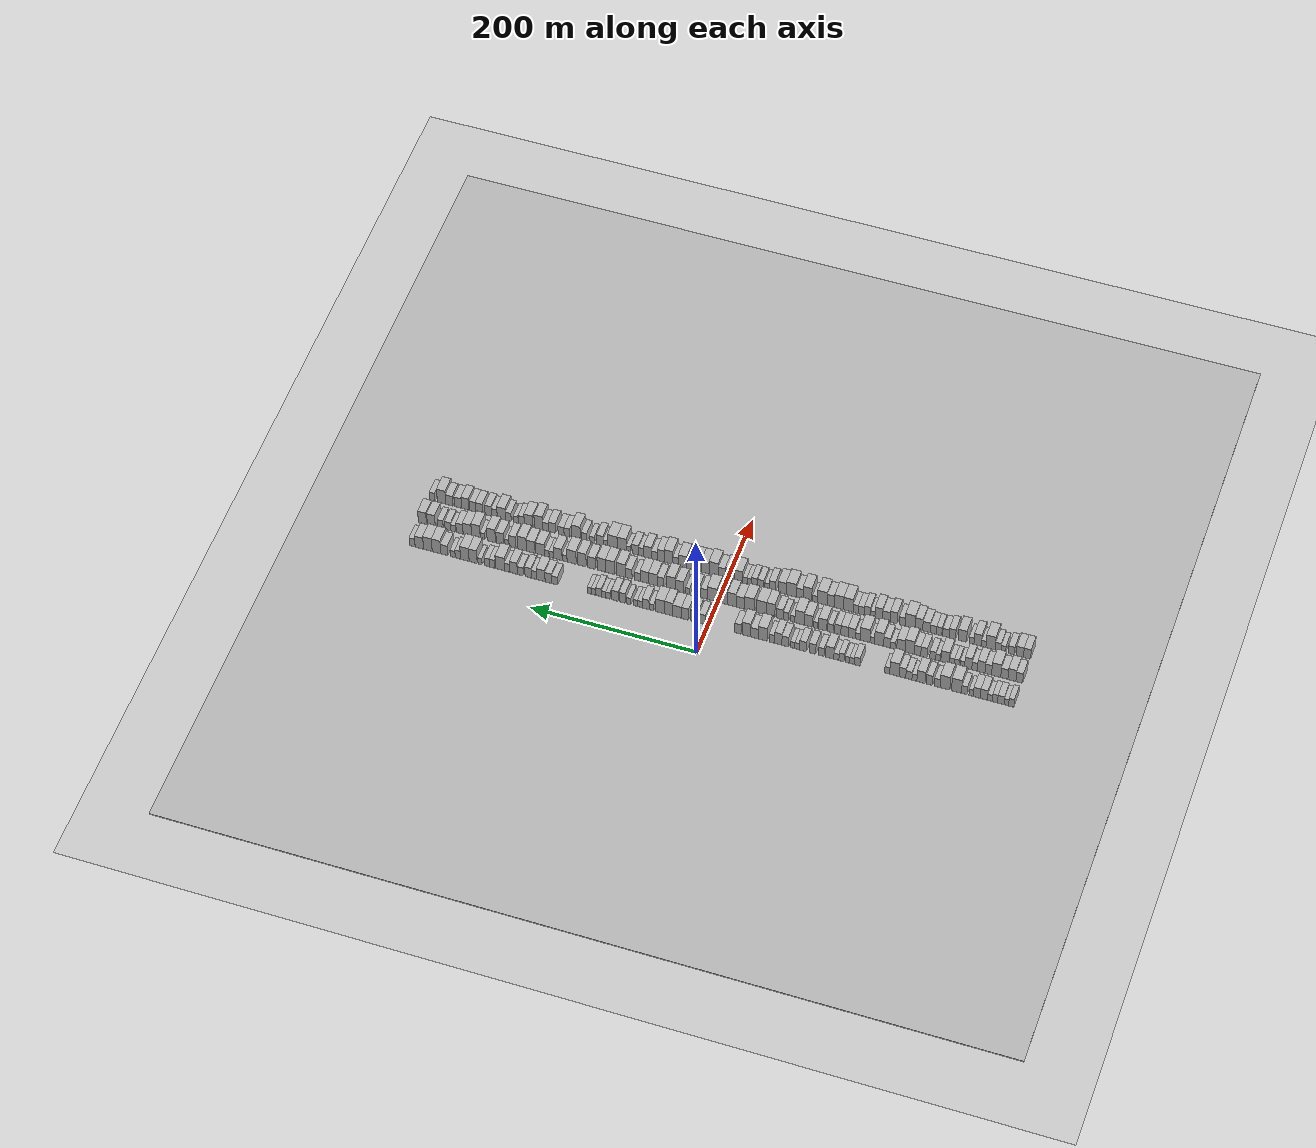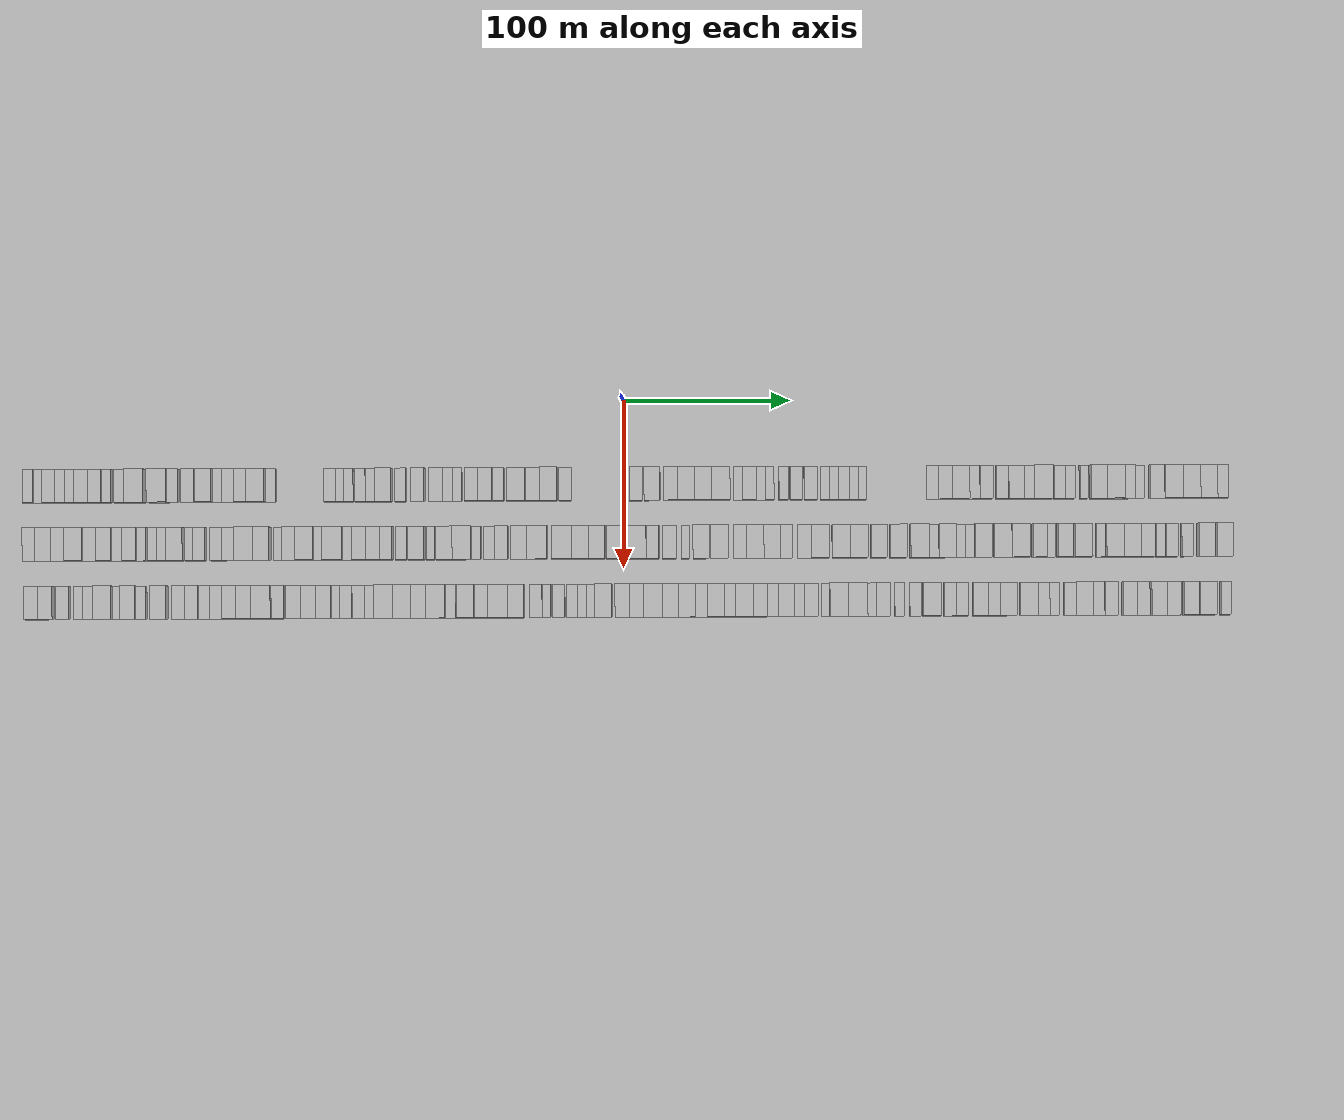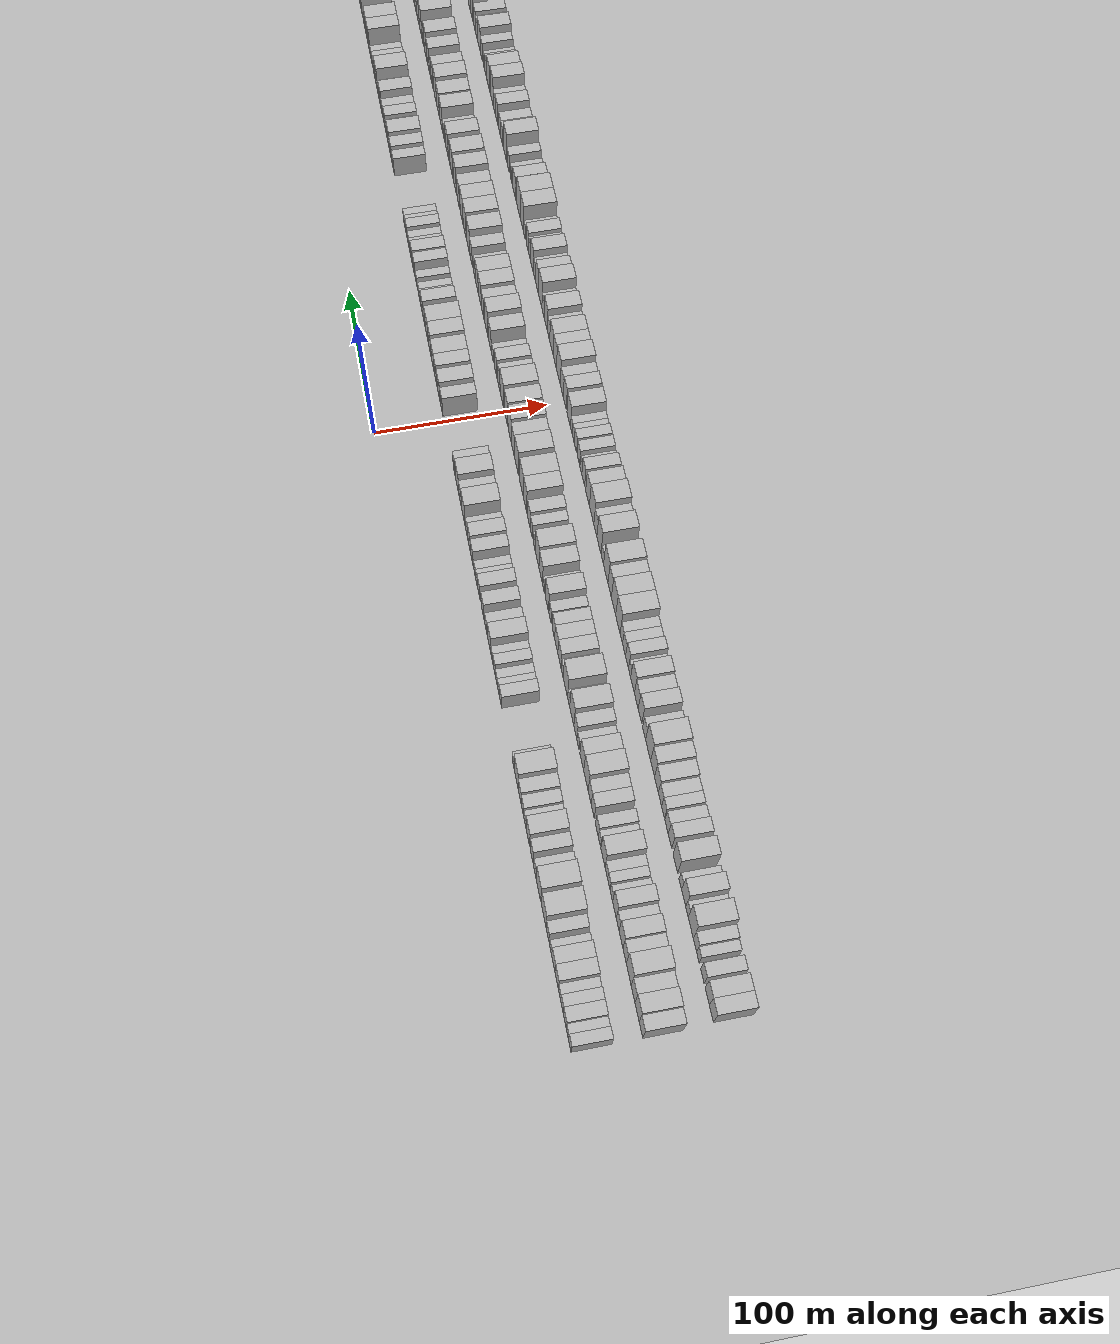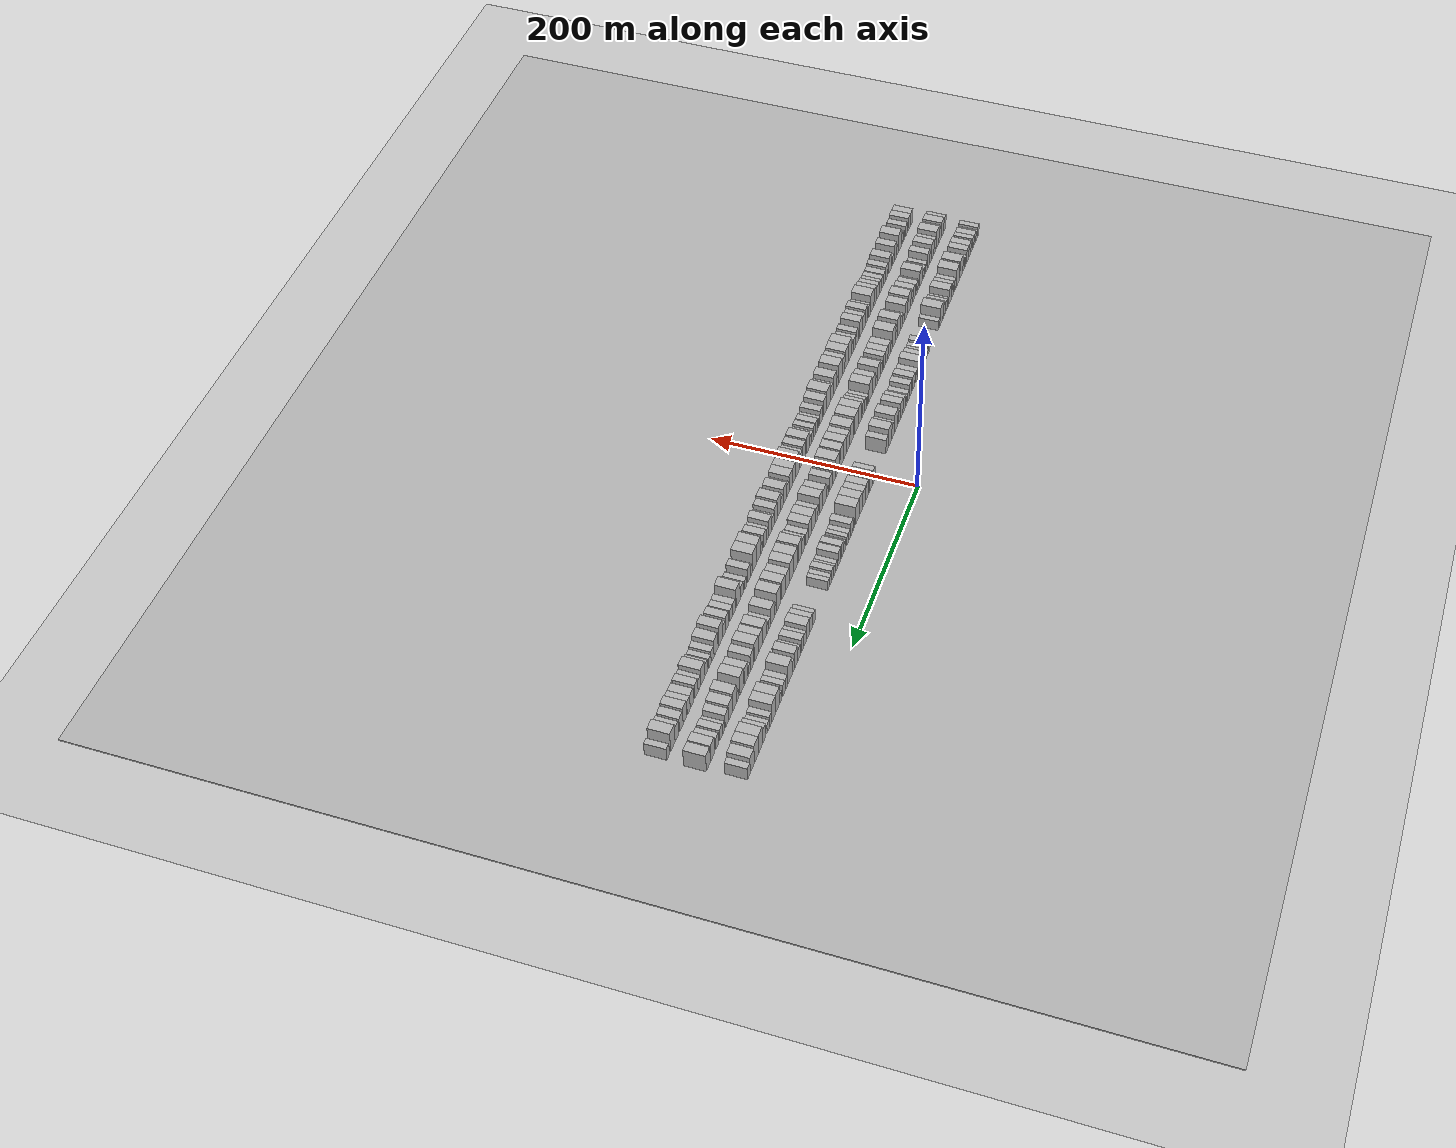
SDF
<?xml version="1.0" encoding="utf-8"?>

<sdf version="1.6">

   <world name="default">

      <gui fullscreen="0">

         <camera name="user_camera">

            <pose>-15 0 4.57585 0 0 0</pose>

            <view_controller>orbit</view_controller>

         </camera>

      </gui>

      <scene>

         <sky>

           <clouds>

             <speed>12</speed>

           </clouds>

         </sky>

         <ambient>0.4 0.4 0.4 1</ambient>

         <background>0.7 0.7 0.7 1</background>

         <shadows>1</shadows>

      </scene>

      <gravity>0 0 -9.8066</gravity>

      <magnetic_field>6e-06 2.3e-05 -4.2e-05</magnetic_field>

      <physics default="0" name="default_physics" type="ode">

         <ode>

            <solver>

               <type>quick</type>

               <iters>10</iters>

               <sor>1.0</sor>

               <use_dynamic_moi_rescaling>0</use_dynamic_moi_rescaling>

            </solver>

            <constraints>

               <cfm>0</cfm>

               <erp>0.2</erp>

               <contact_max_correcting_vel>100</contact_max_correcting_vel>

               <contact_surface_layer>0.001</contact_surface_layer>

            </constraints>

         </ode>

         <max_step_size>0.004</max_step_size>

         <real_time_factor>1</real_time_factor>

         <real_time_update_rate>250</real_time_update_rate>

      </physics>

      <light name="sun" type="directional">

         <cast_shadows>1</cast_shadows>

         <pose>0 0 10 0 0 0</pose>

         <diffuse>0.8 0.8 0.8 1</diffuse>

         <specular>0.2 0.2 0.2 1</specular>

         <attenuation>

            <range>1000</range>

            <constant>0.9</constant>

            <linear>0.01</linear>

            <quadratic>0.001</quadratic>

         </attenuation>

         <direction>-0.5 0.1 -0.9</direction>

      </light>

      <include>

         <name>ground_plane_1</name>

         <uri>model://HANNAS_ground_plane</uri>

         <pose>0 0 0  0 0 0</pose>

      </include>

      <include>

         <name>ground_plane_2</name>

         <uri>model://HANNAS_ground_plane</uri>

         <pose>100 0 0  0 0 0</pose>

      </include>

      <model name="building_1">

         <static>1</static>

         <pose frame="">50.0000 -356.9338 0 0.000000 0.000000 0.000000</pose>

         <link name="link">

            <pose frame="">0 0 7.50 0 0 0</pose>

            <collision name="collision">

               <geometry>

                  <box>

                     <size>20.0000 6.1324 15.0000</size>

                  </box>

               </geometry>

               <max_contacts>10</max_contacts>

               <surface>

                  <contact>

                     <ode/>

                  </contact>

                  <bounce/>

                  <friction>

                     <torsional>

                        <ode/>

                     </torsional>

                     <ode/>

                  </friction>

               </surface>

            </collision>

            <visual name="visual">

               <cast_shadows>0</cast_shadows>

               <geometry>

                  <box>

                     <size>20.0000 6.1324 15.0000</size>

                  </box>

               </geometry>

               <material>

                  <script>

                     <uri>model://HANNAS_wall/materials/scripts</uri>

                     <uri>model://HANNAS_wall/materials/textures</uri>

                     <name>vrc/HANNAS_wall</name>

                  </script>

               </material>

            </visual>

            <self_collide>0</self_collide>

            <enable_wind>0</enable_wind>

            <kinematic>0</kinematic>

         </link>

      </model>

      <model name="building_2">

         <static>1</static>

         <pose frame="">50.0000 -351.1675 0 0.000000 0.000000 0.000000</pose>

         <link name="link">

            <pose frame="">0 0 6.00 0 0 0</pose>

            <collision name="collision">

               <geometry>

                  <box>

                     <size>20.0000 5.4001 12.0000</size>

                  </box>

               </geometry>

               <max_contacts>10</max_contacts>

               <surface>

                  <contact>

                     <ode/>

                  </contact>

                  <bounce/>

                  <friction>

                     <torsional>

                        <ode/>

                     </torsional>

                     <ode/>

                  </friction>

               </surface>

            </collision>

            <visual name="visual">

               <cast_shadows>0</cast_shadows>

               <geometry>

                  <box>

                     <size>20.0000 5.4001 12.0000</size>

                  </box>

               </geometry>

               <material>

                  <script>

                     <uri>model://HANNAS_wall/materials/scripts</uri>

                     <uri>model://HANNAS_wall/materials/textures</uri>

                     <name>vrc/HANNAS_wall</name>

                  </script>

               </material>

            </visual>

            <self_collide>0</self_collide>

            <enable_wind>0</enable_wind>

            <kinematic>0</kinematic>

         </link>

      </model>

      <model name="building_3">

         <static>1</static>

         <pose frame="">50.0000 -344.7227 0 0.000000 0.000000 0.000000</pose>

         <link name="link">

            <pose frame="">0 0 7.50 0 0 0</pose>

            <collision name="collision">

               <geometry>

                  <box>

                     <size>20.0000 7.4894 15.0000</size>

                  </box>

               </geometry>

               <max_contacts>10</max_contacts>

               <surface>

                  <contact>

                     <ode/>

                  </contact>

                  <bounce/>

                  <friction>

                     <torsional>

                        <ode/>

                     </torsional>

                     <ode/>

                  </friction>

               </surface>

            </collision>

            <visual name="visual">

               <cast_shadows>0</cast_shadows>

               <geometry>

                  <box>

                     <size>20.0000 7.4894 15.0000</size>

                  </box>

               </geometry>

               <material>

                  <script>

                     <uri>model://HANNAS_wall/materials/scripts</uri>

                     <uri>model://HANNAS_wall/materials/textures</uri>

                     <name>vrc/HANNAS_wall</name>

                  </script>

               </material>

            </visual>

            <self_collide>0</self_collide>

            <enable_wind>0</enable_wind>

            <kinematic>0</kinematic>

         </link>

      </model>

      <model name="building_4">

         <static>1</static>

         <pose frame="">50.0000 -337.9662 0 0.000000 0.000000 0.000000</pose>

         <link name="link">

            <pose frame="">0 0 7.50 0 0 0</pose>

            <collision name="collision">

               <geometry>

                  <box>

                     <size>20.0000 6.0236 15.0000</size>

                  </box>

               </geometry>

               <max_contacts>10</max_contacts>

               <surface>

                  <contact>

                     <ode/>

                  </contact>

                  <bounce/>

                  <friction>

                     <torsional>

                        <ode/>

                     </torsional>

                     <ode/>

                  </friction>

               </surface>

            </collision>

            <visual name="visual">

               <cast_shadows>0</cast_shadows>

               <geometry>

                  <box>

                     <size>20.0000 6.0236 15.0000</size>

                  </box>

               </geometry>

               <material>

                  <script>

                     <uri>model://HANNAS_wall/materials/scripts</uri>

                     <uri>model://HANNAS_wall/materials/textures</uri>

                     <name>vrc/HANNAS_wall</name>

                  </script>

               </material>

            </visual>

            <self_collide>0</self_collide>

            <enable_wind>0</enable_wind>

            <kinematic>0</kinematic>

         </link>

      </model>

      <model name="building_5">

         <static>1</static>

         <pose frame="">50.0000 -332.0919 0 0.000000 0.000000 0.000000</pose>

         <link name="link">

            <pose frame="">0 0 6.00 0 0 0</pose>

            <collision name="collision">

               <geometry>

                  <box>

                     <size>20.0000 5.7251 12.0000</size>

                  </box>

               </geometry>

               <max_contacts>10</max_contacts>

               <surface>

                  <contact>

                     <ode/>

                  </contact>

                  <bounce/>

                  <friction>

                     <torsional>

                        <ode/>

                     </torsional>

                     <ode/>

                  </friction>

               </surface>

            </collision>

            <visual name="visual">

               <cast_shadows>0</cast_shadows>

               <geometry>

                  <box>

                     <size>20.0000 5.7251 12.0000</size>

                  </box>

               </geometry>

               <material>

                  <script>

                     <uri>model://HANNAS_wall/materials/scripts</uri>

                     <uri>model://HANNAS_wall/materials/textures</uri>

                     <name>vrc/HANNAS_wall</name>

                  </script>

               </material>

            </visual>

            <self_collide>0</self_collide>

            <enable_wind>0</enable_wind>

            <kinematic>0</kinematic>

         </link>

      </model>

      <model name="building_6">

         <static>1</static>

         <pose frame="">50.0000 -325.1106 0 0.000000 0.000000 0.000000</pose>

         <link name="link">

            <pose frame="">0 0 9.00 0 0 0</pose>

            <collision name="collision">

               <geometry>

                  <box>

                     <size>20.0000 8.2375 18.0000</size>

                  </box>

               </geometry>

               <max_contacts>10</max_contacts>

               <surface>

                  <contact>

                     <ode/>

                  </contact>

                  <bounce/>

                  <friction>

                     <torsional>

                        <ode/>

                     </torsional>

                     <ode/>

                  </friction>

               </surface>

            </collision>

            <visual name="visual">

               <cast_shadows>0</cast_shadows>

               <geometry>

                  <box>

                     <size>20.0000 8.2375 18.0000</size>

                  </box>

               </geometry>

               <material>

                  <script>

                     <uri>model://HANNAS_wall/materials/scripts</uri>

                     <uri>model://HANNAS_wall/materials/textures</uri>

                     <name>vrc/HANNAS_wall</name>

                  </script>

               </material>

            </visual>

            <self_collide>0</self_collide>

            <enable_wind>0</enable_wind>

            <kinematic>0</kinematic>

         </link>

      </model>

      <model name="building_7">

         <static>1</static>

         <pose frame="">50.0000 -316.9028 0 0.000000 0.000000 0.000000</pose>

         <link name="link">

            <pose frame="">0 0 9.00 0 0 0</pose>

            <collision name="collision">

               <geometry>

                  <box>

                     <size>20.0000 8.1780 18.0000</size>

                  </box>

               </geometry>

               <max_contacts>10</max_contacts>

               <surface>

                  <contact>

                     <ode/>

                  </contact>

                  <bounce/>

                  <friction>

                     <torsional>

                        <ode/>

                     </torsional>

                     <ode/>

                  </friction>

               </surface>

            </collision>

            <visual name="visual">

               <cast_shadows>0</cast_shadows>

               <geometry>

                  <box>

                     <size>20.0000 8.1780 18.0000</size>

                  </box>

               </geometry>

               <material>

                  <script>

                     <uri>model://HANNAS_wall/materials/scripts</uri>

                     <uri>model://HANNAS_wall/materials/textures</uri>

                     <name>vrc/HANNAS_wall</name>

                  </script>

               </material>

            </visual>

            <self_collide>0</self_collide>

            <enable_wind>0</enable_wind>

            <kinematic>0</kinematic>

         </link>

      </model>

      <model name="building_8">

         <static>1</static>

         <pose frame="">50.0000 -310.1888 0 0.000000 0.000000 0.000000</pose>

         <link name="link">

            <pose frame="">0 0 6.00 0 0 0</pose>

            <collision name="collision">

               <geometry>

                  <box>

                     <size>20.0000 5.2501 12.0000</size>

                  </box>

               </geometry>

               <max_contacts>10</max_contacts>

               <surface>

                  <contact>

                     <ode/>

                  </contact>

                  <bounce/>

                  <friction>

                     <torsional>

                        <ode/>

                     </torsional>

                     <ode/>

                  </friction>

               </surface>

            </collision>

            <visual name="visual">

               <cast_shadows>0</cast_shadows>

               <geometry>

                  <box>

                     <size>20.0000 5.2501 12.0000</size>

                  </box>

               </geometry>

               <material>

                  <script>

                     <uri>model://HANNAS_wall/materials/scripts</uri>

                     <uri>model://HANNAS_wall/materials/textures</uri>

                     <name>vrc/HANNAS_wall</name>

                  </script>

               </material>

            </visual>

            <self_collide>0</self_collide>

            <enable_wind>0</enable_wind>

            <kinematic>0</kinematic>

         </link>

      </model>

      <model name="building_9">

         <static>1</static>

         <pose frame="">50.0000 -302.2213 0 0.000000 0.000000 0.000000</pose>

         <link name="link">

            <pose frame="">0 0 7.50 0 0 0</pose>

            <collision name="collision">

               <geometry>

                  <box>

                     <size>20.0000 6.6848 15.0000</size>

                  </box>

               </geometry>

               <max_contacts>10</max_contacts>

               <surface>

                  <contact>

                     <ode/>

                  </contact>

                  <bounce/>

                  <friction>

                     <torsional>

                        <ode/>

                     </torsional>

                     <ode/>

                  </friction>

               </surface>

            </collision>

            <visual name="visual">

               <cast_shadows>0</cast_shadows>

               <geometry>

                  <box>

                     <size>20.0000 6.6848 15.0000</size>

                  </box>

               </geometry>

               <material>

                  <script>

                     <uri>model://HANNAS_wall/materials/scripts</uri>

                     <uri>model://HANNAS_wall/materials/textures</uri>

                     <name>vrc/HANNAS_wall</name>

                  </script>

               </material>

            </visual>

            <self_collide>0</self_collide>

            <enable_wind>0</enable_wind>

            <kinematic>0</kinematic>

         </link>

      </model>

      <model name="building_10">

         <static>1</static>

         <pose frame="">50.0000 -293.0552 0 0.000000 0.000000 0.000000</pose>

         <link name="link">

            <pose frame="">0 0 12.00 0 0 0</pose>

            <collision name="collision">

               <geometry>

                  <box>

                     <size>20.0000 11.6474 24.0000</size>

                  </box>

               </geometry>

               <max_contacts>10</max_contacts>

               <surface>

                  <contact>

                     <ode/>

                  </contact>

                  <bounce/>

                  <friction>

                     <torsional>

                        <ode/>

                     </torsional>

                     <ode/>

                  </friction>

               </surface>

            </collision>

            <visual name="visual">

               <cast_shadows>0</cast_shadows>

               <geometry>

                  <box>

                     <size>20.0000 11.6474 24.0000</size>

                  </box>

               </geometry>

               <material>

                  <script>

                     <uri>model://HANNAS_wall/materials/scripts</uri>

                     <uri>model://HANNAS_wall/materials/textures</uri>

                     <name>vrc/HANNAS_wall</name>

                  </script>

               </material>

            </visual>

            <self_collide>0</self_collide>

            <enable_wind>0</enable_wind>

            <kinematic>0</kinematic>

         </link>

      </model>

      <model name="building_11">

         <static>1</static>

         <pose frame="">50.0000 -279.4798 0 0.000000 0.000000 0.000000</pose>

         <link name="link">

            <pose frame="">0 0 12.00 0 0 0</pose>

            <collision name="collision">

               <geometry>

                  <box>

                     <size>20.0000 11.5034 24.0000</size>

                  </box>

               </geometry>

               <max_contacts>10</max_contacts>

               <surface>

                  <contact>

                     <ode/>

                  </contact>

                  <bounce/>

                  <friction>

                     <torsional>

                        <ode/>

                     </torsional>

                     <ode/>

                  </friction>

               </surface>

            </collision>

            <visual name="visual">

               <cast_shadows>0</cast_shadows>

               <geometry>

                  <box>

                     <size>20.0000 11.5034 24.0000</size>

                  </box>

               </geometry>

               <material>

                  <script>

                     <uri>model://HANNAS_wall/materials/scripts</uri>

                     <uri>model://HANNAS_wall/materials/textures</uri>

                     <name>vrc/HANNAS_wall</name>

                  </script>

               </material>

            </visual>

            <self_collide>0</self_collide>

            <enable_wind>0</enable_wind>

            <kinematic>0</kinematic>

         </link>

      </model>

      <model name="building_12">

         <static>1</static>

         <pose frame="">50.0000 -270.3471 0 0.000000 0.000000 0.000000</pose>

         <link name="link">

            <pose frame="">0 0 7.50 0 0 0</pose>

            <collision name="collision">

               <geometry>

                  <box>

                     <size>20.0000 6.7619 15.0000</size>

                  </box>

               </geometry>

               <max_contacts>10</max_contacts>

               <surface>

                  <contact>

                     <ode/>

                  </contact>

                  <bounce/>

                  <friction>

                     <torsional>

                        <ode/>

                     </torsional>

                     <ode/>

                  </friction>

               </surface>

            </collision>

            <visual name="visual">

               <cast_shadows>0</cast_shadows>

               <geometry>

                  <box>

                     <size>20.0000 6.7619 15.0000</size>

                  </box>

               </geometry>

               <material>

                  <script>

                     <uri>model://HANNAS_wall/materials/scripts</uri>

                     <uri>model://HANNAS_wall/materials/textures</uri>

                     <name>vrc/HANNAS_wall</name>

                  </script>

               </material>

            </visual>

            <self_collide>0</self_collide>

            <enable_wind>0</enable_wind>

            <kinematic>0</kinematic>

         </link>

      </model>

      <model name="building_13">

         <static>1</static>

         <pose frame="">50.0000 -261.2741 0 0.000000 0.000000 0.000000</pose>

         <link name="link">

            <pose frame="">0 0 9.00 0 0 0</pose>

            <collision name="collision">

               <geometry>

                  <box>

                     <size>20.0000 7.3841 18.0000</size>

                  </box>

               </geometry>

               <max_contacts>10</max_contacts>

               <surface>

                  <contact>

                     <ode/>

                  </contact>

                  <bounce/>

                  <friction>

                     <torsional>

                        <ode/>

                     </torsional>

                     <ode/>

                  </friction>

               </surface>

            </collision>

            <visual name="visual">

               <cast_shadows>0</cast_shadows>

               <geometry>

                  <box>

                     <size>20.0000 7.3841 18.0000</size>

                  </box>

               </geometry>

               <material>

                  <script>

                     <uri>model://HANNAS_wall/materials/scripts</uri>

                     <uri>model://HANNAS_wall/materials/textures</uri>

                     <name>vrc/HANNAS_wall</name>

                  </script>

               </material>

            </visual>

            <self_collide>0</self_collide>

            <enable_wind>0</enable_wind>

            <kinematic>0</kinematic>

         </link>

      </model>

      <model name="building_14">

         <static>1</static>

         <pose frame="">50.0000 -251.6240 0 0.000000 0.000000 0.000000</pose>

         <link name="link">

            <pose frame="">0 0 10.50 0 0 0</pose>

            <collision name="collision">

               <geometry>

                  <box>

                     <size>20.0000 9.9161 21.0000</size>

                  </box>

               </geometry>

               <max_contacts>10</max_contacts>

               <surface>

                  <contact>

                     <ode/>

                  </contact>

                  <bounce/>

                  <friction>

                     <torsional>

                        <ode/>

                     </torsional>

                     <ode/>

                  </friction>

               </surface>

            </collision>

            <visual name="visual">

               <cast_shadows>0</cast_shadows>

               <geometry>

                  <box>

                     <size>20.0000 9.9161 21.0000</size>

                  </box>

               </geometry>

               <material>

                  <script>

                     <uri>model://HANNAS_wall/materials/scripts</uri>

                     <uri>model://HANNAS_wall/materials/textures</uri>

                     <name>vrc/HANNAS_wall</name>

                  </script>

               </material>

            </visual>

            <self_collide>0</self_collide>

            <enable_wind>0</enable_wind>

            <kinematic>0</kinematic>

         </link>

      </model>

      <model name="building_15">

         <static>1</static>

         <pose frame="">50.0000 -243.7519 0 0.000000 0.000000 0.000000</pose>

         <link name="link">

            <pose frame="">0 0 6.00 0 0 0</pose>

            <collision name="collision">

               <geometry>

                  <box>

                     <size>20.0000 5.8281 12.0000</size>

                  </box>

               </geometry>

               <max_contacts>10</max_contacts>

               <surface>

                  <contact>

                     <ode/>

                  </contact>

                  <bounce/>

                  <friction>

                     <torsional>

                        <ode/>

                     </torsional>

                     <ode/>

                  </friction>

               </surface>

            </collision>

            <visual name="visual">

               <cast_shadows>0</cast_shadows>

               <geometry>

                  <box>

                     <size>20.0000 5.8281 12.0000</size>

                  </box>

               </geometry>

               <material>

                  <script>

                     <uri>model://HANNAS_wall/materials/scripts</uri>

                     <uri>model://HANNAS_wall/materials/textures</uri>

                     <name>vrc/HANNAS_wall</name>

                  </script>

               </material>

            </visual>

            <self_collide>0</self_collide>

            <enable_wind>0</enable_wind>

            <kinematic>0</kinematic>

         </link>

      </model>

      <model name="building_16">

         <static>1</static>

         <pose frame="">50.0000 -237.2432 0 0.000000 0.000000 0.000000</pose>

         <link name="link">

            <pose frame="">0 0 7.50 0 0 0</pose>

            <collision name="collision">

               <geometry>

                  <box>

                     <size>20.0000 7.1892 15.0000</size>

                  </box>

               </geometry>

               <max_contacts>10</max_contacts>

               <surface>

                  <contact>

                     <ode/>

                  </contact>

                  <bounce/>

                  <friction>

                     <torsional>

                        <ode/>

                     </torsional>

                     <ode/>

                  </friction>

               </surface>

            </collision>

            <visual name="visual">

               <cast_shadows>0</cast_shadows>

               <geometry>

                  <box>

                     <size>20.0000 7.1892 15.0000</size>

                  </box>

               </geometry>

               <material>

                  <script>

                     <uri>model://HANNAS_wall/materials/scripts</uri>

                     <uri>model://HANNAS_wall/materials/textures</uri>

                     <name>vrc/HANNAS_wall</name>

                  </script>

               </material>

            </visual>

            <self_collide>0</self_collide>

            <enable_wind>0</enable_wind>

            <kinematic>0</kinematic>

         </link>

      </model>

      <model name="building_17">

         <static>1</static>

         <pose frame="">50.0000 -229.8094 0 0.000000 0.000000 0.000000</pose>

         <link name="link">

            <pose frame="">0 0 9.00 0 0 0</pose>

            <collision name="collision">

               <geometry>

                  <box>

                     <size>20.0000 7.6785 18.0000</size>

                  </box>

               </geometry>

               <max_contacts>10</max_contacts>

               <surface>

                  <contact>

                     <ode/>

                  </contact>

                  <bounce/>

                  <friction>

                     <torsional>

                        <ode/>

                     </torsional>

                     <ode/>

                  </friction>

               </surface>

            </collision>

            <visual name="visual">

               <cast_shadows>0</cast_shadows>

               <geometry>

                  <box>

                     <size>20.0000 7.6785 18.0000</size>

                  </box>

               </geometry>

               <material>

                  <script>

                     <uri>model://HANNAS_wall/materials/scripts</uri>

                     <uri>model://HANNAS_wall/materials/textures</uri>

                     <name>vrc/HANNAS_wall</name>

                  </script>

               </material>

            </visual>

            <self_collide>0</self_collide>

            <enable_wind>0</enable_wind>

            <kinematic>0</kinematic>

         </link>

      </model>

      <model name="building_18">

         <static>1</static>

         <pose frame="">50.0000 -220.3632 0 0.000000 0.000000 0.000000</pose>

         <link name="link">

            <pose frame="">0 0 12.00 0 0 0</pose>

            <collision name="collision">

               <geometry>

                  <box>

                     <size>20.0000 11.2139 24.0000</size>

                  </box>

               </geometry>

               <max_contacts>10</max_contacts>

               <surface>

                  <contact>

                     <ode/>

                  </contact>

                  <bounce/>

                  <friction>

                     <torsional>

                        <ode/>

                     </torsional>

                     <ode/>

                  </friction>

               </surface>

            </collision>

            <visual name="visual">

               <cast_shadows>0</cast_shadows>

               <geometry>

                  <box>

                     <size>20.0000 11.2139 24.0000</size>

                  </box>

               </geometry>

               <material>

                  <script>

                     <uri>model://HANNAS_wall/materials/scripts</uri>

                     <uri>model://HANNAS_wall/materials/textures</uri>

                     <name>vrc/HANNAS_wall</name>

                  </script>

               </material>

            </visual>

            <self_collide>0</self_collide>

            <enable_wind>0</enable_wind>

            <kinematic>0</kinematic>

         </link>

      </model>

      <model name="building_19">

         <static>1</static>

         <pose frame="">50.0000 -211.8274 0 0.000000 0.000000 0.000000</pose>

         <link name="link">

            <pose frame="">0 0 6.00 0 0 0</pose>

            <collision name="collision">

               <geometry>

                  <box>

                     <size>20.0000 5.8578 12.0000</size>

                  </box>

               </geometry>

               <max_contacts>10</max_contacts>

               <surface>

                  <contact>

                     <ode/>

                  </contact>

                  <bounce/>

                  <friction>

                     <torsional>

                        <ode/>

                     </torsional>

                     <ode/>

                  </friction>

               </surface>

            </collision>

            <visual name="visual">

               <cast_shadows>0</cast_shadows>

               <geometry>

                  <box>

                     <size>20.0000 5.8578 12.0000</size>

                  </box>

               </geometry>

               <material>

                  <script>

                     <uri>model://HANNAS_wall/materials/scripts</uri>

                     <uri>model://HANNAS_wall/materials/textures</uri>

                     <name>vrc/HANNAS_wall</name>

                  </script>

               </material>

            </visual>

            <self_collide>0</self_collide>

            <enable_wind>0</enable_wind>

            <kinematic>0</kinematic>

         </link>

      </model>

      <model name="building_20">

         <static>1</static>

         <pose frame="">50.0000 -176.2270 0 0.000000 0.000000 0.000000</pose>

         <link name="link">

            <pose frame="">0 0 7.50 0 0 0</pose>

            <collision name="collision">

               <geometry>

                  <box>

                     <size>20.0000 7.1143 15.0000</size>

                  </box>

               </geometry>

               <max_contacts>10</max_contacts>

               <surface>

                  <contact>

                     <ode/>

                  </contact>

                  <bounce/>

                  <friction>

                     <torsional>

                        <ode/>

                     </torsional>

                     <ode/>

                  </friction>

               </surface>

            </collision>

            <visual name="visual">

               <cast_shadows>0</cast_shadows>

               <geometry>

                  <box>

                     <size>20.0000 7.1143 15.0000</size>

                  </box>

               </geometry>

               <material>

                  <script>

                     <uri>model://HANNAS_wall/materials/scripts</uri>

                     <uri>model://HANNAS_wall/materials/textures</uri>

                     <name>vrc/HANNAS_wall</name>

                  </script>

               </material>

            </visual>

            <self_collide>0</self_collide>

            <enable_wind>0</enable_wind>

            <kinematic>0</kinematic>

         </link>

      </model>

      <model name="building_21">

         <static>1</static>

         <pose frame="">50.0000 -170.1539 0 0.000000 0.000000 0.000000</pose>

         <link name="link">

            <pose frame="">0 0 6.00 0 0 0</pose>

            <collision name="collision">

               <geometry>

                  <box>

                     <size>20.0000 5.0317 12.0000</size>

                  </box>

               </geometry>

               <max_contacts>10</max_contacts>

               <surface>

                  <contact>

                     <ode/>

                  </contact>

                  <bounce/>

                  <friction>

                     <torsional>

                        <ode/>

                     </torsional>

                     <ode/>

                  </friction>

               </surface>

            </collision>

            <visual name="visual">

               <cast_shadows>0</cast_shadows>

               <geometry>

                  <box>

                     <size>20.0000 5.0317 12.0000</size>

                  </box>

               </geometry>

               <material>

                  <script>

                     <uri>model://HANNAS_wall/materials/scripts</uri>

                     <uri>model://HANNAS_wall/materials/textures</uri>

                     <name>vrc/HANNAS_wall</name>

                  </script>

               </material>

            </visual>

            <self_collide>0</self_collide>

            <enable_wind>0</enable_wind>

            <kinematic>0</kinematic>

         </link>

      </model>

      <model name="building_22">

         <static>1</static>

         <pose frame="">50.0000 -164.9242 0 0.000000 0.000000 0.000000</pose>

         <link name="link">

            <pose frame="">0 0 6.00 0 0 0</pose>

            <collision name="collision">

               <geometry>

                  <box>

                     <size>20.0000 5.4278 12.0000</size>

                  </box>

               </geometry>

               <max_contacts>10</max_contacts>

               <surface>

                  <contact>

                     <ode/>

                  </contact>

                  <bounce/>

                  <friction>

                     <torsional>

                        <ode/>

                     </torsional>

                     <ode/>

                  </friction>

               </surface>

            </collision>

            <visual name="visual">

               <cast_shadows>0</cast_shadows>

               <geometry>

                  <box>

                     <size>20.0000 5.4278 12.0000</size>

                  </box>

               </geometry>

               <material>

                  <script>

                     <uri>model://HANNAS_wall/materials/scripts</uri>

                     <uri>model://HANNAS_wall/materials/textures</uri>

                     <name>vrc/HANNAS_wall</name>

                  </script>

               </material>

            </visual>

            <self_collide>0</self_collide>

            <enable_wind>0</enable_wind>

            <kinematic>0</kinematic>

         </link>

      </model>

      <model name="building_23">

         <static>1</static>

         <pose frame="">50.0000 -158.0271 0 0.000000 0.000000 0.000000</pose>

         <link name="link">

            <pose frame="">0 0 7.50 0 0 0</pose>

            <collision name="collision">

               <geometry>

                  <box>

                     <size>20.0000 6.3664 15.0000</size>

                  </box>

               </geometry>

               <max_contacts>10</max_contacts>

               <surface>

                  <contact>

                     <ode/>

                  </contact>

                  <bounce/>

                  <friction>

                     <torsional>

                        <ode/>

                     </torsional>

                     <ode/>

                  </friction>

               </surface>

            </collision>

            <visual name="visual">

               <cast_shadows>0</cast_shadows>

               <geometry>

                  <box>

                     <size>20.0000 6.3664 15.0000</size>

                  </box>

               </geometry>

               <material>

                  <script>

                     <uri>model://HANNAS_wall/materials/scripts</uri>

                     <uri>model://HANNAS_wall/materials/textures</uri>

                     <name>vrc/HANNAS_wall</name>

                  </script>

               </material>

            </visual>

            <self_collide>0</self_collide>

            <enable_wind>0</enable_wind>

            <kinematic>0</kinematic>

         </link>

      </model>

      <model name="building_24">

         <static>1</static>

         <pose frame="">50.0000 -151.8576 0 0.000000 0.000000 0.000000</pose>

         <link name="link">

            <pose frame="">0 0 6.00 0 0 0</pose>

            <collision name="collision">

               <geometry>

                  <box>

                     <size>20.0000 5.9726 12.0000</size>

                  </box>

               </geometry>

               <max_contacts>10</max_contacts>

               <surface>

                  <contact>

                     <ode/>

                  </contact>

                  <bounce/>

                  <friction>

                     <torsional>

                        <ode/>

                     </torsional>

                     <ode/>

                  </friction>

               </surface>

            </collision>

            <visual name="visual">

               <cast_shadows>0</cast_shadows>

               <geometry>

                  <box>

                     <size>20.0000 5.9726 12.0000</size>

                  </box>

               </geometry>

               <material>

                  <script>

                     <uri>model://HANNAS_wall/materials/scripts</uri>

                     <uri>model://HANNAS_wall/materials/textures</uri>

                     <name>vrc/HANNAS_wall</name>

                  </script>

               </material>

            </visual>

            <self_collide>0</self_collide>

            <enable_wind>0</enable_wind>

            <kinematic>0</kinematic>

         </link>

      </model>

      <model name="building_25">

         <static>1</static>

         <pose frame="">50.0000 -144.0656 0 0.000000 0.000000 0.000000</pose>

         <link name="link">

            <pose frame="">0 0 10.50 0 0 0</pose>

            <collision name="collision">

               <geometry>

                  <box>

                     <size>20.0000 9.6114 21.0000</size>

                  </box>

               </geometry>

               <max_contacts>10</max_contacts>

               <surface>

                  <contact>

                     <ode/>

                  </contact>

                  <bounce/>

                  <friction>

                     <torsional>

                        <ode/>

                     </torsional>

                     <ode/>

                  </friction>

               </surface>

            </collision>

            <visual name="visual">

               <cast_shadows>0</cast_shadows>

               <geometry>

                  <box>

                     <size>20.0000 9.6114 21.0000</size>

                  </box>

               </geometry>

               <material>

                  <script>

                     <uri>model://HANNAS_wall/materials/scripts</uri>

                     <uri>model://HANNAS_wall/materials/textures</uri>

                     <name>vrc/HANNAS_wall</name>

                  </script>

               </material>

            </visual>

            <self_collide>0</self_collide>

            <enable_wind>0</enable_wind>

            <kinematic>0</kinematic>

         </link>

      </model>

      <model name="building_26">

         <static>1</static>

         <pose frame="">50.0000 -133.8939 0 0.000000 0.000000 0.000000</pose>

         <link name="link">

            <pose frame="">0 0 7.50 0 0 0</pose>

            <collision name="collision">

               <geometry>

                  <box>

                     <size>20.0000 6.7320 15.0000</size>

                  </box>

               </geometry>

               <max_contacts>10</max_contacts>

               <surface>

                  <contact>

                     <ode/>

                  </contact>

                  <bounce/>

                  <friction>

                     <torsional>

                        <ode/>

                     </torsional>

                     <ode/>

                  </friction>

               </surface>

            </collision>

            <visual name="visual">

               <cast_shadows>0</cast_shadows>

               <geometry>

                  <box>

                     <size>20.0000 6.7320 15.0000</size>

                  </box>

               </geometry>

               <material>

                  <script>

                     <uri>model://HANNAS_wall/materials/scripts</uri>

                     <uri>model://HANNAS_wall/materials/textures</uri>

                     <name>vrc/HANNAS_wall</name>

                  </script>

               </material>

            </visual>

            <self_collide>0</self_collide>

            <enable_wind>0</enable_wind>

            <kinematic>0</kinematic>

         </link>

      </model>

      <model name="building_27">

         <static>1</static>

         <pose frame="">50.0000 -123.4901 0 0.000000 0.000000 0.000000</pose>

         <link name="link">

            <pose frame="">0 0 9.00 0 0 0</pose>

            <collision name="collision">

               <geometry>

                  <box>

                     <size>20.0000 8.0756 18.0000</size>

                  </box>

               </geometry>

               <max_contacts>10</max_contacts>

               <surface>

                  <contact>

                     <ode/>

                  </contact>

                  <bounce/>

                  <friction>

                     <torsional>

                        <ode/>

                     </torsional>

                     <ode/>

                  </friction>

               </surface>

            </collision>

            <visual name="visual">

               <cast_shadows>0</cast_shadows>

               <geometry>

                  <box>

                     <size>20.0000 8.0756 18.0000</size>

                  </box>

               </geometry>

               <material>

                  <script>

                     <uri>model://HANNAS_wall/materials/scripts</uri>

                     <uri>model://HANNAS_wall/materials/textures</uri>

                     <name>vrc/HANNAS_wall</name>

                  </script>

               </material>

            </visual>

            <self_collide>0</self_collide>

            <enable_wind>0</enable_wind>

            <kinematic>0</kinematic>

         </link>

      </model>

      <model name="building_28">

         <static>1</static>

         <pose frame="">50.0000 -112.4935 0 0.000000 0.000000 0.000000</pose>

         <link name="link">

            <pose frame="">0 0 9.00 0 0 0</pose>

            <collision name="collision">

               <geometry>

                  <box>

                     <size>20.0000 7.9175 18.0000</size>

                  </box>

               </geometry>

               <max_contacts>10</max_contacts>

               <surface>

                  <contact>

                     <ode/>

                  </contact>

                  <bounce/>

                  <friction>

                     <torsional>

                        <ode/>

                     </torsional>

                     <ode/>

                  </friction>

               </surface>

            </collision>

            <visual name="visual">

               <cast_shadows>0</cast_shadows>

               <geometry>

                  <box>

                     <size>20.0000 7.9175 18.0000</size>

                  </box>

               </geometry>

               <material>

                  <script>

                     <uri>model://HANNAS_wall/materials/scripts</uri>

                     <uri>model://HANNAS_wall/materials/textures</uri>

                     <name>vrc/HANNAS_wall</name>

                  </script>

               </material>

            </visual>

            <self_collide>0</self_collide>

            <enable_wind>0</enable_wind>

            <kinematic>0</kinematic>

         </link>

      </model>

      <model name="building_29">

         <static>1</static>

         <pose frame="">50.0000 -105.5988 0 0.000000 0.000000 0.000000</pose>

         <link name="link">

            <pose frame="">0 0 6.00 0 0 0</pose>

            <collision name="collision">

               <geometry>

                  <box>

                     <size>20.0000 5.8719 12.0000</size>

                  </box>

               </geometry>

               <max_contacts>10</max_contacts>

               <surface>

                  <contact>

                     <ode/>

                  </contact>

                  <bounce/>

                  <friction>

                     <torsional>

                        <ode/>

                     </torsional>

                     <ode/>

                  </friction>

               </surface>

            </collision>

            <visual name="visual">

               <cast_shadows>0</cast_shadows>

               <geometry>

                  <box>

                     <size>20.0000 5.8719 12.0000</size>

                  </box>

               </geometry>

               <material>

                  <script>

                     <uri>model://HANNAS_wall/materials/scripts</uri>

                     <uri>model://HANNAS_wall/materials/textures</uri>

                     <name>vrc/HANNAS_wall</name>

                  </script>

               </material>

            </visual>

            <self_collide>0</self_collide>

            <enable_wind>0</enable_wind>

            <kinematic>0</kinematic>

         </link>

      </model>

      <model name="building_30">

         <static>1</static>

         <pose frame="">50.0000 -99.9868 0 0.000000 0.000000 0.000000</pose>

         <link name="link">

            <pose frame="">0 0 6.00 0 0 0</pose>

            <collision name="collision">

               <geometry>

                  <box>

                     <size>20.0000 5.3522 12.0000</size>

                  </box>

               </geometry>

               <max_contacts>10</max_contacts>

               <surface>

                  <contact>

                     <ode/>

                  </contact>

                  <bounce/>

                  <friction>

                     <torsional>

                        <ode/>

                     </torsional>

                     <ode/>

                  </friction>

               </surface>

            </collision>

            <visual name="visual">

               <cast_shadows>0</cast_shadows>

               <geometry>

                  <box>

                     <size>20.0000 5.3522 12.0000</size>

                  </box>

               </geometry>

               <material>

                  <script>

                     <uri>model://HANNAS_wall/materials/scripts</uri>

                     <uri>model://HANNAS_wall/materials/textures</uri>

                     <name>vrc/HANNAS_wall</name>

                  </script>

               </material>

            </visual>

            <self_collide>0</self_collide>

            <enable_wind>0</enable_wind>

            <kinematic>0</kinematic>

         </link>

      </model>

      <model name="building_31">

         <static>1</static>

         <pose frame="">50.0000 -91.3105 0 0.000000 0.000000 0.000000</pose>

         <link name="link">

            <pose frame="">0 0 9.00 0 0 0</pose>

            <collision name="collision">

               <geometry>

                  <box>

                     <size>20.0000 8.0003 18.0000</size>

                  </box>

               </geometry>

               <max_contacts>10</max_contacts>

               <surface>

                  <contact>

                     <ode/>

                  </contact>

                  <bounce/>

                  <friction>

                     <torsional>

                        <ode/>

                     </torsional>

                     <ode/>

                  </friction>

               </surface>

            </collision>

            <visual name="visual">

               <cast_shadows>0</cast_shadows>

               <geometry>

                  <box>

                     <size>20.0000 8.0003 18.0000</size>

                  </box>

               </geometry>

               <material>

                  <script>

                     <uri>model://HANNAS_wall/materials/scripts</uri>

                     <uri>model://HANNAS_wall/materials/textures</uri>

                     <name>vrc/HANNAS_wall</name>

                  </script>

               </material>

            </visual>

            <self_collide>0</self_collide>

            <enable_wind>0</enable_wind>

            <kinematic>0</kinematic>

         </link>

      </model>

      <model name="building_32">

         <static>1</static>

         <pose frame="">50.0000 -83.0380 0 0.000000 0.000000 0.000000</pose>

         <link name="link">

            <pose frame="">0 0 10.50 0 0 0</pose>

            <collision name="collision">

               <geometry>

                  <box>

                     <size>20.0000 8.5449 21.0000</size>

                  </box>

               </geometry>

               <max_contacts>10</max_contacts>

               <surface>

                  <contact>

                     <ode/>

                  </contact>

                  <bounce/>

                  <friction>

                     <torsional>

                        <ode/>

                     </torsional>

                     <ode/>

                  </friction>

               </surface>

            </collision>

            <visual name="visual">

               <cast_shadows>0</cast_shadows>

               <geometry>

                  <box>

                     <size>20.0000 8.5449 21.0000</size>

                  </box>

               </geometry>

               <material>

                  <script>

                     <uri>model://HANNAS_wall/materials/scripts</uri>

                     <uri>model://HANNAS_wall/materials/textures</uri>

                     <name>vrc/HANNAS_wall</name>

                  </script>

               </material>

            </visual>

            <self_collide>0</self_collide>

            <enable_wind>0</enable_wind>

            <kinematic>0</kinematic>

         </link>

      </model>

      <model name="building_33">

         <static>1</static>

         <pose frame="">50.0000 -75.3986 0 0.000000 0.000000 0.000000</pose>

         <link name="link">

            <pose frame="">0 0 7.50 0 0 0</pose>

            <collision name="collision">

               <geometry>

                  <box>

                     <size>20.0000 6.7339 15.0000</size>

                  </box>

               </geometry>

               <max_contacts>10</max_contacts>

               <surface>

                  <contact>

                     <ode/>

                  </contact>

                  <bounce/>

                  <friction>

                     <torsional>

                        <ode/>

                     </torsional>

                     <ode/>

                  </friction>

               </surface>

            </collision>

            <visual name="visual">

               <cast_shadows>0</cast_shadows>

               <geometry>

                  <box>

                     <size>20.0000 6.7339 15.0000</size>

                  </box>

               </geometry>

               <material>

                  <script>

                     <uri>model://HANNAS_wall/materials/scripts</uri>

                     <uri>model://HANNAS_wall/materials/textures</uri>

                     <name>vrc/HANNAS_wall</name>

                  </script>

               </material>

            </visual>

            <self_collide>0</self_collide>

            <enable_wind>0</enable_wind>

            <kinematic>0</kinematic>

         </link>

      </model>

      <model name="building_34">

         <static>1</static>

         <pose frame="">50.0000 -64.4843 0 0.000000 0.000000 0.000000</pose>

         <link name="link">

            <pose frame="">0 0 12.00 0 0 0</pose>

            <collision name="collision">

               <geometry>

                  <box>

                     <size>20.0000 11.0947 24.0000</size>

                  </box>

               </geometry>

               <max_contacts>10</max_contacts>

               <surface>

                  <contact>

                     <ode/>

                  </contact>

                  <bounce/>

                  <friction>

                     <torsional>

                        <ode/>

                     </torsional>

                     <ode/>

                  </friction>

               </surface>

            </collision>

            <visual name="visual">

               <cast_shadows>0</cast_shadows>

               <geometry>

                  <box>

                     <size>20.0000 11.0947 24.0000</size>

                  </box>

               </geometry>

               <material>

                  <script>

                     <uri>model://HANNAS_wall/materials/scripts</uri>

                     <uri>model://HANNAS_wall/materials/textures</uri>

                     <name>vrc/HANNAS_wall</name>

                  </script>

               </material>

            </visual>

            <self_collide>0</self_collide>

            <enable_wind>0</enable_wind>

            <kinematic>0</kinematic>

         </link>

      </model>

      <model name="building_35">

         <static>1</static>

         <pose frame="">50.0000 -54.6531 0 0.000000 0.000000 0.000000</pose>

         <link name="link">

            <pose frame="">0 0 9.00 0 0 0</pose>

            <collision name="collision">

               <geometry>

                  <box>

                     <size>20.0000 8.5675 18.0000</size>

                  </box>

               </geometry>

               <max_contacts>10</max_contacts>

               <surface>

                  <contact>

                     <ode/>

                  </contact>

                  <bounce/>

                  <friction>

                     <torsional>

                        <ode/>

                     </torsional>

                     <ode/>

                  </friction>

               </surface>

            </collision>

            <visual name="visual">

               <cast_shadows>0</cast_shadows>

               <geometry>

                  <box>

                     <size>20.0000 8.5675 18.0000</size>

                  </box>

               </geometry>

               <material>

                  <script>

                     <uri>model://HANNAS_wall/materials/scripts</uri>

                     <uri>model://HANNAS_wall/materials/textures</uri>

                     <name>vrc/HANNAS_wall</name>

                  </script>

               </material>

            </visual>

            <self_collide>0</self_collide>

            <enable_wind>0</enable_wind>

            <kinematic>0</kinematic>

         </link>

      </model>

      <model name="building_36">

         <static>1</static>

         <pose frame="">50.0000 -45.1233 0 0.000000 0.000000 0.000000</pose>

         <link name="link">

            <pose frame="">0 0 12.00 0 0 0</pose>

            <collision name="collision">

               <geometry>

                  <box>

                     <size>20.0000 10.4921 24.0000</size>

                  </box>

               </geometry>

               <max_contacts>10</max_contacts>

               <surface>

                  <contact>

                     <ode/>

                  </contact>

                  <bounce/>

                  <friction>

                     <torsional>

                        <ode/>

                     </torsional>

                     <ode/>

                  </friction>

               </surface>

            </collision>

            <visual name="visual">

               <cast_shadows>0</cast_shadows>

               <geometry>

                  <box>

                     <size>20.0000 10.4921 24.0000</size>

                  </box>

               </geometry>

               <material>

                  <script>

                     <uri>model://HANNAS_wall/materials/scripts</uri>

                     <uri>model://HANNAS_wall/materials/textures</uri>

                     <name>vrc/HANNAS_wall</name>

                  </script>

               </material>

            </visual>

            <self_collide>0</self_collide>

            <enable_wind>0</enable_wind>

            <kinematic>0</kinematic>

         </link>

      </model>

      <model name="building_37">

         <static>1</static>

         <pose frame="">50.0000 -35.1393 0 0.000000 0.000000 0.000000</pose>

         <link name="link">

            <pose frame="">0 0 9.00 0 0 0</pose>

            <collision name="collision">

               <geometry>

                  <box>

                     <size>20.0000 7.4760 18.0000</size>

                  </box>

               </geometry>

               <max_contacts>10</max_contacts>

               <surface>

                  <contact>

                     <ode/>

                  </contact>

                  <bounce/>

                  <friction>

                     <torsional>

                        <ode/>

                     </torsional>

                     <ode/>

                  </friction>

               </surface>

            </collision>

            <visual name="visual">

               <cast_shadows>0</cast_shadows>

               <geometry>

                  <box>

                     <size>20.0000 7.4760 18.0000</size>

                  </box>

               </geometry>

               <material>

                  <script>

                     <uri>model://HANNAS_wall/materials/scripts</uri>

                     <uri>model://HANNAS_wall/materials/textures</uri>

                     <name>vrc/HANNAS_wall</name>

                  </script>

               </material>

            </visual>

            <self_collide>0</self_collide>

            <enable_wind>0</enable_wind>

            <kinematic>0</kinematic>

         </link>

      </model>

      <model name="building_38">

         <static>1</static>

         <pose frame="">50.0000 7.3286 0 0.000000 0.000000 0.000000</pose>

         <link name="link">

            <pose frame="">0 0 9.00 0 0 0</pose>

            <collision name="collision">

               <geometry>

                  <box>

                     <size>20.0000 7.8199 18.0000</size>

                  </box>

               </geometry>

               <max_contacts>10</max_contacts>

               <surface>

                  <contact>

                     <ode/>

                  </contact>

                  <bounce/>

                  <friction>

                     <torsional>

                        <ode/>

                     </torsional>

                     <ode/>

                  </friction>

               </surface>

            </collision>

            <visual name="visual">

               <cast_shadows>0</cast_shadows>

               <geometry>

                  <box>

                     <size>20.0000 7.8199 18.0000</size>

                  </box>

               </geometry>

               <material>

                  <script>

                     <uri>model://HANNAS_wall/materials/scripts</uri>

                     <uri>model://HANNAS_wall/materials/textures</uri>

                     <name>vrc/HANNAS_wall</name>

                  </script>

               </material>

            </visual>

            <self_collide>0</self_collide>

            <enable_wind>0</enable_wind>

            <kinematic>0</kinematic>

         </link>

      </model>

      <model name="building_39">

         <static>1</static>

         <pose frame="">50.0000 16.9581 0 0.000000 0.000000 0.000000</pose>

         <link name="link">

            <pose frame="">0 0 10.50 0 0 0</pose>

            <collision name="collision">

               <geometry>

                  <box>

                     <size>20.0000 9.4390 21.0000</size>

                  </box>

               </geometry>

               <max_contacts>10</max_contacts>

               <surface>

                  <contact>

                     <ode/>

                  </contact>

                  <bounce/>

                  <friction>

                     <torsional>

                        <ode/>

                     </torsional>

                     <ode/>

                  </friction>

               </surface>

            </collision>

            <visual name="visual">

               <cast_shadows>0</cast_shadows>

               <geometry>

                  <box>

                     <size>20.0000 9.4390 21.0000</size>

                  </box>

               </geometry>

               <material>

                  <script>

                     <uri>model://HANNAS_wall/materials/scripts</uri>

                     <uri>model://HANNAS_wall/materials/textures</uri>

                     <name>vrc/HANNAS_wall</name>

                  </script>

               </material>

            </visual>

            <self_collide>0</self_collide>

            <enable_wind>0</enable_wind>

            <kinematic>0</kinematic>

         </link>

      </model>

      <model name="building_40">

         <static>1</static>

         <pose frame="">50.0000 27.9393 0 0.000000 0.000000 0.000000</pose>

         <link name="link">

            <pose frame="">0 0 10.50 0 0 0</pose>

            <collision name="collision">

               <geometry>

                  <box>

                     <size>20.0000 8.5234 21.0000</size>

                  </box>

               </geometry>

               <max_contacts>10</max_contacts>

               <surface>

                  <contact>

                     <ode/>

                  </contact>

                  <bounce/>

                  <friction>

                     <torsional>

                        <ode/>

                     </torsional>

                     <ode/>

                  </friction>

               </surface>

            </collision>

            <visual name="visual">

               <cast_shadows>0</cast_shadows>

               <geometry>

                  <box>

                     <size>20.0000 8.5234 21.0000</size>

                  </box>

               </geometry>

               <material>

                  <script>

                     <uri>model://HANNAS_wall/materials/scripts</uri>

                     <uri>model://HANNAS_wall/materials/textures</uri>

                     <name>vrc/HANNAS_wall</name>

                  </script>

               </material>

            </visual>

            <self_collide>0</self_collide>

            <enable_wind>0</enable_wind>

            <kinematic>0</kinematic>

         </link>

      </model>

      <model name="building_41">

         <static>1</static>

         <pose frame="">50.0000 37.4314 0 0.000000 0.000000 0.000000</pose>

         <link name="link">

            <pose frame="">0 0 10.50 0 0 0</pose>

            <collision name="collision">

               <geometry>

                  <box>

                     <size>20.0000 10.4609 21.0000</size>

                  </box>

               </geometry>

               <max_contacts>10</max_contacts>

               <surface>

                  <contact>

                     <ode/>

                  </contact>

                  <bounce/>

                  <friction>

                     <torsional>

                        <ode/>

                     </torsional>

                     <ode/>

                  </friction>

               </surface>

            </collision>

            <visual name="visual">

               <cast_shadows>0</cast_shadows>

               <geometry>

                  <box>

                     <size>20.0000 10.4609 21.0000</size>

                  </box>

               </geometry>

               <material>

                  <script>

                     <uri>model://HANNAS_wall/materials/scripts</uri>

                     <uri>model://HANNAS_wall/materials/textures</uri>

                     <name>vrc/HANNAS_wall</name>

                  </script>

               </material>

            </visual>

            <self_collide>0</self_collide>

            <enable_wind>0</enable_wind>

            <kinematic>0</kinematic>

         </link>

      </model>

      <model name="building_42">

         <static>1</static>

         <pose frame="">50.0000 47.5673 0 0.000000 0.000000 0.000000</pose>

         <link name="link">

            <pose frame="">0 0 12.00 0 0 0</pose>

            <collision name="collision">

               <geometry>

                  <box>

                     <size>20.0000 9.8109 24.0000</size>

                  </box>

               </geometry>

               <max_contacts>10</max_contacts>

               <surface>

                  <contact>

                     <ode/>

                  </contact>

                  <bounce/>

                  <friction>

                     <torsional>

                        <ode/>

                     </torsional>

                     <ode/>

                  </friction>

               </surface>

            </collision>

            <visual name="visual">

               <cast_shadows>0</cast_shadows>

               <geometry>

                  <box>

                     <size>20.0000 9.8109 24.0000</size>

                  </box>

               </geometry>

               <material>

                  <script>

                     <uri>model://HANNAS_wall/materials/scripts</uri>

                     <uri>model://HANNAS_wall/materials/textures</uri>

                     <name>vrc/HANNAS_wall</name>

                  </script>

               </material>

            </visual>

            <self_collide>0</self_collide>

            <enable_wind>0</enable_wind>

            <kinematic>0</kinematic>

         </link>

      </model>

      <model name="building_43">

         <static>1</static>

         <pose frame="">50.0000 58.0806 0 0.000000 0.000000 0.000000</pose>

         <link name="link">

            <pose frame="">0 0 12.00 0 0 0</pose>

            <collision name="collision">

               <geometry>

                  <box>

                     <size>20.0000 11.2156 24.0000</size>

                  </box>

               </geometry>

               <max_contacts>10</max_contacts>

               <surface>

                  <contact>

                     <ode/>

                  </contact>

                  <bounce/>

                  <friction>

                     <torsional>

                        <ode/>

                     </torsional>

                     <ode/>

                  </friction>

               </surface>

            </collision>

            <visual name="visual">

               <cast_shadows>0</cast_shadows>

               <geometry>

                  <box>

                     <size>20.0000 11.2156 24.0000</size>

                  </box>

               </geometry>

               <material>

                  <script>

                     <uri>model://HANNAS_wall/materials/scripts</uri>

                     <uri>model://HANNAS_wall/materials/textures</uri>

                     <name>vrc/HANNAS_wall</name>

                  </script>

               </material>

            </visual>

            <self_collide>0</self_collide>

            <enable_wind>0</enable_wind>

            <kinematic>0</kinematic>

         </link>

      </model>

      <model name="building_44">

         <static>1</static>

         <pose frame="">50.0000 68.4880 0 0.000000 0.000000 0.000000</pose>

         <link name="link">

            <pose frame="">0 0 6.00 0 0 0</pose>

            <collision name="collision">

               <geometry>

                  <box>

                     <size>20.0000 5.5991 12.0000</size>

                  </box>

               </geometry>

               <max_contacts>10</max_contacts>

               <surface>

                  <contact>

                     <ode/>

                  </contact>

                  <bounce/>

                  <friction>

                     <torsional>

                        <ode/>

                     </torsional>

                     <ode/>

                  </friction>

               </surface>

            </collision>

            <visual name="visual">

               <cast_shadows>0</cast_shadows>

               <geometry>

                  <box>

                     <size>20.0000 5.5991 12.0000</size>

                  </box>

               </geometry>

               <material>

                  <script>

                     <uri>model://HANNAS_wall/materials/scripts</uri>

                     <uri>model://HANNAS_wall/materials/textures</uri>

                     <name>vrc/HANNAS_wall</name>

                  </script>

               </material>

            </visual>

            <self_collide>0</self_collide>

            <enable_wind>0</enable_wind>

            <kinematic>0</kinematic>

         </link>

      </model>

      <model name="building_45">

         <static>1</static>

         <pose frame="">50.0000 75.3847 0 0.000000 0.000000 0.000000</pose>

         <link name="link">

            <pose frame="">0 0 9.00 0 0 0</pose>

            <collision name="collision">

               <geometry>

                  <box>

                     <size>20.0000 8.1942 18.0000</size>

                  </box>

               </geometry>

               <max_contacts>10</max_contacts>

               <surface>

                  <contact>

                     <ode/>

                  </contact>

                  <bounce/>

                  <friction>

                     <torsional>

                        <ode/>

                     </torsional>

                     <ode/>

                  </friction>

               </surface>

            </collision>

            <visual name="visual">

               <cast_shadows>0</cast_shadows>

               <geometry>

                  <box>

                     <size>20.0000 8.1942 18.0000</size>

                  </box>

               </geometry>

               <material>

                  <script>

                     <uri>model://HANNAS_wall/materials/scripts</uri>

                     <uri>model://HANNAS_wall/materials/textures</uri>

                     <name>vrc/HANNAS_wall</name>

                  </script>

               </material>

            </visual>

            <self_collide>0</self_collide>

            <enable_wind>0</enable_wind>

            <kinematic>0</kinematic>

         </link>

      </model>

      <model name="building_46">

         <static>1</static>

         <pose frame="">50.0000 82.3101 0 0.000000 0.000000 0.000000</pose>

         <link name="link">

            <pose frame="">0 0 6.00 0 0 0</pose>

            <collision name="collision">

               <geometry>

                  <box>

                     <size>20.0000 5.6567 12.0000</size>

                  </box>

               </geometry>

               <max_contacts>10</max_contacts>

               <surface>

                  <contact>

                     <ode/>

                  </contact>

                  <bounce/>

                  <friction>

                     <torsional>

                        <ode/>

                     </torsional>

                     <ode/>

                  </friction>

               </surface>

            </collision>

            <visual name="visual">

               <cast_shadows>0</cast_shadows>

               <geometry>

                  <box>

                     <size>20.0000 5.6567 12.0000</size>

                  </box>

               </geometry>

               <material>

                  <script>

                     <uri>model://HANNAS_wall/materials/scripts</uri>

                     <uri>model://HANNAS_wall/materials/textures</uri>

                     <name>vrc/HANNAS_wall</name>

                  </script>

               </material>

            </visual>

            <self_collide>0</self_collide>

            <enable_wind>0</enable_wind>

            <kinematic>0</kinematic>

         </link>

      </model>

      <model name="building_47">

         <static>1</static>

         <pose frame="">50.0000 87.6006 0 0.000000 0.000000 0.000000</pose>

         <link name="link">

            <pose frame="">0 0 6.00 0 0 0</pose>

            <collision name="collision">

               <geometry>

                  <box>

                     <size>20.0000 4.9241 12.0000</size>

                  </box>

               </geometry>

               <max_contacts>10</max_contacts>

               <surface>

                  <contact>

                     <ode/>

                  </contact>

                  <bounce/>

                  <friction>

                     <torsional>

                        <ode/>

                     </torsional>

                     <ode/>

                  </friction>

               </surface>

            </collision>

            <visual name="visual">

               <cast_shadows>0</cast_shadows>

               <geometry>

                  <box>

                     <size>20.0000 4.9241 12.0000</size>

                  </box>

               </geometry>

               <material>

                  <script>

                     <uri>model://HANNAS_wall/materials/scripts</uri>

                     <uri>model://HANNAS_wall/materials/textures</uri>

                     <name>vrc/HANNAS_wall</name>

                  </script>

               </material>

            </visual>

            <self_collide>0</self_collide>

            <enable_wind>0</enable_wind>

            <kinematic>0</kinematic>

         </link>

      </model>

      <model name="building_48">

         <static>1</static>

         <pose frame="">50.0000 95.8957 0 0.000000 0.000000 0.000000</pose>

         <link name="link">

            <pose frame="">0 0 6.00 0 0 0</pose>

            <collision name="collision">

               <geometry>

                  <box>

                     <size>20.0000 5.6661 12.0000</size>

                  </box>

               </geometry>

               <max_contacts>10</max_contacts>

               <surface>

                  <contact>

                     <ode/>

                  </contact>

                  <bounce/>

                  <friction>

                     <torsional>

                        <ode/>

                     </torsional>

                     <ode/>

                  </friction>

               </surface>

            </collision>

            <visual name="visual">

               <cast_shadows>0</cast_shadows>

               <geometry>

                  <box>

                     <size>20.0000 5.6661 12.0000</size>

                  </box>

               </geometry>

               <material>

                  <script>

                     <uri>model://HANNAS_wall/materials/scripts</uri>

                     <uri>model://HANNAS_wall/materials/textures</uri>

                     <name>vrc/HANNAS_wall</name>

                  </script>

               </material>

            </visual>

            <self_collide>0</self_collide>

            <enable_wind>0</enable_wind>

            <kinematic>0</kinematic>

         </link>

      </model>

      <model name="building_49">

         <static>1</static>

         <pose frame="">50.0000 103.4634 0 0.000000 0.000000 0.000000</pose>

         <link name="link">

            <pose frame="">0 0 9.00 0 0 0</pose>

            <collision name="collision">

               <geometry>

                  <box>

                     <size>20.0000 7.4692 18.0000</size>

                  </box>

               </geometry>

               <max_contacts>10</max_contacts>

               <surface>

                  <contact>

                     <ode/>

                  </contact>

                  <bounce/>

                  <friction>

                     <torsional>

                        <ode/>

                     </torsional>

                     <ode/>

                  </friction>

               </surface>

            </collision>

            <visual name="visual">

               <cast_shadows>0</cast_shadows>

               <geometry>

                  <box>

                     <size>20.0000 7.4692 18.0000</size>

                  </box>

               </geometry>

               <material>

                  <script>

                     <uri>model://HANNAS_wall/materials/scripts</uri>

                     <uri>model://HANNAS_wall/materials/textures</uri>

                     <name>vrc/HANNAS_wall</name>

                  </script>

               </material>

            </visual>

            <self_collide>0</self_collide>

            <enable_wind>0</enable_wind>

            <kinematic>0</kinematic>

         </link>

      </model>

      <model name="building_50">

         <static>1</static>

         <pose frame="">50.0000 112.1897 0 0.000000 0.000000 0.000000</pose>

         <link name="link">

            <pose frame="">0 0 9.00 0 0 0</pose>

            <collision name="collision">

               <geometry>

                  <box>

                     <size>20.0000 7.9834 18.0000</size>

                  </box>

               </geometry>

               <max_contacts>10</max_contacts>

               <surface>

                  <contact>

                     <ode/>

                  </contact>

                  <bounce/>

                  <friction>

                     <torsional>

                        <ode/>

                     </torsional>

                     <ode/>

                  </friction>

               </surface>

            </collision>

            <visual name="visual">

               <cast_shadows>0</cast_shadows>

               <geometry>

                  <box>

                     <size>20.0000 7.9834 18.0000</size>

                  </box>

               </geometry>

               <material>

                  <script>

                     <uri>model://HANNAS_wall/materials/scripts</uri>

                     <uri>model://HANNAS_wall/materials/textures</uri>

                     <name>vrc/HANNAS_wall</name>

                  </script>

               </material>

            </visual>

            <self_collide>0</self_collide>

            <enable_wind>0</enable_wind>

            <kinematic>0</kinematic>

         </link>

      </model>

      <model name="building_51">

         <static>1</static>

         <pose frame="">50.0000 120.7090 0 0.000000 0.000000 0.000000</pose>

         <link name="link">

            <pose frame="">0 0 6.00 0 0 0</pose>

            <collision name="collision">

               <geometry>

                  <box>

                     <size>20.0000 5.0552 12.0000</size>

                  </box>

               </geometry>

               <max_contacts>10</max_contacts>

               <surface>

                  <contact>

                     <ode/>

                  </contact>

                  <bounce/>

                  <friction>

                     <torsional>

                        <ode/>

                     </torsional>

                     <ode/>

                  </friction>

               </surface>

            </collision>

            <visual name="visual">

               <cast_shadows>0</cast_shadows>

               <geometry>

                  <box>

                     <size>20.0000 5.0552 12.0000</size>

                  </box>

               </geometry>

               <material>

                  <script>

                     <uri>model://HANNAS_wall/materials/scripts</uri>

                     <uri>model://HANNAS_wall/materials/textures</uri>

                     <name>vrc/HANNAS_wall</name>

                  </script>

               </material>

            </visual>

            <self_collide>0</self_collide>

            <enable_wind>0</enable_wind>

            <kinematic>0</kinematic>

         </link>

      </model>

      <model name="building_52">

         <static>1</static>

         <pose frame="">50.0000 125.8475 0 0.000000 0.000000 0.000000</pose>

         <link name="link">

            <pose frame="">0 0 6.00 0 0 0</pose>

            <collision name="collision">

               <geometry>

                  <box>

                     <size>20.0000 5.2218 12.0000</size>

                  </box>

               </geometry>

               <max_contacts>10</max_contacts>

               <surface>

                  <contact>

                     <ode/>

                  </contact>

                  <bounce/>

                  <friction>

                     <torsional>

                        <ode/>

                     </torsional>

                     <ode/>

                  </friction>

               </surface>

            </collision>

            <visual name="visual">

               <cast_shadows>0</cast_shadows>

               <geometry>

                  <box>

                     <size>20.0000 5.2218 12.0000</size>

                  </box>

               </geometry>

               <material>

                  <script>

                     <uri>model://HANNAS_wall/materials/scripts</uri>

                     <uri>model://HANNAS_wall/materials/textures</uri>

                     <name>vrc/HANNAS_wall</name>

                  </script>

               </material>

            </visual>

            <self_collide>0</self_collide>

            <enable_wind>0</enable_wind>

            <kinematic>0</kinematic>

         </link>

      </model>

      <model name="building_53">

         <static>1</static>

         <pose frame="">50.0000 131.8721 0 0.000000 0.000000 0.000000</pose>

         <link name="link">

            <pose frame="">0 0 7.50 0 0 0</pose>

            <collision name="collision">

               <geometry>

                  <box>

                     <size>20.0000 6.8275 15.0000</size>

                  </box>

               </geometry>

               <max_contacts>10</max_contacts>

               <surface>

                  <contact>

                     <ode/>

                  </contact>

                  <bounce/>

                  <friction>

                     <torsional>

                        <ode/>

                     </torsional>

                     <ode/>

                  </friction>

               </surface>

            </collision>

            <visual name="visual">

               <cast_shadows>0</cast_shadows>

               <geometry>

                  <box>

                     <size>20.0000 6.8275 15.0000</size>

                  </box>

               </geometry>

               <material>

                  <script>

                     <uri>model://HANNAS_wall/materials/scripts</uri>

                     <uri>model://HANNAS_wall/materials/textures</uri>

                     <name>vrc/HANNAS_wall</name>

                  </script>

               </material>

            </visual>

            <self_collide>0</self_collide>

            <enable_wind>0</enable_wind>

            <kinematic>0</kinematic>

         </link>

      </model>

      <model name="building_54">

         <static>1</static>

         <pose frame="">50.0000 137.8904 0 0.000000 0.000000 0.000000</pose>

         <link name="link">

            <pose frame="">0 0 6.00 0 0 0</pose>

            <collision name="collision">

               <geometry>

                  <box>

                     <size>20.0000 5.2091 12.0000</size>

                  </box>

               </geometry>

               <max_contacts>10</max_contacts>

               <surface>

                  <contact>

                     <ode/>

                  </contact>

                  <bounce/>

                  <friction>

                     <torsional>

                        <ode/>

                     </torsional>

                     <ode/>

                  </friction>

               </surface>

            </collision>

            <visual name="visual">

               <cast_shadows>0</cast_shadows>

               <geometry>

                  <box>

                     <size>20.0000 5.2091 12.0000</size>

                  </box>

               </geometry>

               <material>

                  <script>

                     <uri>model://HANNAS_wall/materials/scripts</uri>

                     <uri>model://HANNAS_wall/materials/textures</uri>

                     <name>vrc/HANNAS_wall</name>

                  </script>

               </material>

            </visual>

            <self_collide>0</self_collide>

            <enable_wind>0</enable_wind>

            <kinematic>0</kinematic>

         </link>

      </model>

      <model name="building_55">

         <static>1</static>

         <pose frame="">50.0000 142.9968 0 0.000000 0.000000 0.000000</pose>

         <link name="link">

            <pose frame="">0 0 6.00 0 0 0</pose>

            <collision name="collision">

               <geometry>

                  <box>

                     <size>20.0000 5.0038 12.0000</size>

                  </box>

               </geometry>

               <max_contacts>10</max_contacts>

               <surface>

                  <contact>

                     <ode/>

                  </contact>

                  <bounce/>

                  <friction>

                     <torsional>

                        <ode/>

                     </torsional>

                     <ode/>

                  </friction>

               </surface>

            </collision>

            <visual name="visual">

               <cast_shadows>0</cast_shadows>

               <geometry>

                  <box>

                     <size>20.0000 5.0038 12.0000</size>

                  </box>

               </geometry>

               <material>

                  <script>

                     <uri>model://HANNAS_wall/materials/scripts</uri>

                     <uri>model://HANNAS_wall/materials/textures</uri>

                     <name>vrc/HANNAS_wall</name>

                  </script>

               </material>

            </visual>

            <self_collide>0</self_collide>

            <enable_wind>0</enable_wind>

            <kinematic>0</kinematic>

         </link>

      </model>

      <model name="building_56">

         <static>1</static>

         <pose frame="">50.0000 185.0853 0 0.000000 0.000000 0.000000</pose>

         <link name="link">

            <pose frame="">0 0 7.50 0 0 0</pose>

            <collision name="collision">

               <geometry>

                  <box>

                     <size>20.0000 7.0578 15.0000</size>

                  </box>

               </geometry>

               <max_contacts>10</max_contacts>

               <surface>

                  <contact>

                     <ode/>

                  </contact>

                  <bounce/>

                  <friction>

                     <torsional>

                        <ode/>

                     </torsional>

                     <ode/>

                  </friction>

               </surface>

            </collision>

            <visual name="visual">

               <cast_shadows>0</cast_shadows>

               <geometry>

                  <box>

                     <size>20.0000 7.0578 15.0000</size>

                  </box>

               </geometry>

               <material>

                  <script>

                     <uri>model://HANNAS_wall/materials/scripts</uri>

                     <uri>model://HANNAS_wall/materials/textures</uri>

                     <name>vrc/HANNAS_wall</name>

                  </script>

               </material>

            </visual>

            <self_collide>0</self_collide>

            <enable_wind>0</enable_wind>

            <kinematic>0</kinematic>

         </link>

      </model>

      <model name="building_57">

         <static>1</static>

         <pose frame="">50.0000 192.7352 0 0.000000 0.000000 0.000000</pose>

         <link name="link">

            <pose frame="">0 0 9.00 0 0 0</pose>

            <collision name="collision">

               <geometry>

                  <box>

                     <size>20.0000 8.2420 18.0000</size>

                  </box>

               </geometry>

               <max_contacts>10</max_contacts>

               <surface>

                  <contact>

                     <ode/>

                  </contact>

                  <bounce/>

                  <friction>

                     <torsional>

                        <ode/>

                     </torsional>

                     <ode/>

                  </friction>

               </surface>

            </collision>

            <visual name="visual">

               <cast_shadows>0</cast_shadows>

               <geometry>

                  <box>

                     <size>20.0000 8.2420 18.0000</size>

                  </box>

               </geometry>

               <material>

                  <script>

                     <uri>model://HANNAS_wall/materials/scripts</uri>

                     <uri>model://HANNAS_wall/materials/textures</uri>

                     <name>vrc/HANNAS_wall</name>

                  </script>

               </material>

            </visual>

            <self_collide>0</self_collide>

            <enable_wind>0</enable_wind>

            <kinematic>0</kinematic>

         </link>

      </model>

      <model name="building_58">

         <static>1</static>

         <pose frame="">50.0000 202.0015 0 0.000000 0.000000 0.000000</pose>

         <link name="link">

            <pose frame="">0 0 10.50 0 0 0</pose>

            <collision name="collision">

               <geometry>

                  <box>

                     <size>20.0000 10.2906 21.0000</size>

                  </box>

               </geometry>

               <max_contacts>10</max_contacts>

               <surface>

                  <contact>

                     <ode/>

                  </contact>

                  <bounce/>

                  <friction>

                     <torsional>

                        <ode/>

                     </torsional>

                     <ode/>

                  </friction>

               </surface>

            </collision>

            <visual name="visual">

               <cast_shadows>0</cast_shadows>

               <geometry>

                  <box>

                     <size>20.0000 10.2906 21.0000</size>

                  </box>

               </geometry>

               <material>

                  <script>

                     <uri>model://HANNAS_wall/materials/scripts</uri>

                     <uri>model://HANNAS_wall/materials/textures</uri>

                     <name>vrc/HANNAS_wall</name>

                  </script>

               </material>

            </visual>

            <self_collide>0</self_collide>

            <enable_wind>0</enable_wind>

            <kinematic>0</kinematic>

         </link>

      </model>

      <model name="building_59">

         <static>1</static>

         <pose frame="">50.0000 210.2636 0 0.000000 0.000000 0.000000</pose>

         <link name="link">

            <pose frame="">0 0 7.50 0 0 0</pose>

            <collision name="collision">

               <geometry>

                  <box>

                     <size>20.0000 6.2336 15.0000</size>

                  </box>

               </geometry>

               <max_contacts>10</max_contacts>

               <surface>

                  <contact>

                     <ode/>

                  </contact>

                  <bounce/>

                  <friction>

                     <torsional>

                        <ode/>

                     </torsional>

                     <ode/>

                  </friction>

               </surface>

            </collision>

            <visual name="visual">

               <cast_shadows>0</cast_shadows>

               <geometry>

                  <box>

                     <size>20.0000 6.2336 15.0000</size>

                  </box>

               </geometry>

               <material>

                  <script>

                     <uri>model://HANNAS_wall/materials/scripts</uri>

                     <uri>model://HANNAS_wall/materials/textures</uri>

                     <name>vrc/HANNAS_wall</name>

                  </script>

               </material>

            </visual>

            <self_collide>0</self_collide>

            <enable_wind>0</enable_wind>

            <kinematic>0</kinematic>

         </link>

      </model>

      <model name="building_60">

         <static>1</static>

         <pose frame="">50.0000 217.2864 0 0.000000 0.000000 0.000000</pose>

         <link name="link">

            <pose frame="">0 0 9.00 0 0 0</pose>

            <collision name="collision">

               <geometry>

                  <box>

                     <size>20.0000 7.8121 18.0000</size>

                  </box>

               </geometry>

               <max_contacts>10</max_contacts>

               <surface>

                  <contact>

                     <ode/>

                  </contact>

                  <bounce/>

                  <friction>

                     <torsional>

                        <ode/>

                     </torsional>

                     <ode/>

                  </friction>

               </surface>

            </collision>

            <visual name="visual">

               <cast_shadows>0</cast_shadows>

               <geometry>

                  <box>

                     <size>20.0000 7.8121 18.0000</size>

                  </box>

               </geometry>

               <material>

                  <script>

                     <uri>model://HANNAS_wall/materials/scripts</uri>

                     <uri>model://HANNAS_wall/materials/textures</uri>

                     <name>vrc/HANNAS_wall</name>

                  </script>

               </material>

            </visual>

            <self_collide>0</self_collide>

            <enable_wind>0</enable_wind>

            <kinematic>0</kinematic>

         </link>

      </model>

      <model name="building_61">

         <static>1</static>

         <pose frame="">50.0000 226.8428 0 0.000000 0.000000 0.000000</pose>

         <link name="link">

            <pose frame="">0 0 7.50 0 0 0</pose>

            <collision name="collision">

               <geometry>

                  <box>

                     <size>20.0000 7.3006 15.0000</size>

                  </box>

               </geometry>

               <max_contacts>10</max_contacts>

               <surface>

                  <contact>

                     <ode/>

                  </contact>

                  <bounce/>

                  <friction>

                     <torsional>

                        <ode/>

                     </torsional>

                     <ode/>

                  </friction>

               </surface>

            </collision>

            <visual name="visual">

               <cast_shadows>0</cast_shadows>

               <geometry>

                  <box>

                     <size>20.0000 7.3006 15.0000</size>

                  </box>

               </geometry>

               <material>

                  <script>

                     <uri>model://HANNAS_wall/materials/scripts</uri>

                     <uri>model://HANNAS_wall/materials/textures</uri>

                     <name>vrc/HANNAS_wall</name>

                  </script>

               </material>

            </visual>

            <self_collide>0</self_collide>

            <enable_wind>0</enable_wind>

            <kinematic>0</kinematic>

         </link>

      </model>

      <model name="building_62">

         <static>1</static>

         <pose frame="">50.0000 235.0057 0 0.000000 0.000000 0.000000</pose>

         <link name="link">

            <pose frame="">0 0 10.50 0 0 0</pose>

            <collision name="collision">

               <geometry>

                  <box>

                     <size>20.0000 9.0253 21.0000</size>

                  </box>

               </geometry>

               <max_contacts>10</max_contacts>

               <surface>

                  <contact>

                     <ode/>

                  </contact>

                  <bounce/>

                  <friction>

                     <torsional>

                        <ode/>

                     </torsional>

                     <ode/>

                  </friction>

               </surface>

            </collision>

            <visual name="visual">

               <cast_shadows>0</cast_shadows>

               <geometry>

                  <box>

                     <size>20.0000 9.0253 21.0000</size>

                  </box>

               </geometry>

               <material>

                  <script>

                     <uri>model://HANNAS_wall/materials/scripts</uri>

                     <uri>model://HANNAS_wall/materials/textures</uri>

                     <name>vrc/HANNAS_wall</name>

                  </script>

               </material>

            </visual>

            <self_collide>0</self_collide>

            <enable_wind>0</enable_wind>

            <kinematic>0</kinematic>

         </link>

      </model>

      <model name="building_63">

         <static>1</static>

         <pose frame="">50.0000 242.6533 0 0.000000 0.000000 0.000000</pose>

         <link name="link">

            <pose frame="">0 0 7.50 0 0 0</pose>

            <collision name="collision">

               <geometry>

                  <box>

                     <size>20.0000 6.2699 15.0000</size>

                  </box>

               </geometry>

               <max_contacts>10</max_contacts>

               <surface>

                  <contact>

                     <ode/>

                  </contact>

                  <bounce/>

                  <friction>

                     <torsional>

                        <ode/>

                     </torsional>

                     <ode/>

                  </friction>

               </surface>

            </collision>

            <visual name="visual">

               <cast_shadows>0</cast_shadows>

               <geometry>

                  <box>

                     <size>20.0000 6.2699 15.0000</size>

                  </box>

               </geometry>

               <material>

                  <script>

                     <uri>model://HANNAS_wall/materials/scripts</uri>

                     <uri>model://HANNAS_wall/materials/textures</uri>

                     <name>vrc/HANNAS_wall</name>

                  </script>

               </material>

            </visual>

            <self_collide>0</self_collide>

            <enable_wind>0</enable_wind>

            <kinematic>0</kinematic>

         </link>

      </model>

      <model name="building_64">

         <static>1</static>

         <pose frame="">50.0000 251.3895 0 0.000000 0.000000 0.000000</pose>

         <link name="link">

            <pose frame="">0 0 12.00 0 0 0</pose>

            <collision name="collision">

               <geometry>

                  <box>

                     <size>20.0000 11.2024 24.0000</size>

                  </box>

               </geometry>

               <max_contacts>10</max_contacts>

               <surface>

                  <contact>

                     <ode/>

                  </contact>

                  <bounce/>

                  <friction>

                     <torsional>

                        <ode/>

                     </torsional>

                     <ode/>

                  </friction>

               </surface>

            </collision>

            <visual name="visual">

               <cast_shadows>0</cast_shadows>

               <geometry>

                  <box>

                     <size>20.0000 11.2024 24.0000</size>

                  </box>

               </geometry>

               <material>

                  <script>

                     <uri>model://HANNAS_wall/materials/scripts</uri>

                     <uri>model://HANNAS_wall/materials/textures</uri>

                     <name>vrc/HANNAS_wall</name>

                  </script>

               </material>

            </visual>

            <self_collide>0</self_collide>

            <enable_wind>0</enable_wind>

            <kinematic>0</kinematic>

         </link>

      </model>

      <model name="building_65">

         <static>1</static>

         <pose frame="">50.0000 261.2134 0 0.000000 0.000000 0.000000</pose>

         <link name="link">

            <pose frame="">0 0 7.50 0 0 0</pose>

            <collision name="collision">

               <geometry>

                  <box>

                     <size>20.0000 6.4454 15.0000</size>

                  </box>

               </geometry>

               <max_contacts>10</max_contacts>

               <surface>

                  <contact>

                     <ode/>

                  </contact>

                  <bounce/>

                  <friction>

                     <torsional>

                        <ode/>

                     </torsional>

                     <ode/>

                  </friction>

               </surface>

            </collision>

            <visual name="visual">

               <cast_shadows>0</cast_shadows>

               <geometry>

                  <box>

                     <size>20.0000 6.4454 15.0000</size>

                  </box>

               </geometry>

               <material>

                  <script>

                     <uri>model://HANNAS_wall/materials/scripts</uri>

                     <uri>model://HANNAS_wall/materials/textures</uri>

                     <name>vrc/HANNAS_wall</name>

                  </script>

               </material>

            </visual>

            <self_collide>0</self_collide>

            <enable_wind>0</enable_wind>

            <kinematic>0</kinematic>

         </link>

      </model>

      <model name="building_66">

         <static>1</static>

         <pose frame="">50.0000 267.4584 0 0.000000 0.000000 0.000000</pose>

         <link name="link">

            <pose frame="">0 0 7.50 0 0 0</pose>

            <collision name="collision">

               <geometry>

                  <box>

                     <size>20.0000 6.0447 15.0000</size>

                  </box>

               </geometry>

               <max_contacts>10</max_contacts>

               <surface>

                  <contact>

                     <ode/>

                  </contact>

                  <bounce/>

                  <friction>

                     <torsional>

                        <ode/>

                     </torsional>

                     <ode/>

                  </friction>

               </surface>

            </collision>

            <visual name="visual">

               <cast_shadows>0</cast_shadows>

               <geometry>

                  <box>

                     <size>20.0000 6.0447 15.0000</size>

                  </box>

               </geometry>

               <material>

                  <script>

                     <uri>model://HANNAS_wall/materials/scripts</uri>

                     <uri>model://HANNAS_wall/materials/textures</uri>

                     <name>vrc/HANNAS_wall</name>

                  </script>

               </material>

            </visual>

            <self_collide>0</self_collide>

            <enable_wind>0</enable_wind>

            <kinematic>0</kinematic>

         </link>

      </model>

      <model name="building_67">

         <static>1</static>

         <pose frame="">50.0000 275.9786 0 0.000000 0.000000 0.000000</pose>

         <link name="link">

            <pose frame="">0 0 6.00 0 0 0</pose>

            <collision name="collision">

               <geometry>

                  <box>

                     <size>20.0000 4.9956 12.0000</size>

                  </box>

               </geometry>

               <max_contacts>10</max_contacts>

               <surface>

                  <contact>

                     <ode/>

                  </contact>

                  <bounce/>

                  <friction>

                     <torsional>

                        <ode/>

                     </torsional>

                     <ode/>

                  </friction>

               </surface>

            </collision>

            <visual name="visual">

               <cast_shadows>0</cast_shadows>

               <geometry>

                  <box>

                     <size>20.0000 4.9956 12.0000</size>

                  </box>

               </geometry>

               <material>

                  <script>

                     <uri>model://HANNAS_wall/materials/scripts</uri>

                     <uri>model://HANNAS_wall/materials/textures</uri>

                     <name>vrc/HANNAS_wall</name>

                  </script>

               </material>

            </visual>

            <self_collide>0</self_collide>

            <enable_wind>0</enable_wind>

            <kinematic>0</kinematic>

         </link>

      </model>

      <model name="building_68">

         <static>1</static>

         <pose frame="">50.0000 284.3986 0 0.000000 0.000000 0.000000</pose>

         <link name="link">

            <pose frame="">0 0 12.00 0 0 0</pose>

            <collision name="collision">

               <geometry>

                  <box>

                     <size>20.0000 9.8446 24.0000</size>

                  </box>

               </geometry>

               <max_contacts>10</max_contacts>

               <surface>

                  <contact>

                     <ode/>

                  </contact>

                  <bounce/>

                  <friction>

                     <torsional>

                        <ode/>

                     </torsional>

                     <ode/>

                  </friction>

               </surface>

            </collision>

            <visual name="visual">

               <cast_shadows>0</cast_shadows>

               <geometry>

                  <box>

                     <size>20.0000 9.8446 24.0000</size>

                  </box>

               </geometry>

               <material>

                  <script>

                     <uri>model://HANNAS_wall/materials/scripts</uri>

                     <uri>model://HANNAS_wall/materials/textures</uri>

                     <name>vrc/HANNAS_wall</name>

                  </script>

               </material>

            </visual>

            <self_collide>0</self_collide>

            <enable_wind>0</enable_wind>

            <kinematic>0</kinematic>

         </link>

      </model>

      <model name="building_69">

         <static>1</static>

         <pose frame="">50.0000 294.5354 0 0.000000 0.000000 0.000000</pose>

         <link name="link">

            <pose frame="">0 0 12.00 0 0 0</pose>

            <collision name="collision">

               <geometry>

                  <box>

                     <size>20.0000 10.4290 24.0000</size>

                  </box>

               </geometry>

               <max_contacts>10</max_contacts>

               <surface>

                  <contact>

                     <ode/>

                  </contact>

                  <bounce/>

                  <friction>

                     <torsional>

                        <ode/>

                     </torsional>

                     <ode/>

                  </friction>

               </surface>

            </collision>

            <visual name="visual">

               <cast_shadows>0</cast_shadows>

               <geometry>

                  <box>

                     <size>20.0000 10.4290 24.0000</size>

                  </box>

               </geometry>

               <material>

                  <script>

                     <uri>model://HANNAS_wall/materials/scripts</uri>

                     <uri>model://HANNAS_wall/materials/textures</uri>

                     <name>vrc/HANNAS_wall</name>

                  </script>

               </material>

            </visual>

            <self_collide>0</self_collide>

            <enable_wind>0</enable_wind>

            <kinematic>0</kinematic>

         </link>

      </model>

      <model name="building_70">

         <static>1</static>

         <pose frame="">50.0000 303.0234 0 0.000000 0.000000 0.000000</pose>

         <link name="link">

            <pose frame="">0 0 7.50 0 0 0</pose>

            <collision name="collision">

               <geometry>

                  <box>

                     <size>20.0000 6.5468 15.0000</size>

                  </box>

               </geometry>

               <max_contacts>10</max_contacts>

               <surface>

                  <contact>

                     <ode/>

                  </contact>

                  <bounce/>

                  <friction>

                     <torsional>

                        <ode/>

                     </torsional>

                     <ode/>

                  </friction>

               </surface>

            </collision>

            <visual name="visual">

               <cast_shadows>0</cast_shadows>

               <geometry>

                  <box>

                     <size>20.0000 6.5468 15.0000</size>

                  </box>

               </geometry>

               <material>

                  <script>

                     <uri>model://HANNAS_wall/materials/scripts</uri>

                     <uri>model://HANNAS_wall/materials/textures</uri>

                     <name>vrc/HANNAS_wall</name>

                  </script>

               </material>

            </visual>

            <self_collide>0</self_collide>

            <enable_wind>0</enable_wind>

            <kinematic>0</kinematic>

         </link>

      </model>

      <model name="building_71">

         <static>1</static>

         <pose frame="">50.0000 309.2907 0 0.000000 0.000000 0.000000</pose>

         <link name="link">

            <pose frame="">0 0 6.00 0 0 0</pose>

            <collision name="collision">

               <geometry>

                  <box>

                     <size>20.0000 5.9878 12.0000</size>

                  </box>

               </geometry>

               <max_contacts>10</max_contacts>

               <surface>

                  <contact>

                     <ode/>

                  </contact>

                  <bounce/>

                  <friction>

                     <torsional>

                        <ode/>

                     </torsional>

                     <ode/>

                  </friction>

               </surface>

            </collision>

            <visual name="visual">

               <cast_shadows>0</cast_shadows>

               <geometry>

                  <box>

                     <size>20.0000 5.9878 12.0000</size>

                  </box>

               </geometry>

               <material>

                  <script>

                     <uri>model://HANNAS_wall/materials/scripts</uri>

                     <uri>model://HANNAS_wall/materials/textures</uri>

                     <name>vrc/HANNAS_wall</name>

                  </script>

               </material>

            </visual>

            <self_collide>0</self_collide>

            <enable_wind>0</enable_wind>

            <kinematic>0</kinematic>

         </link>

      </model>

      <model name="building_72">

         <static>1</static>

         <pose frame="">50.0000 319.6072 0 0.000000 0.000000 0.000000</pose>

         <link name="link">

            <pose frame="">0 0 9.00 0 0 0</pose>

            <collision name="collision">

               <geometry>

                  <box>

                     <size>20.0000 8.6452 18.0000</size>

                  </box>

               </geometry>

               <max_contacts>10</max_contacts>

               <surface>

                  <contact>

                     <ode/>

                  </contact>

                  <bounce/>

                  <friction>

                     <torsional>

                        <ode/>

                     </torsional>

                     <ode/>

                  </friction>

               </surface>

            </collision>

            <visual name="visual">

               <cast_shadows>0</cast_shadows>

               <geometry>

                  <box>

                     <size>20.0000 8.6452 18.0000</size>

                  </box>

               </geometry>

               <material>

                  <script>

                     <uri>model://HANNAS_wall/materials/scripts</uri>

                     <uri>model://HANNAS_wall/materials/textures</uri>

                     <name>vrc/HANNAS_wall</name>

                  </script>

               </material>

            </visual>

            <self_collide>0</self_collide>

            <enable_wind>0</enable_wind>

            <kinematic>0</kinematic>

         </link>

      </model>

      <model name="building_73">

         <static>1</static>

         <pose frame="">50.0000 329.2154 0 0.000000 0.000000 0.000000</pose>

         <link name="link">

            <pose frame="">0 0 12.00 0 0 0</pose>

            <collision name="collision">

               <geometry>

                  <box>

                     <size>20.0000 10.5711 24.0000</size>

                  </box>

               </geometry>

               <max_contacts>10</max_contacts>

               <surface>

                  <contact>

                     <ode/>

                  </contact>

                  <bounce/>

                  <friction>

                     <torsional>

                        <ode/>

                     </torsional>

                     <ode/>

                  </friction>

               </surface>

            </collision>

            <visual name="visual">

               <cast_shadows>0</cast_shadows>

               <geometry>

                  <box>

                     <size>20.0000 10.5711 24.0000</size>

                  </box>

               </geometry>

               <material>

                  <script>

                     <uri>model://HANNAS_wall/materials/scripts</uri>

                     <uri>model://HANNAS_wall/materials/textures</uri>

                     <name>vrc/HANNAS_wall</name>

                  </script>

               </material>

            </visual>

            <self_collide>0</self_collide>

            <enable_wind>0</enable_wind>

            <kinematic>0</kinematic>

         </link>

      </model>

      <model name="building_74">

         <static>1</static>

         <pose frame="">50.0000 339.7780 0 0.000000 0.000000 0.000000</pose>

         <link name="link">

            <pose frame="">0 0 12.00 0 0 0</pose>

            <collision name="collision">

               <geometry>

                  <box>

                     <size>20.0000 10.5543 24.0000</size>

                  </box>

               </geometry>

               <max_contacts>10</max_contacts>

               <surface>

                  <contact>

                     <ode/>

                  </contact>

                  <bounce/>

                  <friction>

                     <torsional>

                        <ode/>

                     </torsional>

                     <ode/>

                  </friction>

               </surface>

            </collision>

            <visual name="visual">

               <cast_shadows>0</cast_shadows>

               <geometry>

                  <box>

                     <size>20.0000 10.5543 24.0000</size>

                  </box>

               </geometry>

               <material>

                  <script>

                     <uri>model://HANNAS_wall/materials/scripts</uri>

                     <uri>model://HANNAS_wall/materials/textures</uri>

                     <name>vrc/HANNAS_wall</name>

                  </script>

               </material>

            </visual>

            <self_collide>0</self_collide>

            <enable_wind>0</enable_wind>

            <kinematic>0</kinematic>

         </link>

      </model>

      <model name="building_75">

         <static>1</static>

         <pose frame="">50.0000 350.2322 0 0.000000 0.000000 0.000000</pose>

         <link name="link">

            <pose frame="">0 0 10.50 0 0 0</pose>

            <collision name="collision">

               <geometry>

                  <box>

                     <size>20.0000 10.3541 21.0000</size>

                  </box>

               </geometry>

               <max_contacts>10</max_contacts>

               <surface>

                  <contact>

                     <ode/>

                  </contact>

                  <bounce/>

                  <friction>

                     <torsional>

                        <ode/>

                     </torsional>

                     <ode/>

                  </friction>

               </surface>

            </collision>

            <visual name="visual">

               <cast_shadows>0</cast_shadows>

               <geometry>

                  <box>

                     <size>20.0000 10.3541 21.0000</size>

                  </box>

               </geometry>

               <material>

                  <script>

                     <uri>model://HANNAS_wall/materials/scripts</uri>

                     <uri>model://HANNAS_wall/materials/textures</uri>

                     <name>vrc/HANNAS_wall</name>

                  </script>

               </material>

            </visual>

            <self_collide>0</self_collide>

            <enable_wind>0</enable_wind>

            <kinematic>0</kinematic>

         </link>

      </model>

      <model name="building_76">

         <static>1</static>

         <pose frame="">50.0000 358.7346 0 0.000000 0.000000 0.000000</pose>

         <link name="link">

            <pose frame="">0 0 7.50 0 0 0</pose>

            <collision name="collision">

               <geometry>

                  <box>

                     <size>20.0000 6.6507 15.0000</size>

                  </box>

               </geometry>

               <max_contacts>10</max_contacts>

               <surface>

                  <contact>

                     <ode/>

                  </contact>

                  <bounce/>

                  <friction>

                     <torsional>

                        <ode/>

                     </torsional>

                     <ode/>

                  </friction>

               </surface>

            </collision>

            <visual name="visual">

               <cast_shadows>0</cast_shadows>

               <geometry>

                  <box>

                     <size>20.0000 6.6507 15.0000</size>

                  </box>

               </geometry>

               <material>

                  <script>

                     <uri>model://HANNAS_wall/materials/scripts</uri>

                     <uri>model://HANNAS_wall/materials/textures</uri>

                     <name>vrc/HANNAS_wall</name>

                  </script>

               </material>

            </visual>

            <self_collide>0</self_collide>

            <enable_wind>0</enable_wind>

            <kinematic>0</kinematic>

         </link>

      </model>

      <model name="building_77">

         <static>1</static>

         <pose frame="">85.0000 -356.0620 0 0.000000 0.000000 0.000000</pose>

         <link name="link">

            <pose frame="">0 0 9.00 0 0 0</pose>

            <collision name="collision">

               <geometry>

                  <box>

                     <size>20.0000 7.8759 18.0000</size>

                  </box>

               </geometry>

               <max_contacts>10</max_contacts>

               <surface>

                  <contact>

                     <ode/>

                  </contact>

                  <bounce/>

                  <friction>

                     <torsional>

                        <ode/>

                     </torsional>

                     <ode/>

                  </friction>

               </surface>

            </collision>

            <visual name="visual">

               <cast_shadows>0</cast_shadows>

               <geometry>

                  <box>

                     <size>20.0000 7.8759 18.0000</size>

                  </box>

               </geometry>

               <material>

                  <script>

                     <uri>model://HANNAS_wall/materials/scripts</uri>

                     <uri>model://HANNAS_wall/materials/textures</uri>

                     <name>vrc/HANNAS_wall</name>

                  </script>

               </material>

            </visual>

            <self_collide>0</self_collide>

            <enable_wind>0</enable_wind>

            <kinematic>0</kinematic>

         </link>

      </model>

      <model name="building_78">

         <static>1</static>

         <pose frame="">85.0000 -347.4460 0 0.000000 0.000000 0.000000</pose>

         <link name="link">

            <pose frame="">0 0 10.50 0 0 0</pose>

            <collision name="collision">

               <geometry>

                  <box>

                     <size>20.0000 9.3561 21.0000</size>

                  </box>

               </geometry>

               <max_contacts>10</max_contacts>

               <surface>

                  <contact>

                     <ode/>

                  </contact>

                  <bounce/>

                  <friction>

                     <torsional>

                        <ode/>

                     </torsional>

                     <ode/>

                  </friction>

               </surface>

            </collision>

            <visual name="visual">

               <cast_shadows>0</cast_shadows>

               <geometry>

                  <box>

                     <size>20.0000 9.3561 21.0000</size>

                  </box>

               </geometry>

               <material>

                  <script>

                     <uri>model://HANNAS_wall/materials/scripts</uri>

                     <uri>model://HANNAS_wall/materials/textures</uri>

                     <name>vrc/HANNAS_wall</name>

                  </script>

               </material>

            </visual>

            <self_collide>0</self_collide>

            <enable_wind>0</enable_wind>

            <kinematic>0</kinematic>

         </link>

      </model>

      <model name="building_79">

         <static>1</static>

         <pose frame="">85.0000 -338.5769 0 0.000000 0.000000 0.000000</pose>

         <link name="link">

            <pose frame="">0 0 9.00 0 0 0</pose>

            <collision name="collision">

               <geometry>

                  <box>

                     <size>20.0000 8.3823 18.0000</size>

                  </box>

               </geometry>

               <max_contacts>10</max_contacts>

               <surface>

                  <contact>

                     <ode/>

                  </contact>

                  <bounce/>

                  <friction>

                     <torsional>

                        <ode/>

                     </torsional>

                     <ode/>

                  </friction>

               </surface>

            </collision>

            <visual name="visual">

               <cast_shadows>0</cast_shadows>

               <geometry>

                  <box>

                     <size>20.0000 8.3823 18.0000</size>

                  </box>

               </geometry>

               <material>

                  <script>

                     <uri>model://HANNAS_wall/materials/scripts</uri>

                     <uri>model://HANNAS_wall/materials/textures</uri>

                     <name>vrc/HANNAS_wall</name>

                  </script>

               </material>

            </visual>

            <self_collide>0</self_collide>

            <enable_wind>0</enable_wind>

            <kinematic>0</kinematic>

         </link>

      </model>

      <model name="building_80">

         <static>1</static>

         <pose frame="">85.0000 -328.9844 0 0.000000 0.000000 0.000000</pose>

         <link name="link">

            <pose frame="">0 0 12.00 0 0 0</pose>

            <collision name="collision">

               <geometry>

                  <box>

                     <size>20.0000 10.8027 24.0000</size>

                  </box>

               </geometry>

               <max_contacts>10</max_contacts>

               <surface>

                  <contact>

                     <ode/>

                  </contact>

                  <bounce/>

                  <friction>

                     <torsional>

                        <ode/>

                     </torsional>

                     <ode/>

                  </friction>

               </surface>

            </collision>

            <visual name="visual">

               <cast_shadows>0</cast_shadows>

               <geometry>

                  <box>

                     <size>20.0000 10.8027 24.0000</size>

                  </box>

               </geometry>

               <material>

                  <script>

                     <uri>model://HANNAS_wall/materials/scripts</uri>

                     <uri>model://HANNAS_wall/materials/textures</uri>

                     <name>vrc/HANNAS_wall</name>

                  </script>

               </material>

            </visual>

            <self_collide>0</self_collide>

            <enable_wind>0</enable_wind>

            <kinematic>0</kinematic>

         </link>

      </model>

      <model name="building_81">

         <static>1</static>

         <pose frame="">85.0000 -319.7129 0 0.000000 0.000000 0.000000</pose>

         <link name="link">

            <pose frame="">0 0 9.00 0 0 0</pose>

            <collision name="collision">

               <geometry>

                  <box>

                     <size>20.0000 7.7402 18.0000</size>

                  </box>

               </geometry>

               <max_contacts>10</max_contacts>

               <surface>

                  <contact>

                     <ode/>

                  </contact>

                  <bounce/>

                  <friction>

                     <torsional>

                        <ode/>

                     </torsional>

                     <ode/>

                  </friction>

               </surface>

            </collision>

            <visual name="visual">

               <cast_shadows>0</cast_shadows>

               <geometry>

                  <box>

                     <size>20.0000 7.7402 18.0000</size>

                  </box>

               </geometry>

               <material>

                  <script>

                     <uri>model://HANNAS_wall/materials/scripts</uri>

                     <uri>model://HANNAS_wall/materials/textures</uri>

                     <name>vrc/HANNAS_wall</name>

                  </script>

               </material>

            </visual>

            <self_collide>0</self_collide>

            <enable_wind>0</enable_wind>

            <kinematic>0</kinematic>

         </link>

      </model>

      <model name="building_82">

         <static>1</static>

         <pose frame="">85.0000 -311.3867 0 0.000000 0.000000 0.000000</pose>

         <link name="link">

            <pose frame="">0 0 10.50 0 0 0</pose>

            <collision name="collision">

               <geometry>

                  <box>

                     <size>20.0000 8.9122 21.0000</size>

                  </box>

               </geometry>

               <max_contacts>10</max_contacts>

               <surface>

                  <contact>

                     <ode/>

                  </contact>

                  <bounce/>

                  <friction>

                     <torsional>

                        <ode/>

                     </torsional>

                     <ode/>

                  </friction>

               </surface>

            </collision>

            <visual name="visual">

               <cast_shadows>0</cast_shadows>

               <geometry>

                  <box>

                     <size>20.0000 8.9122 21.0000</size>

                  </box>

               </geometry>

               <material>

                  <script>

                     <uri>model://HANNAS_wall/materials/scripts</uri>

                     <uri>model://HANNAS_wall/materials/textures</uri>

                     <name>vrc/HANNAS_wall</name>

                  </script>

               </material>

            </visual>

            <self_collide>0</self_collide>

            <enable_wind>0</enable_wind>

            <kinematic>0</kinematic>

         </link>

      </model>

      <model name="building_83">

         <static>1</static>

         <pose frame="">85.0000 -303.6710 0 0.000000 0.000000 0.000000</pose>

         <link name="link">

            <pose frame="">0 0 7.50 0 0 0</pose>

            <collision name="collision">

               <geometry>

                  <box>

                     <size>20.0000 6.5192 15.0000</size>

                  </box>

               </geometry>

               <max_contacts>10</max_contacts>

               <surface>

                  <contact>

                     <ode/>

                  </contact>

                  <bounce/>

                  <friction>

                     <torsional>

                        <ode/>

                     </torsional>

                     <ode/>

                  </friction>

               </surface>

            </collision>

            <visual name="visual">

               <cast_shadows>0</cast_shadows>

               <geometry>

                  <box>

                     <size>20.0000 6.5192 15.0000</size>

                  </box>

               </geometry>

               <material>

                  <script>

                     <uri>model://HANNAS_wall/materials/scripts</uri>

                     <uri>model://HANNAS_wall/materials/textures</uri>

                     <name>vrc/HANNAS_wall</name>

                  </script>

               </material>

            </visual>

            <self_collide>0</self_collide>

            <enable_wind>0</enable_wind>

            <kinematic>0</kinematic>

         </link>

      </model>

      <model name="building_84">

         <static>1</static>

         <pose frame="">85.0000 -296.2049 0 0.000000 0.000000 0.000000</pose>

         <link name="link">

            <pose frame="">0 0 10.50 0 0 0</pose>

            <collision name="collision">

               <geometry>

                  <box>

                     <size>20.0000 8.4130 21.0000</size>

                  </box>

               </geometry>

               <max_contacts>10</max_contacts>

               <surface>

                  <contact>

                     <ode/>

                  </contact>

                  <bounce/>

                  <friction>

                     <torsional>

                        <ode/>

                     </torsional>

                     <ode/>

                  </friction>

               </surface>

            </collision>

            <visual name="visual">

               <cast_shadows>0</cast_shadows>

               <geometry>

                  <box>

                     <size>20.0000 8.4130 21.0000</size>

                  </box>

               </geometry>

               <material>

                  <script>

                     <uri>model://HANNAS_wall/materials/scripts</uri>

                     <uri>model://HANNAS_wall/materials/textures</uri>

                     <name>vrc/HANNAS_wall</name>

                  </script>

               </material>

            </visual>

            <self_collide>0</self_collide>

            <enable_wind>0</enable_wind>

            <kinematic>0</kinematic>

         </link>

      </model>

      <model name="building_85">

         <static>1</static>

         <pose frame="">85.0000 -289.2500 0 0.000000 0.000000 0.000000</pose>

         <link name="link">

            <pose frame="">0 0 6.00 0 0 0</pose>

            <collision name="collision">

               <geometry>

                  <box>

                     <size>20.0000 5.4966 12.0000</size>

                  </box>

               </geometry>

               <max_contacts>10</max_contacts>

               <surface>

                  <contact>

                     <ode/>

                  </contact>

                  <bounce/>

                  <friction>

                     <torsional>

                        <ode/>

                     </torsional>

                     <ode/>

                  </friction>

               </surface>

            </collision>

            <visual name="visual">

               <cast_shadows>0</cast_shadows>

               <geometry>

                  <box>

                     <size>20.0000 5.4966 12.0000</size>

                  </box>

               </geometry>

               <material>

                  <script>

                     <uri>model://HANNAS_wall/materials/scripts</uri>

                     <uri>model://HANNAS_wall/materials/textures</uri>

                     <name>vrc/HANNAS_wall</name>

                  </script>

               </material>

            </visual>

            <self_collide>0</self_collide>

            <enable_wind>0</enable_wind>

            <kinematic>0</kinematic>

         </link>

      </model>

      <model name="building_86">

         <static>1</static>

         <pose frame="">85.0000 -282.7774 0 0.000000 0.000000 0.000000</pose>

         <link name="link">

            <pose frame="">0 0 6.00 0 0 0</pose>

            <collision name="collision">

               <geometry>

                  <box>

                     <size>20.0000 5.4487 12.0000</size>

                  </box>

               </geometry>

               <max_contacts>10</max_contacts>

               <surface>

                  <contact>

                     <ode/>

                  </contact>

                  <bounce/>

                  <friction>

                     <torsional>

                        <ode/>

                     </torsional>

                     <ode/>

                  </friction>

               </surface>

            </collision>

            <visual name="visual">

               <cast_shadows>0</cast_shadows>

               <geometry>

                  <box>

                     <size>20.0000 5.4487 12.0000</size>

                  </box>

               </geometry>

               <material>

                  <script>

                     <uri>model://HANNAS_wall/materials/scripts</uri>

                     <uri>model://HANNAS_wall/materials/textures</uri>

                     <name>vrc/HANNAS_wall</name>

                  </script>

               </material>

            </visual>

            <self_collide>0</self_collide>

            <enable_wind>0</enable_wind>

            <kinematic>0</kinematic>

         </link>

      </model>

      <model name="building_87">

         <static>1</static>

         <pose frame="">85.0000 -277.0895 0 0.000000 0.000000 0.000000</pose>

         <link name="link">

            <pose frame="">0 0 6.00 0 0 0</pose>

            <collision name="collision">

               <geometry>

                  <box>

                     <size>20.0000 5.9272 12.0000</size>

                  </box>

               </geometry>

               <max_contacts>10</max_contacts>

               <surface>

                  <contact>

                     <ode/>

                  </contact>

                  <bounce/>

                  <friction>

                     <torsional>

                        <ode/>

                     </torsional>

                     <ode/>

                  </friction>

               </surface>

            </collision>

            <visual name="visual">

               <cast_shadows>0</cast_shadows>

               <geometry>

                  <box>

                     <size>20.0000 5.9272 12.0000</size>

                  </box>

               </geometry>

               <material>

                  <script>

                     <uri>model://HANNAS_wall/materials/scripts</uri>

                     <uri>model://HANNAS_wall/materials/textures</uri>

                     <name>vrc/HANNAS_wall</name>

                  </script>

               </material>

            </visual>

            <self_collide>0</self_collide>

            <enable_wind>0</enable_wind>

            <kinematic>0</kinematic>

         </link>

      </model>

      <model name="building_88">

         <static>1</static>

         <pose frame="">85.0000 -269.0849 0 0.000000 0.000000 0.000000</pose>

         <link name="link">

            <pose frame="">0 0 10.50 0 0 0</pose>

            <collision name="collision">

               <geometry>

                  <box>

                     <size>20.0000 10.0818 21.0000</size>

                  </box>

               </geometry>

               <max_contacts>10</max_contacts>

               <surface>

                  <contact>

                     <ode/>

                  </contact>

                  <bounce/>

                  <friction>

                     <torsional>

                        <ode/>

                     </torsional>

                     <ode/>

                  </friction>

               </surface>

            </collision>

            <visual name="visual">

               <cast_shadows>0</cast_shadows>

               <geometry>

                  <box>

                     <size>20.0000 10.0818 21.0000</size>

                  </box>

               </geometry>

               <material>

                  <script>

                     <uri>model://HANNAS_wall/materials/scripts</uri>

                     <uri>model://HANNAS_wall/materials/textures</uri>

                     <name>vrc/HANNAS_wall</name>

                  </script>

               </material>

            </visual>

            <self_collide>0</self_collide>

            <enable_wind>0</enable_wind>

            <kinematic>0</kinematic>

         </link>

      </model>

      <model name="building_89">

         <static>1</static>

         <pose frame="">85.0000 -260.5490 0 0.000000 0.000000 0.000000</pose>

         <link name="link">

            <pose frame="">0 0 6.00 0 0 0</pose>

            <collision name="collision">

               <geometry>

                  <box>

                     <size>20.0000 4.9901 12.0000</size>

                  </box>

               </geometry>

               <max_contacts>10</max_contacts>

               <surface>

                  <contact>

                     <ode/>

                  </contact>

                  <bounce/>

                  <friction>

                     <torsional>

                        <ode/>

                     </torsional>

                     <ode/>

                  </friction>

               </surface>

            </collision>

            <visual name="visual">

               <cast_shadows>0</cast_shadows>

               <geometry>

                  <box>

                     <size>20.0000 4.9901 12.0000</size>

                  </box>

               </geometry>

               <material>

                  <script>

                     <uri>model://HANNAS_wall/materials/scripts</uri>

                     <uri>model://HANNAS_wall/materials/textures</uri>

                     <name>vrc/HANNAS_wall</name>

                  </script>

               </material>

            </visual>

            <self_collide>0</self_collide>

            <enable_wind>0</enable_wind>

            <kinematic>0</kinematic>

         </link>

      </model>

      <model name="building_90">

         <static>1</static>

         <pose frame="">85.0000 -254.5447 0 0.000000 0.000000 0.000000</pose>

         <link name="link">

            <pose frame="">0 0 7.50 0 0 0</pose>

            <collision name="collision">

               <geometry>

                  <box>

                     <size>20.0000 7.0185 15.0000</size>

                  </box>

               </geometry>

               <max_contacts>10</max_contacts>

               <surface>

                  <contact>

                     <ode/>

                  </contact>

                  <bounce/>

                  <friction>

                     <torsional>

                        <ode/>

                     </torsional>

                     <ode/>

                  </friction>

               </surface>

            </collision>

            <visual name="visual">

               <cast_shadows>0</cast_shadows>

               <geometry>

                  <box>

                     <size>20.0000 7.0185 15.0000</size>

                  </box>

               </geometry>

               <material>

                  <script>

                     <uri>model://HANNAS_wall/materials/scripts</uri>

                     <uri>model://HANNAS_wall/materials/textures</uri>

                     <name>vrc/HANNAS_wall</name>

                  </script>

               </material>

            </visual>

            <self_collide>0</self_collide>

            <enable_wind>0</enable_wind>

            <kinematic>0</kinematic>

         </link>

      </model>

      <model name="building_91">

         <static>1</static>

         <pose frame="">85.0000 -244.2322 0 0.000000 0.000000 0.000000</pose>

         <link name="link">

            <pose frame="">0 0 9.00 0 0 0</pose>

            <collision name="collision">

               <geometry>

                  <box>

                     <size>20.0000 7.6065 18.0000</size>

                  </box>

               </geometry>

               <max_contacts>10</max_contacts>

               <surface>

                  <contact>

                     <ode/>

                  </contact>

                  <bounce/>

                  <friction>

                     <torsional>

                        <ode/>

                     </torsional>

                     <ode/>

                  </friction>

               </surface>

            </collision>

            <visual name="visual">

               <cast_shadows>0</cast_shadows>

               <geometry>

                  <box>

                     <size>20.0000 7.6065 18.0000</size>

                  </box>

               </geometry>

               <material>

                  <script>

                     <uri>model://HANNAS_wall/materials/scripts</uri>

                     <uri>model://HANNAS_wall/materials/textures</uri>

                     <name>vrc/HANNAS_wall</name>

                  </script>

               </material>

            </visual>

            <self_collide>0</self_collide>

            <enable_wind>0</enable_wind>

            <kinematic>0</kinematic>

         </link>

      </model>

      <model name="building_92">

         <static>1</static>

         <pose frame="">85.0000 -236.6760 0 0.000000 0.000000 0.000000</pose>

         <link name="link">

            <pose frame="">0 0 9.00 0 0 0</pose>

            <collision name="collision">

               <geometry>

                  <box>

                     <size>20.0000 7.5058 18.0000</size>

                  </box>

               </geometry>

               <max_contacts>10</max_contacts>

               <surface>

                  <contact>

                     <ode/>

                  </contact>

                  <bounce/>

                  <friction>

                     <torsional>

                        <ode/>

                     </torsional>

                     <ode/>

                  </friction>

               </surface>

            </collision>

            <visual name="visual">

               <cast_shadows>0</cast_shadows>

               <geometry>

                  <box>

                     <size>20.0000 7.5058 18.0000</size>

                  </box>

               </geometry>

               <material>

                  <script>

                     <uri>model://HANNAS_wall/materials/scripts</uri>

                     <uri>model://HANNAS_wall/materials/textures</uri>

                     <name>vrc/HANNAS_wall</name>

                  </script>

               </material>

            </visual>

            <self_collide>0</self_collide>

            <enable_wind>0</enable_wind>

            <kinematic>0</kinematic>

         </link>

      </model>

      <model name="building_93">

         <static>1</static>

         <pose frame="">85.0000 -227.4088 0 0.000000 0.000000 0.000000</pose>

         <link name="link">

            <pose frame="">0 0 12.00 0 0 0</pose>

            <collision name="collision">

               <geometry>

                  <box>

                     <size>20.0000 11.0287 24.0000</size>

                  </box>

               </geometry>

               <max_contacts>10</max_contacts>

               <surface>

                  <contact>

                     <ode/>

                  </contact>

                  <bounce/>

                  <friction>

                     <torsional>

                        <ode/>

                     </torsional>

                     <ode/>

                  </friction>

               </surface>

            </collision>

            <visual name="visual">

               <cast_shadows>0</cast_shadows>

               <geometry>

                  <box>

                     <size>20.0000 11.0287 24.0000</size>

                  </box>

               </geometry>

               <material>

                  <script>

                     <uri>model://HANNAS_wall/materials/scripts</uri>

                     <uri>model://HANNAS_wall/materials/textures</uri>

                     <name>vrc/HANNAS_wall</name>

                  </script>

               </material>

            </visual>

            <self_collide>0</self_collide>

            <enable_wind>0</enable_wind>

            <kinematic>0</kinematic>

         </link>

      </model>

      <model name="building_94">

         <static>1</static>

         <pose frame="">85.0000 -217.0209 0 0.000000 0.000000 0.000000</pose>

         <link name="link">

            <pose frame="">0 0 10.50 0 0 0</pose>

            <collision name="collision">

               <geometry>

                  <box>

                     <size>20.0000 9.7471 21.0000</size>

                  </box>

               </geometry>

               <max_contacts>10</max_contacts>

               <surface>

                  <contact>

                     <ode/>

                  </contact>

                  <bounce/>

                  <friction>

                     <torsional>

                        <ode/>

                     </torsional>

                     <ode/>

                  </friction>

               </surface>

            </collision>

            <visual name="visual">

               <cast_shadows>0</cast_shadows>

               <geometry>

                  <box>

                     <size>20.0000 9.7471 21.0000</size>

                  </box>

               </geometry>

               <material>

                  <script>

                     <uri>model://HANNAS_wall/materials/scripts</uri>

                     <uri>model://HANNAS_wall/materials/textures</uri>

                     <name>vrc/HANNAS_wall</name>

                  </script>

               </material>

            </visual>

            <self_collide>0</self_collide>

            <enable_wind>0</enable_wind>

            <kinematic>0</kinematic>

         </link>

      </model>

      <model name="building_95">

         <static>1</static>

         <pose frame="">85.0000 -207.3298 0 0.000000 0.000000 0.000000</pose>

         <link name="link">

            <pose frame="">0 0 6.00 0 0 0</pose>

            <collision name="collision">

               <geometry>

                  <box>

                     <size>20.0000 5.6350 12.0000</size>

                  </box>

               </geometry>

               <max_contacts>10</max_contacts>

               <surface>

                  <contact>

                     <ode/>

                  </contact>

                  <bounce/>

                  <friction>

                     <torsional>

                        <ode/>

                     </torsional>

                     <ode/>

                  </friction>

               </surface>

            </collision>

            <visual name="visual">

               <cast_shadows>0</cast_shadows>

               <geometry>

                  <box>

                     <size>20.0000 5.6350 12.0000</size>

                  </box>

               </geometry>

               <material>

                  <script>

                     <uri>model://HANNAS_wall/materials/scripts</uri>

                     <uri>model://HANNAS_wall/materials/textures</uri>

                     <name>vrc/HANNAS_wall</name>

                  </script>

               </material>

            </visual>

            <self_collide>0</self_collide>

            <enable_wind>0</enable_wind>

            <kinematic>0</kinematic>

         </link>

      </model>

      <model name="building_96">

         <static>1</static>

         <pose frame="">85.0000 -200.6184 0 0.000000 0.000000 0.000000</pose>

         <link name="link">

            <pose frame="">0 0 9.00 0 0 0</pose>

            <collision name="collision">

               <geometry>

                  <box>

                     <size>20.0000 7.7878 18.0000</size>

                  </box>

               </geometry>

               <max_contacts>10</max_contacts>

               <surface>

                  <contact>

                     <ode/>

                  </contact>

                  <bounce/>

                  <friction>

                     <torsional>

                        <ode/>

                     </torsional>

                     <ode/>

                  </friction>

               </surface>

            </collision>

            <visual name="visual">

               <cast_shadows>0</cast_shadows>

               <geometry>

                  <box>

                     <size>20.0000 7.7878 18.0000</size>

                  </box>

               </geometry>

               <material>

                  <script>

                     <uri>model://HANNAS_wall/materials/scripts</uri>

                     <uri>model://HANNAS_wall/materials/textures</uri>

                     <name>vrc/HANNAS_wall</name>

                  </script>

               </material>

            </visual>

            <self_collide>0</self_collide>

            <enable_wind>0</enable_wind>

            <kinematic>0</kinematic>

         </link>

      </model>

      <model name="building_97">

         <static>1</static>

         <pose frame="">85.0000 -191.3232 0 0.000000 0.000000 0.000000</pose>

         <link name="link">

            <pose frame="">0 0 12.00 0 0 0</pose>

            <collision name="collision">

               <geometry>

                  <box>

                     <size>20.0000 10.8026 24.0000</size>

                  </box>

               </geometry>

               <max_contacts>10</max_contacts>

               <surface>

                  <contact>

                     <ode/>

                  </contact>

                  <bounce/>

                  <friction>

                     <torsional>

                        <ode/>

                     </torsional>

                     <ode/>

                  </friction>

               </surface>

            </collision>

            <visual name="visual">

               <cast_shadows>0</cast_shadows>

               <geometry>

                  <box>

                     <size>20.0000 10.8026 24.0000</size>

                  </box>

               </geometry>

               <material>

                  <script>

                     <uri>model://HANNAS_wall/materials/scripts</uri>

                     <uri>model://HANNAS_wall/materials/textures</uri>

                     <name>vrc/HANNAS_wall</name>

                  </script>

               </material>

            </visual>

            <self_collide>0</self_collide>

            <enable_wind>0</enable_wind>

            <kinematic>0</kinematic>

         </link>

      </model>

      <model name="building_98">

         <static>1</static>

         <pose frame="">85.0000 -183.1922 0 0.000000 0.000000 0.000000</pose>

         <link name="link">

            <pose frame="">0 0 6.00 0 0 0</pose>

            <collision name="collision">

               <geometry>

                  <box>

                     <size>20.0000 5.4595 12.0000</size>

                  </box>

               </geometry>

               <max_contacts>10</max_contacts>

               <surface>

                  <contact>

                     <ode/>

                  </contact>

                  <bounce/>

                  <friction>

                     <torsional>

                        <ode/>

                     </torsional>

                     <ode/>

                  </friction>

               </surface>

            </collision>

            <visual name="visual">

               <cast_shadows>0</cast_shadows>

               <geometry>

                  <box>

                     <size>20.0000 5.4595 12.0000</size>

                  </box>

               </geometry>

               <material>

                  <script>

                     <uri>model://HANNAS_wall/materials/scripts</uri>

                     <uri>model://HANNAS_wall/materials/textures</uri>

                     <name>vrc/HANNAS_wall</name>

                  </script>

               </material>

            </visual>

            <self_collide>0</self_collide>

            <enable_wind>0</enable_wind>

            <kinematic>0</kinematic>

         </link>

      </model>

      <model name="building_99">

         <static>1</static>

         <pose frame="">85.0000 -174.5851 0 0.000000 0.000000 0.000000</pose>

         <link name="link">

            <pose frame="">0 0 12.00 0 0 0</pose>

            <collision name="collision">

               <geometry>

                  <box>

                     <size>20.0000 11.7548 24.0000</size>

                  </box>

               </geometry>

               <max_contacts>10</max_contacts>

               <surface>

                  <contact>

                     <ode/>

                  </contact>

                  <bounce/>

                  <friction>

                     <torsional>

                        <ode/>

                     </torsional>

                     <ode/>

                  </friction>

               </surface>

            </collision>

            <visual name="visual">

               <cast_shadows>0</cast_shadows>

               <geometry>

                  <box>

                     <size>20.0000 11.7548 24.0000</size>

                  </box>

               </geometry>

               <material>

                  <script>

                     <uri>model://HANNAS_wall/materials/scripts</uri>

                     <uri>model://HANNAS_wall/materials/textures</uri>

                     <name>vrc/HANNAS_wall</name>

                  </script>

               </material>

            </visual>

            <self_collide>0</self_collide>

            <enable_wind>0</enable_wind>

            <kinematic>0</kinematic>

         </link>

      </model>

      <model name="building_100">

         <static>1</static>

         <pose frame="">85.0000 -165.9153 0 0.000000 0.000000 0.000000</pose>

         <link name="link">

            <pose frame="">0 0 6.00 0 0 0</pose>

            <collision name="collision">

               <geometry>

                  <box>

                     <size>20.0000 5.5848 12.0000</size>

                  </box>

               </geometry>

               <max_contacts>10</max_contacts>

               <surface>

                  <contact>

                     <ode/>

                  </contact>

                  <bounce/>

                  <friction>

                     <torsional>

                        <ode/>

                     </torsional>

                     <ode/>

                  </friction>

               </surface>

            </collision>

            <visual name="visual">

               <cast_shadows>0</cast_shadows>

               <geometry>

                  <box>

                     <size>20.0000 5.5848 12.0000</size>

                  </box>

               </geometry>

               <material>

                  <script>

                     <uri>model://HANNAS_wall/materials/scripts</uri>

                     <uri>model://HANNAS_wall/materials/textures</uri>

                     <name>vrc/HANNAS_wall</name>

                  </script>

               </material>

            </visual>

            <self_collide>0</self_collide>

            <enable_wind>0</enable_wind>

            <kinematic>0</kinematic>

         </link>

      </model>

      <model name="building_101">

         <static>1</static>

         <pose frame="">85.0000 -158.8045 0 0.000000 0.000000 0.000000</pose>

         <link name="link">

            <pose frame="">0 0 9.00 0 0 0</pose>

            <collision name="collision">

               <geometry>

                  <box>

                     <size>20.0000 8.6369 18.0000</size>

                  </box>

               </geometry>

               <max_contacts>10</max_contacts>

               <surface>

                  <contact>

                     <ode/>

                  </contact>

                  <bounce/>

                  <friction>

                     <torsional>

                        <ode/>

                     </torsional>

                     <ode/>

                  </friction>

               </surface>

            </collision>

            <visual name="visual">

               <cast_shadows>0</cast_shadows>

               <geometry>

                  <box>

                     <size>20.0000 8.6369 18.0000</size>

                  </box>

               </geometry>

               <material>

                  <script>

                     <uri>model://HANNAS_wall/materials/scripts</uri>

                     <uri>model://HANNAS_wall/materials/textures</uri>

                     <name>vrc/HANNAS_wall</name>

                  </script>

               </material>

            </visual>

            <self_collide>0</self_collide>

            <enable_wind>0</enable_wind>

            <kinematic>0</kinematic>

         </link>

      </model>

      <model name="building_102">

         <static>1</static>

         <pose frame="">85.0000 -150.2253 0 0.000000 0.000000 0.000000</pose>

         <link name="link">

            <pose frame="">0 0 9.00 0 0 0</pose>

            <collision name="collision">

               <geometry>

                  <box>

                     <size>20.0000 8.5214 18.0000</size>

                  </box>

               </geometry>

               <max_contacts>10</max_contacts>

               <surface>

                  <contact>

                     <ode/>

                  </contact>

                  <bounce/>

                  <friction>

                     <torsional>

                        <ode/>

                     </torsional>

                     <ode/>

                  </friction>

               </surface>

            </collision>

            <visual name="visual">

               <cast_shadows>0</cast_shadows>

               <geometry>

                  <box>

                     <size>20.0000 8.5214 18.0000</size>

                  </box>

               </geometry>

               <material>

                  <script>

                     <uri>model://HANNAS_wall/materials/scripts</uri>

                     <uri>model://HANNAS_wall/materials/textures</uri>

                     <name>vrc/HANNAS_wall</name>

                  </script>

               </material>

            </visual>

            <self_collide>0</self_collide>

            <enable_wind>0</enable_wind>

            <kinematic>0</kinematic>

         </link>

      </model>

      <model name="building_103">

         <static>1</static>

         <pose frame="">85.0000 -142.3640 0 0.000000 0.000000 0.000000</pose>

         <link name="link">

            <pose frame="">0 0 9.00 0 0 0</pose>

            <collision name="collision">

               <geometry>

                  <box>

                     <size>20.0000 7.2013 18.0000</size>

                  </box>

               </geometry>

               <max_contacts>10</max_contacts>

               <surface>

                  <contact>

                     <ode/>

                  </contact>

                  <bounce/>

                  <friction>

                     <torsional>

                        <ode/>

                     </torsional>

                     <ode/>

                  </friction>

               </surface>

            </collision>

            <visual name="visual">

               <cast_shadows>0</cast_shadows>

               <geometry>

                  <box>

                     <size>20.0000 7.2013 18.0000</size>

                  </box>

               </geometry>

               <material>

                  <script>

                     <uri>model://HANNAS_wall/materials/scripts</uri>

                     <uri>model://HANNAS_wall/materials/textures</uri>

                     <name>vrc/HANNAS_wall</name>

                  </script>

               </material>

            </visual>

            <self_collide>0</self_collide>

            <enable_wind>0</enable_wind>

            <kinematic>0</kinematic>

         </link>

      </model>

      <model name="building_104">

         <static>1</static>

         <pose frame="">85.0000 -133.5489 0 0.000000 0.000000 0.000000</pose>

         <link name="link">

            <pose frame="">0 0 7.50 0 0 0</pose>

            <collision name="collision">

               <geometry>

                  <box>

                     <size>20.0000 6.4290 15.0000</size>

                  </box>

               </geometry>

               <max_contacts>10</max_contacts>

               <surface>

                  <contact>

                     <ode/>

                  </contact>

                  <bounce/>

                  <friction>

                     <torsional>

                        <ode/>

                     </torsional>

                     <ode/>

                  </friction>

               </surface>

            </collision>

            <visual name="visual">

               <cast_shadows>0</cast_shadows>

               <geometry>

                  <box>

                     <size>20.0000 6.4290 15.0000</size>

                  </box>

               </geometry>

               <material>

                  <script>

                     <uri>model://HANNAS_wall/materials/scripts</uri>

                     <uri>model://HANNAS_wall/materials/textures</uri>

                     <name>vrc/HANNAS_wall</name>

                  </script>

               </material>

            </visual>

            <self_collide>0</self_collide>

            <enable_wind>0</enable_wind>

            <kinematic>0</kinematic>

         </link>

      </model>

      <model name="building_105">

         <static>1</static>

         <pose frame="">85.0000 -124.4201 0 0.000000 0.000000 0.000000</pose>

         <link name="link">

            <pose frame="">0 0 10.50 0 0 0</pose>

            <collision name="collision">

               <geometry>

                  <box>

                     <size>20.0000 9.8286 21.0000</size>

                  </box>

               </geometry>

               <max_contacts>10</max_contacts>

               <surface>

                  <contact>

                     <ode/>

                  </contact>

                  <bounce/>

                  <friction>

                     <torsional>

                        <ode/>

                     </torsional>

                     <ode/>

                  </friction>

               </surface>

            </collision>

            <visual name="visual">

               <cast_shadows>0</cast_shadows>

               <geometry>

                  <box>

                     <size>20.0000 9.8286 21.0000</size>

                  </box>

               </geometry>

               <material>

                  <script>

                     <uri>model://HANNAS_wall/materials/scripts</uri>

                     <uri>model://HANNAS_wall/materials/textures</uri>

                     <name>vrc/HANNAS_wall</name>

                  </script>

               </material>

            </visual>

            <self_collide>0</self_collide>

            <enable_wind>0</enable_wind>

            <kinematic>0</kinematic>

         </link>

      </model>

      <model name="building_106">

         <static>1</static>

         <pose frame="">85.0000 -116.0690 0 0.000000 0.000000 0.000000</pose>

         <link name="link">

            <pose frame="">0 0 6.00 0 0 0</pose>

            <collision name="collision">

               <geometry>

                  <box>

                     <size>20.0000 4.8735 12.0000</size>

                  </box>

               </geometry>

               <max_contacts>10</max_contacts>

               <surface>

                  <contact>

                     <ode/>

                  </contact>

                  <bounce/>

                  <friction>

                     <torsional>

                        <ode/>

                     </torsional>

                     <ode/>

                  </friction>

               </surface>

            </collision>

            <visual name="visual">

               <cast_shadows>0</cast_shadows>

               <geometry>

                  <box>

                     <size>20.0000 4.8735 12.0000</size>

                  </box>

               </geometry>

               <material>

                  <script>

                     <uri>model://HANNAS_wall/materials/scripts</uri>

                     <uri>model://HANNAS_wall/materials/textures</uri>

                     <name>vrc/HANNAS_wall</name>

                  </script>

               </material>

            </visual>

            <self_collide>0</self_collide>

            <enable_wind>0</enable_wind>

            <kinematic>0</kinematic>

         </link>

      </model>

      <model name="building_107">

         <static>1</static>

         <pose frame="">85.0000 -107.5841 0 0.000000 0.000000 0.000000</pose>

         <link name="link">

            <pose frame="">0 0 10.50 0 0 0</pose>

            <collision name="collision">

               <geometry>

                  <box>

                     <size>20.0000 10.0961 21.0000</size>

                  </box>

               </geometry>

               <max_contacts>10</max_contacts>

               <surface>

                  <contact>

                     <ode/>

                  </contact>

                  <bounce/>

                  <friction>

                     <torsional>

                        <ode/>

                     </torsional>

                     <ode/>

                  </friction>

               </surface>

            </collision>

            <visual name="visual">

               <cast_shadows>0</cast_shadows>

               <geometry>

                  <box>

                     <size>20.0000 10.0961 21.0000</size>

                  </box>

               </geometry>

               <material>

                  <script>

                     <uri>model://HANNAS_wall/materials/scripts</uri>

                     <uri>model://HANNAS_wall/materials/textures</uri>

                     <name>vrc/HANNAS_wall</name>

                  </script>

               </material>

            </visual>

            <self_collide>0</self_collide>

            <enable_wind>0</enable_wind>

            <kinematic>0</kinematic>

         </link>

      </model>

      <model name="building_108">

         <static>1</static>

         <pose frame="">85.0000 -96.9487 0 0.000000 0.000000 0.000000</pose>

         <link name="link">

            <pose frame="">0 0 12.00 0 0 0</pose>

            <collision name="collision">

               <geometry>

                  <box>

                     <size>20.0000 11.1748 24.0000</size>

                  </box>

               </geometry>

               <max_contacts>10</max_contacts>

               <surface>

                  <contact>

                     <ode/>

                  </contact>

                  <bounce/>

                  <friction>

                     <torsional>

                        <ode/>

                     </torsional>

                     <ode/>

                  </friction>

               </surface>

            </collision>

            <visual name="visual">

               <cast_shadows>0</cast_shadows>

               <geometry>

                  <box>

                     <size>20.0000 11.1748 24.0000</size>

                  </box>

               </geometry>

               <material>

                  <script>

                     <uri>model://HANNAS_wall/materials/scripts</uri>

                     <uri>model://HANNAS_wall/materials/textures</uri>

                     <name>vrc/HANNAS_wall</name>

                  </script>

               </material>

            </visual>

            <self_collide>0</self_collide>

            <enable_wind>0</enable_wind>

            <kinematic>0</kinematic>

         </link>

      </model>

      <model name="building_109">

         <static>1</static>

         <pose frame="">85.0000 -88.6468 0 0.000000 0.000000 0.000000</pose>

         <link name="link">

            <pose frame="">0 0 6.00 0 0 0</pose>

            <collision name="collision">

               <geometry>

                  <box>

                     <size>20.0000 5.4288 12.0000</size>

                  </box>

               </geometry>

               <max_contacts>10</max_contacts>

               <surface>

                  <contact>

                     <ode/>

                  </contact>

                  <bounce/>

                  <friction>

                     <torsional>

                        <ode/>

                     </torsional>

                     <ode/>

                  </friction>

               </surface>

            </collision>

            <visual name="visual">

               <cast_shadows>0</cast_shadows>

               <geometry>

                  <box>

                     <size>20.0000 5.4288 12.0000</size>

                  </box>

               </geometry>

               <material>

                  <script>

                     <uri>model://HANNAS_wall/materials/scripts</uri>

                     <uri>model://HANNAS_wall/materials/textures</uri>

                     <name>vrc/HANNAS_wall</name>

                  </script>

               </material>

            </visual>

            <self_collide>0</self_collide>

            <enable_wind>0</enable_wind>

            <kinematic>0</kinematic>

         </link>

      </model>

      <model name="building_110">

         <static>1</static>

         <pose frame="">85.0000 -80.7340 0 0.000000 0.000000 0.000000</pose>

         <link name="link">

            <pose frame="">0 0 7.50 0 0 0</pose>

            <collision name="collision">

               <geometry>

                  <box>

                     <size>20.0000 6.3970 15.0000</size>

                  </box>

               </geometry>

               <max_contacts>10</max_contacts>

               <surface>

                  <contact>

                     <ode/>

                  </contact>

                  <bounce/>

                  <friction>

                     <torsional>

                        <ode/>

                     </torsional>

                     <ode/>

                  </friction>

               </surface>

            </collision>

            <visual name="visual">

               <cast_shadows>0</cast_shadows>

               <geometry>

                  <box>

                     <size>20.0000 6.3970 15.0000</size>

                  </box>

               </geometry>

               <material>

                  <script>

                     <uri>model://HANNAS_wall/materials/scripts</uri>

                     <uri>model://HANNAS_wall/materials/textures</uri>

                     <name>vrc/HANNAS_wall</name>

                  </script>

               </material>

            </visual>

            <self_collide>0</self_collide>

            <enable_wind>0</enable_wind>

            <kinematic>0</kinematic>

         </link>

      </model>

      <model name="building_111">

         <static>1</static>

         <pose frame="">85.0000 -73.5299 0 0.000000 0.000000 0.000000</pose>

         <link name="link">

            <pose frame="">0 0 9.00 0 0 0</pose>

            <collision name="collision">

               <geometry>

                  <box>

                     <size>20.0000 8.0112 18.0000</size>

                  </box>

               </geometry>

               <max_contacts>10</max_contacts>

               <surface>

                  <contact>

                     <ode/>

                  </contact>

                  <bounce/>

                  <friction>

                     <torsional>

                        <ode/>

                     </torsional>

                     <ode/>

                  </friction>

               </surface>

            </collision>

            <visual name="visual">

               <cast_shadows>0</cast_shadows>

               <geometry>

                  <box>

                     <size>20.0000 8.0112 18.0000</size>

                  </box>

               </geometry>

               <material>

                  <script>

                     <uri>model://HANNAS_wall/materials/scripts</uri>

                     <uri>model://HANNAS_wall/materials/textures</uri>

                     <name>vrc/HANNAS_wall</name>

                  </script>

               </material>

            </visual>

            <self_collide>0</self_collide>

            <enable_wind>0</enable_wind>

            <kinematic>0</kinematic>

         </link>

      </model>

      <model name="building_112">

         <static>1</static>

         <pose frame="">85.0000 -62.6601 0 0.000000 0.000000 0.000000</pose>

         <link name="link">

            <pose frame="">0 0 12.00 0 0 0</pose>

            <collision name="collision">

               <geometry>

                  <box>

                     <size>20.0000 9.7285 24.0000</size>

                  </box>

               </geometry>

               <max_contacts>10</max_contacts>

               <surface>

                  <contact>

                     <ode/>

                  </contact>

                  <bounce/>

                  <friction>

                     <torsional>

                        <ode/>

                     </torsional>

                     <ode/>

                  </friction>

               </surface>

            </collision>

            <visual name="visual">

               <cast_shadows>0</cast_shadows>

               <geometry>

                  <box>

                     <size>20.0000 9.7285 24.0000</size>

                  </box>

               </geometry>

               <material>

                  <script>

                     <uri>model://HANNAS_wall/materials/scripts</uri>

                     <uri>model://HANNAS_wall/materials/textures</uri>

                     <name>vrc/HANNAS_wall</name>

                  </script>

               </material>

            </visual>

            <self_collide>0</self_collide>

            <enable_wind>0</enable_wind>

            <kinematic>0</kinematic>

         </link>

      </model>

      <model name="building_113">

         <static>1</static>

         <pose frame="">85.0000 -51.8516 0 0.000000 0.000000 0.000000</pose>

         <link name="link">

            <pose frame="">0 0 12.00 0 0 0</pose>

            <collision name="collision">

               <geometry>

                  <box>

                     <size>20.0000 11.8883 24.0000</size>

                  </box>

               </geometry>

               <max_contacts>10</max_contacts>

               <surface>

                  <contact>

                     <ode/>

                  </contact>

                  <bounce/>

                  <friction>

                     <torsional>

                        <ode/>

                     </torsional>

                     <ode/>

                  </friction>

               </surface>

            </collision>

            <visual name="visual">

               <cast_shadows>0</cast_shadows>

               <geometry>

                  <box>

                     <size>20.0000 11.8883 24.0000</size>

                  </box>

               </geometry>

               <material>

                  <script>

                     <uri>model://HANNAS_wall/materials/scripts</uri>

                     <uri>model://HANNAS_wall/materials/textures</uri>

                     <name>vrc/HANNAS_wall</name>

                  </script>

               </material>

            </visual>

            <self_collide>0</self_collide>

            <enable_wind>0</enable_wind>

            <kinematic>0</kinematic>

         </link>

      </model>

      <model name="building_114">

         <static>1</static>

         <pose frame="">85.0000 -37.0920 0 0.000000 0.000000 0.000000</pose>

         <link name="link">

            <pose frame="">0 0 12.00 0 0 0</pose>

            <collision name="collision">

               <geometry>

                  <box>

                     <size>20.0000 11.6309 24.0000</size>

                  </box>

               </geometry>

               <max_contacts>10</max_contacts>

               <surface>

                  <contact>

                     <ode/>

                  </contact>

                  <bounce/>

                  <friction>

                     <torsional>

                        <ode/>

                     </torsional>

                     <ode/>

                  </friction>

               </surface>

            </collision>

            <visual name="visual">

               <cast_shadows>0</cast_shadows>

               <geometry>

                  <box>

                     <size>20.0000 11.6309 24.0000</size>

                  </box>

               </geometry>

               <material>

                  <script>

                     <uri>model://HANNAS_wall/materials/scripts</uri>

                     <uri>model://HANNAS_wall/materials/textures</uri>

                     <name>vrc/HANNAS_wall</name>

                  </script>

               </material>

            </visual>

            <self_collide>0</self_collide>

            <enable_wind>0</enable_wind>

            <kinematic>0</kinematic>

         </link>

      </model>

      <model name="building_115">

         <static>1</static>

         <pose frame="">85.0000 -26.1846 0 0.000000 0.000000 0.000000</pose>

         <link name="link">

            <pose frame="">0 0 10.50 0 0 0</pose>

            <collision name="collision">

               <geometry>

                  <box>

                     <size>20.0000 10.1840 21.0000</size>

                  </box>

               </geometry>

               <max_contacts>10</max_contacts>

               <surface>

                  <contact>

                     <ode/>

                  </contact>

                  <bounce/>

                  <friction>

                     <torsional>

                        <ode/>

                     </torsional>

                     <ode/>

                  </friction>

               </surface>

            </collision>

            <visual name="visual">

               <cast_shadows>0</cast_shadows>

               <geometry>

                  <box>

                     <size>20.0000 10.1840 21.0000</size>

                  </box>

               </geometry>

               <material>

                  <script>

                     <uri>model://HANNAS_wall/materials/scripts</uri>

                     <uri>model://HANNAS_wall/materials/textures</uri>

                     <name>vrc/HANNAS_wall</name>

                  </script>

               </material>

            </visual>

            <self_collide>0</self_collide>

            <enable_wind>0</enable_wind>

            <kinematic>0</kinematic>

         </link>

      </model>

      <model name="building_116">

         <static>1</static>

         <pose frame="">85.0000 -16.1854 0 0.000000 0.000000 0.000000</pose>

         <link name="link">

            <pose frame="">0 0 12.00 0 0 0</pose>

            <collision name="collision">

               <geometry>

                  <box>

                     <size>20.0000 9.8144 24.0000</size>

                  </box>

               </geometry>

               <max_contacts>10</max_contacts>

               <surface>

                  <contact>

                     <ode/>

                  </contact>

                  <bounce/>

                  <friction>

                     <torsional>

                        <ode/>

                     </torsional>

                     <ode/>

                  </friction>

               </surface>

            </collision>

            <visual name="visual">

               <cast_shadows>0</cast_shadows>

               <geometry>

                  <box>

                     <size>20.0000 9.8144 24.0000</size>

                  </box>

               </geometry>

               <material>

                  <script>

                     <uri>model://HANNAS_wall/materials/scripts</uri>

                     <uri>model://HANNAS_wall/materials/textures</uri>

                     <name>vrc/HANNAS_wall</name>

                  </script>

               </material>

            </visual>

            <self_collide>0</self_collide>

            <enable_wind>0</enable_wind>

            <kinematic>0</kinematic>

         </link>

      </model>

      <model name="building_117">

         <static>1</static>

         <pose frame="">85.0000 -5.4012 0 0.000000 0.000000 0.000000</pose>

         <link name="link">

            <pose frame="">0 0 12.00 0 0 0</pose>

            <collision name="collision">

               <geometry>

                  <box>

                     <size>20.0000 9.7538 24.0000</size>

                  </box>

               </geometry>

               <max_contacts>10</max_contacts>

               <surface>

                  <contact>

                     <ode/>

                  </contact>

                  <bounce/>

                  <friction>

                     <torsional>

                        <ode/>

                     </torsional>

                     <ode/>

                  </friction>

               </surface>

            </collision>

            <visual name="visual">

               <cast_shadows>0</cast_shadows>

               <geometry>

                  <box>

                     <size>20.0000 9.7538 24.0000</size>

                  </box>

               </geometry>

               <material>

                  <script>

                     <uri>model://HANNAS_wall/materials/scripts</uri>

                     <uri>model://HANNAS_wall/materials/textures</uri>

                     <name>vrc/HANNAS_wall</name>

                  </script>

               </material>

            </visual>

            <self_collide>0</self_collide>

            <enable_wind>0</enable_wind>

            <kinematic>0</kinematic>

         </link>

      </model>

      <model name="building_118">

         <static>1</static>

         <pose frame="">85.0000 7.4192 0 0.000000 0.000000 0.000000</pose>

         <link name="link">

            <pose frame="">0 0 12.00 0 0 0</pose>

            <collision name="collision">

               <geometry>

                  <box>

                     <size>20.0000 11.8870 24.0000</size>

                  </box>

               </geometry>

               <max_contacts>10</max_contacts>

               <surface>

                  <contact>

                     <ode/>

                  </contact>

                  <bounce/>

                  <friction>

                     <torsional>

                        <ode/>

                     </torsional>

                     <ode/>

                  </friction>

               </surface>

            </collision>

            <visual name="visual">

               <cast_shadows>0</cast_shadows>

               <geometry>

                  <box>

                     <size>20.0000 11.8870 24.0000</size>

                  </box>

               </geometry>

               <material>

                  <script>

                     <uri>model://HANNAS_wall/materials/scripts</uri>

                     <uri>model://HANNAS_wall/materials/textures</uri>

                     <name>vrc/HANNAS_wall</name>

                  </script>

               </material>

            </visual>

            <self_collide>0</self_collide>

            <enable_wind>0</enable_wind>

            <kinematic>0</kinematic>

         </link>

      </model>

      <model name="building_119">

         <static>1</static>

         <pose frame="">85.0000 17.1831 0 0.000000 0.000000 0.000000</pose>

         <link name="link">

            <pose frame="">0 0 9.00 0 0 0</pose>

            <collision name="collision">

               <geometry>

                  <box>

                     <size>20.0000 7.6409 18.0000</size>

                  </box>

               </geometry>

               <max_contacts>10</max_contacts>

               <surface>

                  <contact>

                     <ode/>

                  </contact>

                  <bounce/>

                  <friction>

                     <torsional>

                        <ode/>

                     </torsional>

                     <ode/>

                  </friction>

               </surface>

            </collision>

            <visual name="visual">

               <cast_shadows>0</cast_shadows>

               <geometry>

                  <box>

                     <size>20.0000 7.6409 18.0000</size>

                  </box>

               </geometry>

               <material>

                  <script>

                     <uri>model://HANNAS_wall/materials/scripts</uri>

                     <uri>model://HANNAS_wall/materials/textures</uri>

                     <name>vrc/HANNAS_wall</name>

                  </script>

               </material>

            </visual>

            <self_collide>0</self_collide>

            <enable_wind>0</enable_wind>

            <kinematic>0</kinematic>

         </link>

      </model>

      <model name="building_120">

         <static>1</static>

         <pose frame="">85.0000 27.1777 0 0.000000 0.000000 0.000000</pose>

         <link name="link">

            <pose frame="">0 0 9.00 0 0 0</pose>

            <collision name="collision">

               <geometry>

                  <box>

                     <size>20.0000 8.3483 18.0000</size>

                  </box>

               </geometry>

               <max_contacts>10</max_contacts>

               <surface>

                  <contact>

                     <ode/>

                  </contact>

                  <bounce/>

                  <friction>

                     <torsional>

                        <ode/>

                     </torsional>

                     <ode/>

                  </friction>

               </surface>

            </collision>

            <visual name="visual">

               <cast_shadows>0</cast_shadows>

               <geometry>

                  <box>

                     <size>20.0000 8.3483 18.0000</size>

                  </box>

               </geometry>

               <material>

                  <script>

                     <uri>model://HANNAS_wall/materials/scripts</uri>

                     <uri>model://HANNAS_wall/materials/textures</uri>

                     <name>vrc/HANNAS_wall</name>

                  </script>

               </material>

            </visual>

            <self_collide>0</self_collide>

            <enable_wind>0</enable_wind>

            <kinematic>0</kinematic>

         </link>

      </model>

      <model name="building_121">

         <static>1</static>

         <pose frame="">85.0000 36.8755 0 0.000000 0.000000 0.000000</pose>

         <link name="link">

            <pose frame="">0 0 6.00 0 0 0</pose>

            <collision name="collision">

               <geometry>

                  <box>

                     <size>20.0000 5.0473 12.0000</size>

                  </box>

               </geometry>

               <max_contacts>10</max_contacts>

               <surface>

                  <contact>

                     <ode/>

                  </contact>

                  <bounce/>

                  <friction>

                     <torsional>

                        <ode/>

                     </torsional>

                     <ode/>

                  </friction>

               </surface>

            </collision>

            <visual name="visual">

               <cast_shadows>0</cast_shadows>

               <geometry>

                  <box>

                     <size>20.0000 5.0473 12.0000</size>

                  </box>

               </geometry>

               <material>

                  <script>

                     <uri>model://HANNAS_wall/materials/scripts</uri>

                     <uri>model://HANNAS_wall/materials/textures</uri>

                     <name>vrc/HANNAS_wall</name>

                  </script>

               </material>

            </visual>

            <self_collide>0</self_collide>

            <enable_wind>0</enable_wind>

            <kinematic>0</kinematic>

         </link>

      </model>

      <model name="building_122">

         <static>1</static>

         <pose frame="">85.0000 46.2187 0 0.000000 0.000000 0.000000</pose>

         <link name="link">

            <pose frame="">0 0 10.50 0 0 0</pose>

            <collision name="collision">

               <geometry>

                  <box>

                     <size>20.0000 9.6391 21.0000</size>

                  </box>

               </geometry>

               <max_contacts>10</max_contacts>

               <surface>

                  <contact>

                     <ode/>

                  </contact>

                  <bounce/>

                  <friction>

                     <torsional>

                        <ode/>

                     </torsional>

                     <ode/>

                  </friction>

               </surface>

            </collision>

            <visual name="visual">

               <cast_shadows>0</cast_shadows>

               <geometry>

                  <box>

                     <size>20.0000 9.6391 21.0000</size>

                  </box>

               </geometry>

               <material>

                  <script>

                     <uri>model://HANNAS_wall/materials/scripts</uri>

                     <uri>model://HANNAS_wall/materials/textures</uri>

                     <name>vrc/HANNAS_wall</name>

                  </script>

               </material>

            </visual>

            <self_collide>0</self_collide>

            <enable_wind>0</enable_wind>

            <kinematic>0</kinematic>

         </link>

      </model>

      <model name="building_123">

         <static>1</static>

         <pose frame="">85.0000 57.2660 0 0.000000 0.000000 0.000000</pose>

         <link name="link">

            <pose frame="">0 0 12.00 0 0 0</pose>

            <collision name="collision">

               <geometry>

                  <box>

                     <size>20.0000 10.4556 24.0000</size>

                  </box>

               </geometry>

               <max_contacts>10</max_contacts>

               <surface>

                  <contact>

                     <ode/>

                  </contact>

                  <bounce/>

                  <friction>

                     <torsional>

                        <ode/>

                     </torsional>

                     <ode/>

                  </friction>

               </surface>

            </collision>

            <visual name="visual">

               <cast_shadows>0</cast_shadows>

               <geometry>

                  <box>

                     <size>20.0000 10.4556 24.0000</size>

                  </box>

               </geometry>

               <material>

                  <script>

                     <uri>model://HANNAS_wall/materials/scripts</uri>

                     <uri>model://HANNAS_wall/materials/textures</uri>

                     <name>vrc/HANNAS_wall</name>

                  </script>

               </material>

            </visual>

            <self_collide>0</self_collide>

            <enable_wind>0</enable_wind>

            <kinematic>0</kinematic>

         </link>

      </model>

      <model name="building_124">

         <static>1</static>

         <pose frame="">85.0000 69.5441 0 0.000000 0.000000 0.000000</pose>

         <link name="link">

            <pose frame="">0 0 9.00 0 0 0</pose>

            <collision name="collision">

               <geometry>

                  <box>

                     <size>20.0000 8.1005 18.0000</size>

                  </box>

               </geometry>

               <max_contacts>10</max_contacts>

               <surface>

                  <contact>

                     <ode/>

                  </contact>

                  <bounce/>

                  <friction>

                     <torsional>

                        <ode/>

                     </torsional>

                     <ode/>

                  </friction>

               </surface>

            </collision>

            <visual name="visual">

               <cast_shadows>0</cast_shadows>

               <geometry>

                  <box>

                     <size>20.0000 8.1005 18.0000</size>

                  </box>

               </geometry>

               <material>

                  <script>

                     <uri>model://HANNAS_wall/materials/scripts</uri>

                     <uri>model://HANNAS_wall/materials/textures</uri>

                     <name>vrc/HANNAS_wall</name>

                  </script>

               </material>

            </visual>

            <self_collide>0</self_collide>

            <enable_wind>0</enable_wind>

            <kinematic>0</kinematic>

         </link>

      </model>

      <model name="building_125">

         <static>1</static>

         <pose frame="">85.0000 78.7228 0 0.000000 0.000000 0.000000</pose>

         <link name="link">

            <pose frame="">0 0 10.50 0 0 0</pose>

            <collision name="collision">

               <geometry>

                  <box>

                     <size>20.0000 10.2570 21.0000</size>

                  </box>

               </geometry>

               <max_contacts>10</max_contacts>

               <surface>

                  <contact>

                     <ode/>

                  </contact>

                  <bounce/>

                  <friction>

                     <torsional>

                        <ode/>

                     </torsional>

                     <ode/>

                  </friction>

               </surface>

            </collision>

            <visual name="visual">

               <cast_shadows>0</cast_shadows>

               <geometry>

                  <box>

                     <size>20.0000 10.2570 21.0000</size>

                  </box>

               </geometry>

               <material>

                  <script>

                     <uri>model://HANNAS_wall/materials/scripts</uri>

                     <uri>model://HANNAS_wall/materials/textures</uri>

                     <name>vrc/HANNAS_wall</name>

                  </script>

               </material>

            </visual>

            <self_collide>0</self_collide>

            <enable_wind>0</enable_wind>

            <kinematic>0</kinematic>

         </link>

      </model>

      <model name="building_126">

         <static>1</static>

         <pose frame="">85.0000 88.8570 0 0.000000 0.000000 0.000000</pose>

         <link name="link">

            <pose frame="">0 0 10.50 0 0 0</pose>

            <collision name="collision">

               <geometry>

                  <box>

                     <size>20.0000 10.0114 21.0000</size>

                  </box>

               </geometry>

               <max_contacts>10</max_contacts>

               <surface>

                  <contact>

                     <ode/>

                  </contact>

                  <bounce/>

                  <friction>

                     <torsional>

                        <ode/>

                     </torsional>

                     <ode/>

                  </friction>

               </surface>

            </collision>

            <visual name="visual">

               <cast_shadows>0</cast_shadows>

               <geometry>

                  <box>

                     <size>20.0000 10.0114 21.0000</size>

                  </box>

               </geometry>

               <material>

                  <script>

                     <uri>model://HANNAS_wall/materials/scripts</uri>

                     <uri>model://HANNAS_wall/materials/textures</uri>

                     <name>vrc/HANNAS_wall</name>

                  </script>

               </material>

            </visual>

            <self_collide>0</self_collide>

            <enable_wind>0</enable_wind>

            <kinematic>0</kinematic>

         </link>

      </model>

      <model name="building_127">

         <static>1</static>

         <pose frame="">85.0000 97.4110 0 0.000000 0.000000 0.000000</pose>

         <link name="link">

            <pose frame="">0 0 7.50 0 0 0</pose>

            <collision name="collision">

               <geometry>

                  <box>

                     <size>20.0000 7.0967 15.0000</size>

                  </box>

               </geometry>

               <max_contacts>10</max_contacts>

               <surface>

                  <contact>

                     <ode/>

                  </contact>

                  <bounce/>

                  <friction>

                     <torsional>

                        <ode/>

                     </torsional>

                     <ode/>

                  </friction>

               </surface>

            </collision>

            <visual name="visual">

               <cast_shadows>0</cast_shadows>

               <geometry>

                  <box>

                     <size>20.0000 7.0967 15.0000</size>

                  </box>

               </geometry>

               <material>

                  <script>

                     <uri>model://HANNAS_wall/materials/scripts</uri>

                     <uri>model://HANNAS_wall/materials/textures</uri>

                     <name>vrc/HANNAS_wall</name>

                  </script>

               </material>

            </visual>

            <self_collide>0</self_collide>

            <enable_wind>0</enable_wind>

            <kinematic>0</kinematic>

         </link>

      </model>

      <model name="building_128">

         <static>1</static>

         <pose frame="">85.0000 108.0596 0 0.000000 0.000000 0.000000</pose>

         <link name="link">

            <pose frame="">0 0 9.00 0 0 0</pose>

            <collision name="collision">

               <geometry>

                  <box>

                     <size>20.0000 8.2004 18.0000</size>

                  </box>

               </geometry>

               <max_contacts>10</max_contacts>

               <surface>

                  <contact>

                     <ode/>

                  </contact>

                  <bounce/>

                  <friction>

                     <torsional>

                        <ode/>

                     </torsional>

                     <ode/>

                  </friction>

               </surface>

            </collision>

            <visual name="visual">

               <cast_shadows>0</cast_shadows>

               <geometry>

                  <box>

                     <size>20.0000 8.2004 18.0000</size>

                  </box>

               </geometry>

               <material>

                  <script>

                     <uri>model://HANNAS_wall/materials/scripts</uri>

                     <uri>model://HANNAS_wall/materials/textures</uri>

                     <name>vrc/HANNAS_wall</name>

                  </script>

               </material>

            </visual>

            <self_collide>0</self_collide>

            <enable_wind>0</enable_wind>

            <kinematic>0</kinematic>

         </link>

      </model>

      <model name="building_129">

         <static>1</static>

         <pose frame="">85.0000 117.5058 0 0.000000 0.000000 0.000000</pose>

         <link name="link">

            <pose frame="">0 0 12.00 0 0 0</pose>

            <collision name="collision">

               <geometry>

                  <box>

                     <size>20.0000 10.6919 24.0000</size>

                  </box>

               </geometry>

               <max_contacts>10</max_contacts>

               <surface>

                  <contact>

                     <ode/>

                  </contact>

                  <bounce/>

                  <friction>

                     <torsional>

                        <ode/>

                     </torsional>

                     <ode/>

                  </friction>

               </surface>

            </collision>

            <visual name="visual">

               <cast_shadows>0</cast_shadows>

               <geometry>

                  <box>

                     <size>20.0000 10.6919 24.0000</size>

                  </box>

               </geometry>

               <material>

                  <script>

                     <uri>model://HANNAS_wall/materials/scripts</uri>

                     <uri>model://HANNAS_wall/materials/textures</uri>

                     <name>vrc/HANNAS_wall</name>

                  </script>

               </material>

            </visual>

            <self_collide>0</self_collide>

            <enable_wind>0</enable_wind>

            <kinematic>0</kinematic>

         </link>

      </model>

      <model name="building_130">

         <static>1</static>

         <pose frame="">85.0000 130.2972 0 0.000000 0.000000 0.000000</pose>

         <link name="link">

            <pose frame="">0 0 12.00 0 0 0</pose>

            <collision name="collision">

               <geometry>

                  <box>

                     <size>20.0000 10.8909 24.0000</size>

                  </box>

               </geometry>

               <max_contacts>10</max_contacts>

               <surface>

                  <contact>

                     <ode/>

                  </contact>

                  <bounce/>

                  <friction>

                     <torsional>

                        <ode/>

                     </torsional>

                     <ode/>

                  </friction>

               </surface>

            </collision>

            <visual name="visual">

               <cast_shadows>0</cast_shadows>

               <geometry>

                  <box>

                     <size>20.0000 10.8909 24.0000</size>

                  </box>

               </geometry>

               <material>

                  <script>

                     <uri>model://HANNAS_wall/materials/scripts</uri>

                     <uri>model://HANNAS_wall/materials/textures</uri>

                     <name>vrc/HANNAS_wall</name>

                  </script>

               </material>

            </visual>

            <self_collide>0</self_collide>

            <enable_wind>0</enable_wind>

            <kinematic>0</kinematic>

         </link>

      </model>

      <model name="building_131">

         <static>1</static>

         <pose frame="">85.0000 140.9189 0 0.000000 0.000000 0.000000</pose>

         <link name="link">

            <pose frame="">0 0 12.00 0 0 0</pose>

            <collision name="collision">

               <geometry>

                  <box>

                     <size>20.0000 10.3524 24.0000</size>

                  </box>

               </geometry>

               <max_contacts>10</max_contacts>

               <surface>

                  <contact>

                     <ode/>

                  </contact>

                  <bounce/>

                  <friction>

                     <torsional>

                        <ode/>

                     </torsional>

                     <ode/>

                  </friction>

               </surface>

            </collision>

            <visual name="visual">

               <cast_shadows>0</cast_shadows>

               <geometry>

                  <box>

                     <size>20.0000 10.3524 24.0000</size>

                  </box>

               </geometry>

               <material>

                  <script>

                     <uri>model://HANNAS_wall/materials/scripts</uri>

                     <uri>model://HANNAS_wall/materials/textures</uri>

                     <name>vrc/HANNAS_wall</name>

                  </script>

               </material>

            </visual>

            <self_collide>0</self_collide>

            <enable_wind>0</enable_wind>

            <kinematic>0</kinematic>

         </link>

      </model>

      <model name="building_132">

         <static>1</static>

         <pose frame="">85.0000 152.7845 0 0.000000 0.000000 0.000000</pose>

         <link name="link">

            <pose frame="">0 0 10.50 0 0 0</pose>

            <collision name="collision">

               <geometry>

                  <box>

                     <size>20.0000 9.3790 21.0000</size>

                  </box>

               </geometry>

               <max_contacts>10</max_contacts>

               <surface>

                  <contact>

                     <ode/>

                  </contact>

                  <bounce/>

                  <friction>

                     <torsional>

                        <ode/>

                     </torsional>

                     <ode/>

                  </friction>

               </surface>

            </collision>

            <visual name="visual">

               <cast_shadows>0</cast_shadows>

               <geometry>

                  <box>

                     <size>20.0000 9.3790 21.0000</size>

                  </box>

               </geometry>

               <material>

                  <script>

                     <uri>model://HANNAS_wall/materials/scripts</uri>

                     <uri>model://HANNAS_wall/materials/textures</uri>

                     <name>vrc/HANNAS_wall</name>

                  </script>

               </material>

            </visual>

            <self_collide>0</self_collide>

            <enable_wind>0</enable_wind>

            <kinematic>0</kinematic>

         </link>

      </model>

      <model name="building_133">

         <static>1</static>

         <pose frame="">85.0000 164.5537 0 0.000000 0.000000 0.000000</pose>

         <link name="link">

            <pose frame="">0 0 12.00 0 0 0</pose>

            <collision name="collision">

               <geometry>

                  <box>

                     <size>20.0000 10.1594 24.0000</size>

                  </box>

               </geometry>

               <max_contacts>10</max_contacts>

               <surface>

                  <contact>

                     <ode/>

                  </contact>

                  <bounce/>

                  <friction>

                     <torsional>

                        <ode/>

                     </torsional>

                     <ode/>

                  </friction>

               </surface>

            </collision>

            <visual name="visual">

               <cast_shadows>0</cast_shadows>

               <geometry>

                  <box>

                     <size>20.0000 10.1594 24.0000</size>

                  </box>

               </geometry>

               <material>

                  <script>

                     <uri>model://HANNAS_wall/materials/scripts</uri>

                     <uri>model://HANNAS_wall/materials/textures</uri>

                     <name>vrc/HANNAS_wall</name>

                  </script>

               </material>

            </visual>

            <self_collide>0</self_collide>

            <enable_wind>0</enable_wind>

            <kinematic>0</kinematic>

         </link>

      </model>

      <model name="building_134">

         <static>1</static>

         <pose frame="">85.0000 177.1973 0 0.000000 0.000000 0.000000</pose>

         <link name="link">

            <pose frame="">0 0 12.00 0 0 0</pose>

            <collision name="collision">

               <geometry>

                  <box>

                     <size>20.0000 11.1279 24.0000</size>

                  </box>

               </geometry>

               <max_contacts>10</max_contacts>

               <surface>

                  <contact>

                     <ode/>

                  </contact>

                  <bounce/>

                  <friction>

                     <torsional>

                        <ode/>

                     </torsional>

                     <ode/>

                  </friction>

               </surface>

            </collision>

            <visual name="visual">

               <cast_shadows>0</cast_shadows>

               <geometry>

                  <box>

                     <size>20.0000 11.1279 24.0000</size>

                  </box>

               </geometry>

               <material>

                  <script>

                     <uri>model://HANNAS_wall/materials/scripts</uri>

                     <uri>model://HANNAS_wall/materials/textures</uri>

                     <name>vrc/HANNAS_wall</name>

                  </script>

               </material>

            </visual>

            <self_collide>0</self_collide>

            <enable_wind>0</enable_wind>

            <kinematic>0</kinematic>

         </link>

      </model>

      <model name="building_135">

         <static>1</static>

         <pose frame="">85.0000 185.7520 0 0.000000 0.000000 0.000000</pose>

         <link name="link">

            <pose frame="">0 0 6.00 0 0 0</pose>

            <collision name="collision">

               <geometry>

                  <box>

                     <size>20.0000 5.9815 12.0000</size>

                  </box>

               </geometry>

               <max_contacts>10</max_contacts>

               <surface>

                  <contact>

                     <ode/>

                  </contact>

                  <bounce/>

                  <friction>

                     <torsional>

                        <ode/>

                     </torsional>

                     <ode/>

                  </friction>

               </surface>

            </collision>

            <visual name="visual">

               <cast_shadows>0</cast_shadows>

               <geometry>

                  <box>

                     <size>20.0000 5.9815 12.0000</size>

                  </box>

               </geometry>

               <material>

                  <script>

                     <uri>model://HANNAS_wall/materials/scripts</uri>

                     <uri>model://HANNAS_wall/materials/textures</uri>

                     <name>vrc/HANNAS_wall</name>

                  </script>

               </material>

            </visual>

            <self_collide>0</self_collide>

            <enable_wind>0</enable_wind>

            <kinematic>0</kinematic>

         </link>

      </model>

      <model name="building_136">

         <static>1</static>

         <pose frame="">85.0000 193.8483 0 0.000000 0.000000 0.000000</pose>

         <link name="link">

            <pose frame="">0 0 10.50 0 0 0</pose>

            <collision name="collision">

               <geometry>

                  <box>

                     <size>20.0000 10.2111 21.0000</size>

                  </box>

               </geometry>

               <max_contacts>10</max_contacts>

               <surface>

                  <contact>

                     <ode/>

                  </contact>

                  <bounce/>

                  <friction>

                     <torsional>

                        <ode/>

                     </torsional>

                     <ode/>

                  </friction>

               </surface>

            </collision>

            <visual name="visual">

               <cast_shadows>0</cast_shadows>

               <geometry>

                  <box>

                     <size>20.0000 10.2111 21.0000</size>

                  </box>

               </geometry>

               <material>

                  <script>

                     <uri>model://HANNAS_wall/materials/scripts</uri>

                     <uri>model://HANNAS_wall/materials/textures</uri>

                     <name>vrc/HANNAS_wall</name>

                  </script>

               </material>

            </visual>

            <self_collide>0</self_collide>

            <enable_wind>0</enable_wind>

            <kinematic>0</kinematic>

         </link>

      </model>

      <model name="building_137">

         <static>1</static>

         <pose frame="">85.0000 201.7842 0 0.000000 0.000000 0.000000</pose>

         <link name="link">

            <pose frame="">0 0 6.00 0 0 0</pose>

            <collision name="collision">

               <geometry>

                  <box>

                     <size>20.0000 5.6608 12.0000</size>

                  </box>

               </geometry>

               <max_contacts>10</max_contacts>

               <surface>

                  <contact>

                     <ode/>

                  </contact>

                  <bounce/>

                  <friction>

                     <torsional>

                        <ode/>

                     </torsional>

                     <ode/>

                  </friction>

               </surface>

            </collision>

            <visual name="visual">

               <cast_shadows>0</cast_shadows>

               <geometry>

                  <box>

                     <size>20.0000 5.6608 12.0000</size>

                  </box>

               </geometry>

               <material>

                  <script>

                     <uri>model://HANNAS_wall/materials/scripts</uri>

                     <uri>model://HANNAS_wall/materials/textures</uri>

                     <name>vrc/HANNAS_wall</name>

                  </script>

               </material>

            </visual>

            <self_collide>0</self_collide>

            <enable_wind>0</enable_wind>

            <kinematic>0</kinematic>

         </link>

      </model>

      <model name="building_138">

         <static>1</static>

         <pose frame="">85.0000 207.3984 0 0.000000 0.000000 0.000000</pose>

         <link name="link">

            <pose frame="">0 0 6.00 0 0 0</pose>

            <collision name="collision">

               <geometry>

                  <box>

                     <size>20.0000 5.5677 12.0000</size>

                  </box>

               </geometry>

               <max_contacts>10</max_contacts>

               <surface>

                  <contact>

                     <ode/>

                  </contact>

                  <bounce/>

                  <friction>

                     <torsional>

                        <ode/>

                     </torsional>

                     <ode/>

                  </friction>

               </surface>

            </collision>

            <visual name="visual">

               <cast_shadows>0</cast_shadows>

               <geometry>

                  <box>

                     <size>20.0000 5.5677 12.0000</size>

                  </box>

               </geometry>

               <material>

                  <script>

                     <uri>model://HANNAS_wall/materials/scripts</uri>

                     <uri>model://HANNAS_wall/materials/textures</uri>

                     <name>vrc/HANNAS_wall</name>

                  </script>

               </material>

            </visual>

            <self_collide>0</self_collide>

            <enable_wind>0</enable_wind>

            <kinematic>0</kinematic>

         </link>

      </model>

      <model name="building_139">

         <static>1</static>

         <pose frame="">85.0000 215.4247 0 0.000000 0.000000 0.000000</pose>

         <link name="link">

            <pose frame="">0 0 10.50 0 0 0</pose>

            <collision name="collision">

               <geometry>

                  <box>

                     <size>20.0000 10.4849 21.0000</size>

                  </box>

               </geometry>

               <max_contacts>10</max_contacts>

               <surface>

                  <contact>

                     <ode/>

                  </contact>

                  <bounce/>

                  <friction>

                     <torsional>

                        <ode/>

                     </torsional>

                     <ode/>

                  </friction>

               </surface>

            </collision>

            <visual name="visual">

               <cast_shadows>0</cast_shadows>

               <geometry>

                  <box>

                     <size>20.0000 10.4849 21.0000</size>

                  </box>

               </geometry>

               <material>

                  <script>

                     <uri>model://HANNAS_wall/materials/scripts</uri>

                     <uri>model://HANNAS_wall/materials/textures</uri>

                     <name>vrc/HANNAS_wall</name>

                  </script>

               </material>

            </visual>

            <self_collide>0</self_collide>

            <enable_wind>0</enable_wind>

            <kinematic>0</kinematic>

         </link>

      </model>

      <model name="building_140">

         <static>1</static>

         <pose frame="">85.0000 226.9028 0 0.000000 0.000000 0.000000</pose>

         <link name="link">

            <pose frame="">0 0 10.50 0 0 0</pose>

            <collision name="collision">

               <geometry>

                  <box>

                     <size>20.0000 10.4713 21.0000</size>

                  </box>

               </geometry>

               <max_contacts>10</max_contacts>

               <surface>

                  <contact>

                     <ode/>

                  </contact>

                  <bounce/>

                  <friction>

                     <torsional>

                        <ode/>

                     </torsional>

                     <ode/>

                  </friction>

               </surface>

            </collision>

            <visual name="visual">

               <cast_shadows>0</cast_shadows>

               <geometry>

                  <box>

                     <size>20.0000 10.4713 21.0000</size>

                  </box>

               </geometry>

               <material>

                  <script>

                     <uri>model://HANNAS_wall/materials/scripts</uri>

                     <uri>model://HANNAS_wall/materials/textures</uri>

                     <name>vrc/HANNAS_wall</name>

                  </script>

               </material>

            </visual>

            <self_collide>0</self_collide>

            <enable_wind>0</enable_wind>

            <kinematic>0</kinematic>

         </link>

      </model>

      <model name="building_141">

         <static>1</static>

         <pose frame="">85.0000 237.5397 0 0.000000 0.000000 0.000000</pose>

         <link name="link">

            <pose frame="">0 0 12.00 0 0 0</pose>

            <collision name="collision">

               <geometry>

                  <box>

                     <size>20.0000 10.8025 24.0000</size>

                  </box>

               </geometry>

               <max_contacts>10</max_contacts>

               <surface>

                  <contact>

                     <ode/>

                  </contact>

                  <bounce/>

                  <friction>

                     <torsional>

                        <ode/>

                     </torsional>

                     <ode/>

                  </friction>

               </surface>

            </collision>

            <visual name="visual">

               <cast_shadows>0</cast_shadows>

               <geometry>

                  <box>

                     <size>20.0000 10.8025 24.0000</size>

                  </box>

               </geometry>

               <material>

                  <script>

                     <uri>model://HANNAS_wall/materials/scripts</uri>

                     <uri>model://HANNAS_wall/materials/textures</uri>

                     <name>vrc/HANNAS_wall</name>

                  </script>

               </material>

            </visual>

            <self_collide>0</self_collide>

            <enable_wind>0</enable_wind>

            <kinematic>0</kinematic>

         </link>

      </model>

      <model name="building_142">

         <static>1</static>

         <pose frame="">85.0000 249.1986 0 0.000000 0.000000 0.000000</pose>

         <link name="link">

            <pose frame="">0 0 10.50 0 0 0</pose>

            <collision name="collision">

               <geometry>

                  <box>

                     <size>20.0000 8.5154 21.0000</size>

                  </box>

               </geometry>

               <max_contacts>10</max_contacts>

               <surface>

                  <contact>

                     <ode/>

                  </contact>

                  <bounce/>

                  <friction>

                     <torsional>

                        <ode/>

                     </torsional>

                     <ode/>

                  </friction>

               </surface>

            </collision>

            <visual name="visual">

               <cast_shadows>0</cast_shadows>

               <geometry>

                  <box>

                     <size>20.0000 8.5154 21.0000</size>

                  </box>

               </geometry>

               <material>

                  <script>

                     <uri>model://HANNAS_wall/materials/scripts</uri>

                     <uri>model://HANNAS_wall/materials/textures</uri>

                     <name>vrc/HANNAS_wall</name>

                  </script>

               </material>

            </visual>

            <self_collide>0</self_collide>

            <enable_wind>0</enable_wind>

            <kinematic>0</kinematic>

         </link>

      </model>

      <model name="building_143">

         <static>1</static>

         <pose frame="">85.0000 256.0603 0 0.000000 0.000000 0.000000</pose>

         <link name="link">

            <pose frame="">0 0 6.00 0 0 0</pose>

            <collision name="collision">

               <geometry>

                  <box>

                     <size>20.0000 5.2080 12.0000</size>

                  </box>

               </geometry>

               <max_contacts>10</max_contacts>

               <surface>

                  <contact>

                     <ode/>

                  </contact>

                  <bounce/>

                  <friction>

                     <torsional>

                        <ode/>

                     </torsional>

                     <ode/>

                  </friction>

               </surface>

            </collision>

            <visual name="visual">

               <cast_shadows>0</cast_shadows>

               <geometry>

                  <box>

                     <size>20.0000 5.2080 12.0000</size>

                  </box>

               </geometry>

               <material>

                  <script>

                     <uri>model://HANNAS_wall/materials/scripts</uri>

                     <uri>model://HANNAS_wall/materials/textures</uri>

                     <name>vrc/HANNAS_wall</name>

                  </script>

               </material>

            </visual>

            <self_collide>0</self_collide>

            <enable_wind>0</enable_wind>

            <kinematic>0</kinematic>

         </link>

      </model>

      <model name="building_144">

         <static>1</static>

         <pose frame="">85.0000 264.3470 0 0.000000 0.000000 0.000000</pose>

         <link name="link">

            <pose frame="">0 0 10.50 0 0 0</pose>

            <collision name="collision">

               <geometry>

                  <box>

                     <size>20.0000 9.3654 21.0000</size>

                  </box>

               </geometry>

               <max_contacts>10</max_contacts>

               <surface>

                  <contact>

                     <ode/>

                  </contact>

                  <bounce/>

                  <friction>

                     <torsional>

                        <ode/>

                     </torsional>

                     <ode/>

                  </friction>

               </surface>

            </collision>

            <visual name="visual">

               <cast_shadows>0</cast_shadows>

               <geometry>

                  <box>

                     <size>20.0000 9.3654 21.0000</size>

                  </box>

               </geometry>

               <material>

                  <script>

                     <uri>model://HANNAS_wall/materials/scripts</uri>

                     <uri>model://HANNAS_wall/materials/textures</uri>

                     <name>vrc/HANNAS_wall</name>

                  </script>

               </material>

            </visual>

            <self_collide>0</self_collide>

            <enable_wind>0</enable_wind>

            <kinematic>0</kinematic>

         </link>

      </model>

      <model name="building_145">

         <static>1</static>

         <pose frame="">85.0000 275.1715 0 0.000000 0.000000 0.000000</pose>

         <link name="link">

            <pose frame="">0 0 12.00 0 0 0</pose>

            <collision name="collision">

               <geometry>

                  <box>

                     <size>20.0000 10.2836 24.0000</size>

                  </box>

               </geometry>

               <max_contacts>10</max_contacts>

               <surface>

                  <contact>

                     <ode/>

                  </contact>

                  <bounce/>

                  <friction>

                     <torsional>

                        <ode/>

                     </torsional>

                     <ode/>

                  </friction>

               </surface>

            </collision>

            <visual name="visual">

               <cast_shadows>0</cast_shadows>

               <geometry>

                  <box>

                     <size>20.0000 10.2836 24.0000</size>

                  </box>

               </geometry>

               <material>

                  <script>

                     <uri>model://HANNAS_wall/materials/scripts</uri>

                     <uri>model://HANNAS_wall/materials/textures</uri>

                     <name>vrc/HANNAS_wall</name>

                  </script>

               </material>

            </visual>

            <self_collide>0</self_collide>

            <enable_wind>0</enable_wind>

            <kinematic>0</kinematic>

         </link>

      </model>

      <model name="building_146">

         <static>1</static>

         <pose frame="">85.0000 286.0085 0 0.000000 0.000000 0.000000</pose>

         <link name="link">

            <pose frame="">0 0 6.00 0 0 0</pose>

            <collision name="collision">

               <geometry>

                  <box>

                     <size>20.0000 5.3905 12.0000</size>

                  </box>

               </geometry>

               <max_contacts>10</max_contacts>

               <surface>

                  <contact>

                     <ode/>

                  </contact>

                  <bounce/>

                  <friction>

                     <torsional>

                        <ode/>

                     </torsional>

                     <ode/>

                  </friction>

               </surface>

            </collision>

            <visual name="visual">

               <cast_shadows>0</cast_shadows>

               <geometry>

                  <box>

                     <size>20.0000 5.3905 12.0000</size>

                  </box>

               </geometry>

               <material>

                  <script>

                     <uri>model://HANNAS_wall/materials/scripts</uri>

                     <uri>model://HANNAS_wall/materials/textures</uri>

                     <name>vrc/HANNAS_wall</name>

                  </script>

               </material>

            </visual>

            <self_collide>0</self_collide>

            <enable_wind>0</enable_wind>

            <kinematic>0</kinematic>

         </link>

      </model>

      <model name="building_147">

         <static>1</static>

         <pose frame="">85.0000 294.0016 0 0.000000 0.000000 0.000000</pose>

         <link name="link">

            <pose frame="">0 0 12.00 0 0 0</pose>

            <collision name="collision">

               <geometry>

                  <box>

                     <size>20.0000 10.5956 24.0000</size>

                  </box>

               </geometry>

               <max_contacts>10</max_contacts>

               <surface>

                  <contact>

                     <ode/>

                  </contact>

                  <bounce/>

                  <friction>

                     <torsional>

                        <ode/>

                     </torsional>

                     <ode/>

                  </friction>

               </surface>

            </collision>

            <visual name="visual">

               <cast_shadows>0</cast_shadows>

               <geometry>

                  <box>

                     <size>20.0000 10.5956 24.0000</size>

                  </box>

               </geometry>

               <material>

                  <script>

                     <uri>model://HANNAS_wall/materials/scripts</uri>

                     <uri>model://HANNAS_wall/materials/textures</uri>

                     <name>vrc/HANNAS_wall</name>

                  </script>

               </material>

            </visual>

            <self_collide>0</self_collide>

            <enable_wind>0</enable_wind>

            <kinematic>0</kinematic>

         </link>

      </model>

      <model name="building_148">

         <static>1</static>

         <pose frame="">85.0000 304.5121 0 0.000000 0.000000 0.000000</pose>

         <link name="link">

            <pose frame="">0 0 10.50 0 0 0</pose>

            <collision name="collision">

               <geometry>

                  <box>

                     <size>20.0000 10.4254 21.0000</size>

                  </box>

               </geometry>

               <max_contacts>10</max_contacts>

               <surface>

                  <contact>

                     <ode/>

                  </contact>

                  <bounce/>

                  <friction>

                     <torsional>

                        <ode/>

                     </torsional>

                     <ode/>

                  </friction>

               </surface>

            </collision>

            <visual name="visual">

               <cast_shadows>0</cast_shadows>

               <geometry>

                  <box>

                     <size>20.0000 10.4254 21.0000</size>

                  </box>

               </geometry>

               <material>

                  <script>

                     <uri>model://HANNAS_wall/materials/scripts</uri>

                     <uri>model://HANNAS_wall/materials/textures</uri>

                     <name>vrc/HANNAS_wall</name>

                  </script>

               </material>

            </visual>

            <self_collide>0</self_collide>

            <enable_wind>0</enable_wind>

            <kinematic>0</kinematic>

         </link>

      </model>

      <model name="building_149">

         <static>1</static>

         <pose frame="">85.0000 313.9116 0 0.000000 0.000000 0.000000</pose>

         <link name="link">

            <pose frame="">0 0 9.00 0 0 0</pose>

            <collision name="collision">

               <geometry>

                  <box>

                     <size>20.0000 8.3736 18.0000</size>

                  </box>

               </geometry>

               <max_contacts>10</max_contacts>

               <surface>

                  <contact>

                     <ode/>

                  </contact>

                  <bounce/>

                  <friction>

                     <torsional>

                        <ode/>

                     </torsional>

                     <ode/>

                  </friction>

               </surface>

            </collision>

            <visual name="visual">

               <cast_shadows>0</cast_shadows>

               <geometry>

                  <box>

                     <size>20.0000 8.3736 18.0000</size>

                  </box>

               </geometry>

               <material>

                  <script>

                     <uri>model://HANNAS_wall/materials/scripts</uri>

                     <uri>model://HANNAS_wall/materials/textures</uri>

                     <name>vrc/HANNAS_wall</name>

                  </script>

               </material>

            </visual>

            <self_collide>0</self_collide>

            <enable_wind>0</enable_wind>

            <kinematic>0</kinematic>

         </link>

      </model>

      <model name="building_150">

         <static>1</static>

         <pose frame="">85.0000 321.8836 0 0.000000 0.000000 0.000000</pose>

         <link name="link">

            <pose frame="">0 0 6.00 0 0 0</pose>

            <collision name="collision">

               <geometry>

                  <box>

                     <size>20.0000 5.5704 12.0000</size>

                  </box>

               </geometry>

               <max_contacts>10</max_contacts>

               <surface>

                  <contact>

                     <ode/>

                  </contact>

                  <bounce/>

                  <friction>

                     <torsional>

                        <ode/>

                     </torsional>

                     <ode/>

                  </friction>

               </surface>

            </collision>

            <visual name="visual">

               <cast_shadows>0</cast_shadows>

               <geometry>

                  <box>

                     <size>20.0000 5.5704 12.0000</size>

                  </box>

               </geometry>

               <material>

                  <script>

                     <uri>model://HANNAS_wall/materials/scripts</uri>

                     <uri>model://HANNAS_wall/materials/textures</uri>

                     <name>vrc/HANNAS_wall</name>

                  </script>

               </material>

            </visual>

            <self_collide>0</self_collide>

            <enable_wind>0</enable_wind>

            <kinematic>0</kinematic>

         </link>

      </model>

      <model name="building_151">

         <static>1</static>

         <pose frame="">85.0000 328.4122 0 0.000000 0.000000 0.000000</pose>

         <link name="link">

            <pose frame="">0 0 7.50 0 0 0</pose>

            <collision name="collision">

               <geometry>

                  <box>

                     <size>20.0000 7.4868 15.0000</size>

                  </box>

               </geometry>

               <max_contacts>10</max_contacts>

               <surface>

                  <contact>

                     <ode/>

                  </contact>

                  <bounce/>

                  <friction>

                     <torsional>

                        <ode/>

                     </torsional>

                     <ode/>

                  </friction>

               </surface>

            </collision>

            <visual name="visual">

               <cast_shadows>0</cast_shadows>

               <geometry>

                  <box>

                     <size>20.0000 7.4868 15.0000</size>

                  </box>

               </geometry>

               <material>

                  <script>

                     <uri>model://HANNAS_wall/materials/scripts</uri>

                     <uri>model://HANNAS_wall/materials/textures</uri>

                     <name>vrc/HANNAS_wall</name>

                  </script>

               </material>

            </visual>

            <self_collide>0</self_collide>

            <enable_wind>0</enable_wind>

            <kinematic>0</kinematic>

         </link>

      </model>

      <model name="building_152">

         <static>1</static>

         <pose frame="">85.0000 337.5911 0 0.000000 0.000000 0.000000</pose>

         <link name="link">

            <pose frame="">0 0 7.50 0 0 0</pose>

            <collision name="collision">

               <geometry>

                  <box>

                     <size>20.0000 6.8711 15.0000</size>

                  </box>

               </geometry>

               <max_contacts>10</max_contacts>

               <surface>

                  <contact>

                     <ode/>

                  </contact>

                  <bounce/>

                  <friction>

                     <torsional>

                        <ode/>

                     </torsional>

                     <ode/>

                  </friction>

               </surface>

            </collision>

            <visual name="visual">

               <cast_shadows>0</cast_shadows>

               <geometry>

                  <box>

                     <size>20.0000 6.8711 15.0000</size>

                  </box>

               </geometry>

               <material>

                  <script>

                     <uri>model://HANNAS_wall/materials/scripts</uri>

                     <uri>model://HANNAS_wall/materials/textures</uri>

                     <name>vrc/HANNAS_wall</name>

                  </script>

               </material>

            </visual>

            <self_collide>0</self_collide>

            <enable_wind>0</enable_wind>

            <kinematic>0</kinematic>

         </link>

      </model>

      <model name="building_153">

         <static>1</static>

         <pose frame="">85.0000 348.8835 0 0.000000 0.000000 0.000000</pose>

         <link name="link">

            <pose frame="">0 0 10.50 0 0 0</pose>

            <collision name="collision">

               <geometry>

                  <box>

                     <size>20.0000 9.7137 21.0000</size>

                  </box>

               </geometry>

               <max_contacts>10</max_contacts>

               <surface>

                  <contact>

                     <ode/>

                  </contact>

                  <bounce/>

                  <friction>

                     <torsional>

                        <ode/>

                     </torsional>

                     <ode/>

                  </friction>

               </surface>

            </collision>

            <visual name="visual">

               <cast_shadows>0</cast_shadows>

               <geometry>

                  <box>

                     <size>20.0000 9.7137 21.0000</size>

                  </box>

               </geometry>

               <material>

                  <script>

                     <uri>model://HANNAS_wall/materials/scripts</uri>

                     <uri>model://HANNAS_wall/materials/textures</uri>

                     <name>vrc/HANNAS_wall</name>

                  </script>

               </material>

            </visual>

            <self_collide>0</self_collide>

            <enable_wind>0</enable_wind>

            <kinematic>0</kinematic>

         </link>

      </model>

      <model name="building_154">

         <static>1</static>

         <pose frame="">85.0000 359.7481 0 0.000000 0.000000 0.000000</pose>

         <link name="link">

            <pose frame="">0 0 10.50 0 0 0</pose>

            <collision name="collision">

               <geometry>

                  <box>

                     <size>20.0000 10.0156 21.0000</size>

                  </box>

               </geometry>

               <max_contacts>10</max_contacts>

               <surface>

                  <contact>

                     <ode/>

                  </contact>

                  <bounce/>

                  <friction>

                     <torsional>

                        <ode/>

                     </torsional>

                     <ode/>

                  </friction>

               </surface>

            </collision>

            <visual name="visual">

               <cast_shadows>0</cast_shadows>

               <geometry>

                  <box>

                     <size>20.0000 10.0156 21.0000</size>

                  </box>

               </geometry>

               <material>

                  <script>

                     <uri>model://HANNAS_wall/materials/scripts</uri>

                     <uri>model://HANNAS_wall/materials/textures</uri>

                     <name>vrc/HANNAS_wall</name>

                  </script>

               </material>

            </visual>

            <self_collide>0</self_collide>

            <enable_wind>0</enable_wind>

            <kinematic>0</kinematic>

         </link>

      </model>

      <model name="building_155">

         <static>1</static>

         <pose frame="">120.0000 -354.8708 0 0.000000 0.000000 0.000000</pose>

         <link name="link">

            <pose frame="">0 0 9.00 0 0 0</pose>

            <collision name="collision">

               <geometry>

                  <box>

                     <size>20.0000 8.2584 18.0000</size>

                  </box>

               </geometry>

               <max_contacts>10</max_contacts>

               <surface>

                  <contact>

                     <ode/>

                  </contact>

                  <bounce/>

                  <friction>

                     <torsional>

                        <ode/>

                     </torsional>

                     <ode/>

                  </friction>

               </surface>

            </collision>

            <visual name="visual">

               <cast_shadows>0</cast_shadows>

               <geometry>

                  <box>

                     <size>20.0000 8.2584 18.0000</size>

                  </box>

               </geometry>

               <material>

                  <script>

                     <uri>model://HANNAS_wall/materials/scripts</uri>

                     <uri>model://HANNAS_wall/materials/textures</uri>

                     <name>vrc/HANNAS_wall</name>

                  </script>

               </material>

            </visual>

            <self_collide>0</self_collide>

            <enable_wind>0</enable_wind>

            <kinematic>0</kinematic>

         </link>

      </model>

      <model name="building_156">

         <static>1</static>

         <pose frame="">120.0000 -346.4431 0 0.000000 0.000000 0.000000</pose>

         <link name="link">

            <pose frame="">0 0 9.00 0 0 0</pose>

            <collision name="collision">

               <geometry>

                  <box>

                     <size>20.0000 8.5971 18.0000</size>

                  </box>

               </geometry>

               <max_contacts>10</max_contacts>

               <surface>

                  <contact>

                     <ode/>

                  </contact>

                  <bounce/>

                  <friction>

                     <torsional>

                        <ode/>

                     </torsional>

                     <ode/>

                  </friction>

               </surface>

            </collision>

            <visual name="visual">

               <cast_shadows>0</cast_shadows>

               <geometry>

                  <box>

                     <size>20.0000 8.5971 18.0000</size>

                  </box>

               </geometry>

               <material>

                  <script>

                     <uri>model://HANNAS_wall/materials/scripts</uri>

                     <uri>model://HANNAS_wall/materials/textures</uri>

                     <name>vrc/HANNAS_wall</name>

                  </script>

               </material>

            </visual>

            <self_collide>0</self_collide>

            <enable_wind>0</enable_wind>

            <kinematic>0</kinematic>

         </link>

      </model>

      <model name="building_157">

         <static>1</static>

         <pose frame="">120.0000 -336.4767 0 0.000000 0.000000 0.000000</pose>

         <link name="link">

            <pose frame="">0 0 7.50 0 0 0</pose>

            <collision name="collision">

               <geometry>

                  <box>

                     <size>20.0000 7.3356 15.0000</size>

                  </box>

               </geometry>

               <max_contacts>10</max_contacts>

               <surface>

                  <contact>

                     <ode/>

                  </contact>

                  <bounce/>

                  <friction>

                     <torsional>

                        <ode/>

                     </torsional>

                     <ode/>

                  </friction>

               </surface>

            </collision>

            <visual name="visual">

               <cast_shadows>0</cast_shadows>

               <geometry>

                  <box>

                     <size>20.0000 7.3356 15.0000</size>

                  </box>

               </geometry>

               <material>

                  <script>

                     <uri>model://HANNAS_wall/materials/scripts</uri>

                     <uri>model://HANNAS_wall/materials/textures</uri>

                     <name>vrc/HANNAS_wall</name>

                  </script>

               </material>

            </visual>

            <self_collide>0</self_collide>

            <enable_wind>0</enable_wind>

            <kinematic>0</kinematic>

         </link>

      </model>

      <model name="building_158">

         <static>1</static>

         <pose frame="">120.0000 -327.0448 0 0.000000 0.000000 0.000000</pose>

         <link name="link">

            <pose frame="">0 0 6.00 0 0 0</pose>

            <collision name="collision">

               <geometry>

                  <box>

                     <size>20.0000 5.5283 12.0000</size>

                  </box>

               </geometry>

               <max_contacts>10</max_contacts>

               <surface>

                  <contact>

                     <ode/>

                  </contact>

                  <bounce/>

                  <friction>

                     <torsional>

                        <ode/>

                     </torsional>

                     <ode/>

                  </friction>

               </surface>

            </collision>

            <visual name="visual">

               <cast_shadows>0</cast_shadows>

               <geometry>

                  <box>

                     <size>20.0000 5.5283 12.0000</size>

                  </box>

               </geometry>

               <material>

                  <script>

                     <uri>model://HANNAS_wall/materials/scripts</uri>

                     <uri>model://HANNAS_wall/materials/textures</uri>

                     <name>vrc/HANNAS_wall</name>

                  </script>

               </material>

            </visual>

            <self_collide>0</self_collide>

            <enable_wind>0</enable_wind>

            <kinematic>0</kinematic>

         </link>

      </model>

      <model name="building_159">

         <static>1</static>

         <pose frame="">120.0000 -320.9088 0 0.000000 0.000000 0.000000</pose>

         <link name="link">

            <pose frame="">0 0 7.50 0 0 0</pose>

            <collision name="collision">

               <geometry>

                  <box>

                     <size>20.0000 6.7436 15.0000</size>

                  </box>

               </geometry>

               <max_contacts>10</max_contacts>

               <surface>

                  <contact>

                     <ode/>

                  </contact>

                  <bounce/>

                  <friction>

                     <torsional>

                        <ode/>

                     </torsional>

                     <ode/>

                  </friction>

               </surface>

            </collision>

            <visual name="visual">

               <cast_shadows>0</cast_shadows>

               <geometry>

                  <box>

                     <size>20.0000 6.7436 15.0000</size>

                  </box>

               </geometry>

               <material>

                  <script>

                     <uri>model://HANNAS_wall/materials/scripts</uri>

                     <uri>model://HANNAS_wall/materials/textures</uri>

                     <name>vrc/HANNAS_wall</name>

                  </script>

               </material>

            </visual>

            <self_collide>0</self_collide>

            <enable_wind>0</enable_wind>

            <kinematic>0</kinematic>

         </link>

      </model>

      <model name="building_160">

         <static>1</static>

         <pose frame="">120.0000 -312.0730 0 0.000000 0.000000 0.000000</pose>

         <link name="link">

            <pose frame="">0 0 12.00 0 0 0</pose>

            <collision name="collision">

               <geometry>

                  <box>

                     <size>20.0000 10.9281 24.0000</size>

                  </box>

               </geometry>

               <max_contacts>10</max_contacts>

               <surface>

                  <contact>

                     <ode/>

                  </contact>

                  <bounce/>

                  <friction>

                     <torsional>

                        <ode/>

                     </torsional>

                     <ode/>

                  </friction>

               </surface>

            </collision>

            <visual name="visual">

               <cast_shadows>0</cast_shadows>

               <geometry>

                  <box>

                     <size>20.0000 10.9281 24.0000</size>

                  </box>

               </geometry>

               <material>

                  <script>

                     <uri>model://HANNAS_wall/materials/scripts</uri>

                     <uri>model://HANNAS_wall/materials/textures</uri>

                     <name>vrc/HANNAS_wall</name>

                  </script>

               </material>

            </visual>

            <self_collide>0</self_collide>

            <enable_wind>0</enable_wind>

            <kinematic>0</kinematic>

         </link>

      </model>

      <model name="building_161">

         <static>1</static>

         <pose frame="">120.0000 -303.9796 0 0.000000 0.000000 0.000000</pose>

         <link name="link">

            <pose frame="">0 0 6.00 0 0 0</pose>

            <collision name="collision">

               <geometry>

                  <box>

                     <size>20.0000 5.2586 12.0000</size>

                  </box>

               </geometry>

               <max_contacts>10</max_contacts>

               <surface>

                  <contact>

                     <ode/>

                  </contact>

                  <bounce/>

                  <friction>

                     <torsional>

                        <ode/>

                     </torsional>

                     <ode/>

                  </friction>

               </surface>

            </collision>

            <visual name="visual">

               <cast_shadows>0</cast_shadows>

               <geometry>

                  <box>

                     <size>20.0000 5.2586 12.0000</size>

                  </box>

               </geometry>

               <material>

                  <script>

                     <uri>model://HANNAS_wall/materials/scripts</uri>

                     <uri>model://HANNAS_wall/materials/textures</uri>

                     <name>vrc/HANNAS_wall</name>

                  </script>

               </material>

            </visual>

            <self_collide>0</self_collide>

            <enable_wind>0</enable_wind>

            <kinematic>0</kinematic>

         </link>

      </model>

      <model name="building_162">

         <static>1</static>

         <pose frame="">120.0000 -296.9261 0 0.000000 0.000000 0.000000</pose>

         <link name="link">

            <pose frame="">0 0 10.50 0 0 0</pose>

            <collision name="collision">

               <geometry>

                  <box>

                     <size>20.0000 8.8484 21.0000</size>

                  </box>

               </geometry>

               <max_contacts>10</max_contacts>

               <surface>

                  <contact>

                     <ode/>

                  </contact>

                  <bounce/>

                  <friction>

                     <torsional>

                        <ode/>

                     </torsional>

                     <ode/>

                  </friction>

               </surface>

            </collision>

            <visual name="visual">

               <cast_shadows>0</cast_shadows>

               <geometry>

                  <box>

                     <size>20.0000 8.8484 21.0000</size>

                  </box>

               </geometry>

               <material>

                  <script>

                     <uri>model://HANNAS_wall/materials/scripts</uri>

                     <uri>model://HANNAS_wall/materials/textures</uri>

                     <name>vrc/HANNAS_wall</name>

                  </script>

               </material>

            </visual>

            <self_collide>0</self_collide>

            <enable_wind>0</enable_wind>

            <kinematic>0</kinematic>

         </link>

      </model>

      <model name="building_163">

         <static>1</static>

         <pose frame="">120.0000 -289.6429 0 0.000000 0.000000 0.000000</pose>

         <link name="link">

            <pose frame="">0 0 6.00 0 0 0</pose>

            <collision name="collision">

               <geometry>

                  <box>

                     <size>20.0000 5.7180 12.0000</size>

                  </box>

               </geometry>

               <max_contacts>10</max_contacts>

               <surface>

                  <contact>

                     <ode/>

                  </contact>

                  <bounce/>

                  <friction>

                     <torsional>

                        <ode/>

                     </torsional>

                     <ode/>

                  </friction>

               </surface>

            </collision>

            <visual name="visual">

               <cast_shadows>0</cast_shadows>

               <geometry>

                  <box>

                     <size>20.0000 5.7180 12.0000</size>

                  </box>

               </geometry>

               <material>

                  <script>

                     <uri>model://HANNAS_wall/materials/scripts</uri>

                     <uri>model://HANNAS_wall/materials/textures</uri>

                     <name>vrc/HANNAS_wall</name>

                  </script>

               </material>

            </visual>

            <self_collide>0</self_collide>

            <enable_wind>0</enable_wind>

            <kinematic>0</kinematic>

         </link>

      </model>

      <model name="building_164">

         <static>1</static>

         <pose frame="">120.0000 -278.7952 0 0.000000 0.000000 0.000000</pose>

         <link name="link">

            <pose frame="">0 0 10.50 0 0 0</pose>

            <collision name="collision">

               <geometry>

                  <box>

                     <size>20.0000 9.9775 21.0000</size>

                  </box>

               </geometry>

               <max_contacts>10</max_contacts>

               <surface>

                  <contact>

                     <ode/>

                  </contact>

                  <bounce/>

                  <friction>

                     <torsional>

                        <ode/>

                     </torsional>

                     <ode/>

                  </friction>

               </surface>

            </collision>

            <visual name="visual">

               <cast_shadows>0</cast_shadows>

               <geometry>

                  <box>

                     <size>20.0000 9.9775 21.0000</size>

                  </box>

               </geometry>

               <material>

                  <script>

                     <uri>model://HANNAS_wall/materials/scripts</uri>

                     <uri>model://HANNAS_wall/materials/textures</uri>

                     <name>vrc/HANNAS_wall</name>

                  </script>

               </material>

            </visual>

            <self_collide>0</self_collide>

            <enable_wind>0</enable_wind>

            <kinematic>0</kinematic>

         </link>

      </model>

      <model name="building_165">

         <static>1</static>

         <pose frame="">120.0000 -266.9425 0 0.000000 0.000000 0.000000</pose>

         <link name="link">

            <pose frame="">0 0 9.00 0 0 0</pose>

            <collision name="collision">

               <geometry>

                  <box>

                     <size>20.0000 7.7280 18.0000</size>

                  </box>

               </geometry>

               <max_contacts>10</max_contacts>

               <surface>

                  <contact>

                     <ode/>

                  </contact>

                  <bounce/>

                  <friction>

                     <torsional>

                        <ode/>

                     </torsional>

                     <ode/>

                  </friction>

               </surface>

            </collision>

            <visual name="visual">

               <cast_shadows>0</cast_shadows>

               <geometry>

                  <box>

                     <size>20.0000 7.7280 18.0000</size>

                  </box>

               </geometry>

               <material>

                  <script>

                     <uri>model://HANNAS_wall/materials/scripts</uri>

                     <uri>model://HANNAS_wall/materials/textures</uri>

                     <name>vrc/HANNAS_wall</name>

                  </script>

               </material>

            </visual>

            <self_collide>0</self_collide>

            <enable_wind>0</enable_wind>

            <kinematic>0</kinematic>

         </link>

      </model>

      <model name="building_166">

         <static>1</static>

         <pose frame="">120.0000 -259.3394 0 0.000000 0.000000 0.000000</pose>

         <link name="link">

            <pose frame="">0 0 7.50 0 0 0</pose>

            <collision name="collision">

               <geometry>

                  <box>

                     <size>20.0000 7.4780 15.0000</size>

                  </box>

               </geometry>

               <max_contacts>10</max_contacts>

               <surface>

                  <contact>

                     <ode/>

                  </contact>

                  <bounce/>

                  <friction>

                     <torsional>

                        <ode/>

                     </torsional>

                     <ode/>

                  </friction>

               </surface>

            </collision>

            <visual name="visual">

               <cast_shadows>0</cast_shadows>

               <geometry>

                  <box>

                     <size>20.0000 7.4780 15.0000</size>

                  </box>

               </geometry>

               <material>

                  <script>

                     <uri>model://HANNAS_wall/materials/scripts</uri>

                     <uri>model://HANNAS_wall/materials/textures</uri>

                     <name>vrc/HANNAS_wall</name>

                  </script>

               </material>

            </visual>

            <self_collide>0</self_collide>

            <enable_wind>0</enable_wind>

            <kinematic>0</kinematic>

         </link>

      </model>

      <model name="building_167">

         <static>1</static>

         <pose frame="">120.0000 -251.4153 0 0.000000 0.000000 0.000000</pose>

         <link name="link">

            <pose frame="">0 0 7.50 0 0 0</pose>

            <collision name="collision">

               <geometry>

                  <box>

                     <size>20.0000 6.3702 15.0000</size>

                  </box>

               </geometry>

               <max_contacts>10</max_contacts>

               <surface>

                  <contact>

                     <ode/>

                  </contact>

                  <bounce/>

                  <friction>

                     <torsional>

                        <ode/>

                     </torsional>

                     <ode/>

                  </friction>

               </surface>

            </collision>

            <visual name="visual">

               <cast_shadows>0</cast_shadows>

               <geometry>

                  <box>

                     <size>20.0000 6.3702 15.0000</size>

                  </box>

               </geometry>

               <material>

                  <script>

                     <uri>model://HANNAS_wall/materials/scripts</uri>

                     <uri>model://HANNAS_wall/materials/textures</uri>

                     <name>vrc/HANNAS_wall</name>

                  </script>

               </material>

            </visual>

            <self_collide>0</self_collide>

            <enable_wind>0</enable_wind>

            <kinematic>0</kinematic>

         </link>

      </model>

      <model name="building_168">

         <static>1</static>

         <pose frame="">120.0000 -244.5058 0 0.000000 0.000000 0.000000</pose>

         <link name="link">

            <pose frame="">0 0 7.50 0 0 0</pose>

            <collision name="collision">

               <geometry>

                  <box>

                     <size>20.0000 7.4488 15.0000</size>

                  </box>

               </geometry>

               <max_contacts>10</max_contacts>

               <surface>

                  <contact>

                     <ode/>

                  </contact>

                  <bounce/>

                  <friction>

                     <torsional>

                        <ode/>

                     </torsional>

                     <ode/>

                  </friction>

               </surface>

            </collision>

            <visual name="visual">

               <cast_shadows>0</cast_shadows>

               <geometry>

                  <box>

                     <size>20.0000 7.4488 15.0000</size>

                  </box>

               </geometry>

               <material>

                  <script>

                     <uri>model://HANNAS_wall/materials/scripts</uri>

                     <uri>model://HANNAS_wall/materials/textures</uri>

                     <name>vrc/HANNAS_wall</name>

                  </script>

               </material>

            </visual>

            <self_collide>0</self_collide>

            <enable_wind>0</enable_wind>

            <kinematic>0</kinematic>

         </link>

      </model>

      <model name="building_169">

         <static>1</static>

         <pose frame="">120.0000 -236.3888 0 0.000000 0.000000 0.000000</pose>

         <link name="link">

            <pose frame="">0 0 9.00 0 0 0</pose>

            <collision name="collision">

               <geometry>

                  <box>

                     <size>20.0000 8.7853 18.0000</size>

                  </box>

               </geometry>

               <max_contacts>10</max_contacts>

               <surface>

                  <contact>

                     <ode/>

                  </contact>

                  <bounce/>

                  <friction>

                     <torsional>

                        <ode/>

                     </torsional>

                     <ode/>

                  </friction>

               </surface>

            </collision>

            <visual name="visual">

               <cast_shadows>0</cast_shadows>

               <geometry>

                  <box>

                     <size>20.0000 8.7853 18.0000</size>

                  </box>

               </geometry>

               <material>

                  <script>

                     <uri>model://HANNAS_wall/materials/scripts</uri>

                     <uri>model://HANNAS_wall/materials/textures</uri>

                     <name>vrc/HANNAS_wall</name>

                  </script>

               </material>

            </visual>

            <self_collide>0</self_collide>

            <enable_wind>0</enable_wind>

            <kinematic>0</kinematic>

         </link>

      </model>

      <model name="building_170">

         <static>1</static>

         <pose frame="">120.0000 -227.5389 0 0.000000 0.000000 0.000000</pose>

         <link name="link">

            <pose frame="">0 0 10.50 0 0 0</pose>

            <collision name="collision">

               <geometry>

                  <box>

                     <size>20.0000 8.9144 21.0000</size>

                  </box>

               </geometry>

               <max_contacts>10</max_contacts>

               <surface>

                  <contact>

                     <ode/>

                  </contact>

                  <bounce/>

                  <friction>

                     <torsional>

                        <ode/>

                     </torsional>

                     <ode/>

                  </friction>

               </surface>

            </collision>

            <visual name="visual">

               <cast_shadows>0</cast_shadows>

               <geometry>

                  <box>

                     <size>20.0000 8.9144 21.0000</size>

                  </box>

               </geometry>

               <material>

                  <script>

                     <uri>model://HANNAS_wall/materials/scripts</uri>

                     <uri>model://HANNAS_wall/materials/textures</uri>

                     <name>vrc/HANNAS_wall</name>

                  </script>

               </material>

            </visual>

            <self_collide>0</self_collide>

            <enable_wind>0</enable_wind>

            <kinematic>0</kinematic>

         </link>

      </model>

      <model name="building_171">

         <static>1</static>

         <pose frame="">120.0000 -217.2090 0 0.000000 0.000000 0.000000</pose>

         <link name="link">

            <pose frame="">0 0 12.00 0 0 0</pose>

            <collision name="collision">

               <geometry>

                  <box>

                     <size>20.0000 11.7455 24.0000</size>

                  </box>

               </geometry>

               <max_contacts>10</max_contacts>

               <surface>

                  <contact>

                     <ode/>

                  </contact>

                  <bounce/>

                  <friction>

                     <torsional>

                        <ode/>

                     </torsional>

                     <ode/>

                  </friction>

               </surface>

            </collision>

            <visual name="visual">

               <cast_shadows>0</cast_shadows>

               <geometry>

                  <box>

                     <size>20.0000 11.7455 24.0000</size>

                  </box>

               </geometry>

               <material>

                  <script>

                     <uri>model://HANNAS_wall/materials/scripts</uri>

                     <uri>model://HANNAS_wall/materials/textures</uri>

                     <name>vrc/HANNAS_wall</name>

                  </script>

               </material>

            </visual>

            <self_collide>0</self_collide>

            <enable_wind>0</enable_wind>

            <kinematic>0</kinematic>

         </link>

      </model>

      <model name="building_172">

         <static>1</static>

         <pose frame="">120.0000 -207.7140 0 0.000000 0.000000 0.000000</pose>

         <link name="link">

            <pose frame="">0 0 7.50 0 0 0</pose>

            <collision name="collision">

               <geometry>

                  <box>

                     <size>20.0000 7.2444 15.0000</size>

                  </box>

               </geometry>

               <max_contacts>10</max_contacts>

               <surface>

                  <contact>

                     <ode/>

                  </contact>

                  <bounce/>

                  <friction>

                     <torsional>

                        <ode/>

                     </torsional>

                     <ode/>

                  </friction>

               </surface>

            </collision>

            <visual name="visual">

               <cast_shadows>0</cast_shadows>

               <geometry>

                  <box>

                     <size>20.0000 7.2444 15.0000</size>

                  </box>

               </geometry>

               <material>

                  <script>

                     <uri>model://HANNAS_wall/materials/scripts</uri>

                     <uri>model://HANNAS_wall/materials/textures</uri>

                     <name>vrc/HANNAS_wall</name>

                  </script>

               </material>

            </visual>

            <self_collide>0</self_collide>

            <enable_wind>0</enable_wind>

            <kinematic>0</kinematic>

         </link>

      </model>

      <model name="building_173">

         <static>1</static>

         <pose frame="">120.0000 -197.7855 0 0.000000 0.000000 0.000000</pose>

         <link name="link">

            <pose frame="">0 0 10.50 0 0 0</pose>

            <collision name="collision">

               <geometry>

                  <box>

                     <size>20.0000 8.6127 21.0000</size>

                  </box>

               </geometry>

               <max_contacts>10</max_contacts>

               <surface>

                  <contact>

                     <ode/>

                  </contact>

                  <bounce/>

                  <friction>

                     <torsional>

                        <ode/>

                     </torsional>

                     <ode/>

                  </friction>

               </surface>

            </collision>

            <visual name="visual">

               <cast_shadows>0</cast_shadows>

               <geometry>

                  <box>

                     <size>20.0000 8.6127 21.0000</size>

                  </box>

               </geometry>

               <material>

                  <script>

                     <uri>model://HANNAS_wall/materials/scripts</uri>

                     <uri>model://HANNAS_wall/materials/textures</uri>

                     <name>vrc/HANNAS_wall</name>

                  </script>

               </material>

            </visual>

            <self_collide>0</self_collide>

            <enable_wind>0</enable_wind>

            <kinematic>0</kinematic>

         </link>

      </model>

      <model name="building_174">

         <static>1</static>

         <pose frame="">120.0000 -189.0000 0 0.000000 0.000000 0.000000</pose>

         <link name="link">

            <pose frame="">0 0 9.00 0 0 0</pose>

            <collision name="collision">

               <geometry>

                  <box>

                     <size>20.0000 8.9581 18.0000</size>

                  </box>

               </geometry>

               <max_contacts>10</max_contacts>

               <surface>

                  <contact>

                     <ode/>

                  </contact>

                  <bounce/>

                  <friction>

                     <torsional>

                        <ode/>

                     </torsional>

                     <ode/>

                  </friction>

               </surface>

            </collision>

            <visual name="visual">

               <cast_shadows>0</cast_shadows>

               <geometry>

                  <box>

                     <size>20.0000 8.9581 18.0000</size>

                  </box>

               </geometry>

               <material>

                  <script>

                     <uri>model://HANNAS_wall/materials/scripts</uri>

                     <uri>model://HANNAS_wall/materials/textures</uri>

                     <name>vrc/HANNAS_wall</name>

                  </script>

               </material>

            </visual>

            <self_collide>0</self_collide>

            <enable_wind>0</enable_wind>

            <kinematic>0</kinematic>

         </link>

      </model>

      <model name="building_175">

         <static>1</static>

         <pose frame="">120.0000 -179.9455 0 0.000000 0.000000 0.000000</pose>

         <link name="link">

            <pose frame="">0 0 10.50 0 0 0</pose>

            <collision name="collision">

               <geometry>

                  <box>

                     <size>20.0000 9.1510 21.0000</size>

                  </box>

               </geometry>

               <max_contacts>10</max_contacts>

               <surface>

                  <contact>

                     <ode/>

                  </contact>

                  <bounce/>

                  <friction>

                     <torsional>

                        <ode/>

                     </torsional>

                     <ode/>

                  </friction>

               </surface>

            </collision>

            <visual name="visual">

               <cast_shadows>0</cast_shadows>

               <geometry>

                  <box>

                     <size>20.0000 9.1510 21.0000</size>

                  </box>

               </geometry>

               <material>

                  <script>

                     <uri>model://HANNAS_wall/materials/scripts</uri>

                     <uri>model://HANNAS_wall/materials/textures</uri>

                     <name>vrc/HANNAS_wall</name>

                  </script>

               </material>

            </visual>

            <self_collide>0</self_collide>

            <enable_wind>0</enable_wind>

            <kinematic>0</kinematic>

         </link>

      </model>

      <model name="building_176">

         <static>1</static>

         <pose frame="">120.0000 -172.7316 0 0.000000 0.000000 0.000000</pose>

         <link name="link">

            <pose frame="">0 0 6.00 0 0 0</pose>

            <collision name="collision">

               <geometry>

                  <box>

                     <size>20.0000 5.2768 12.0000</size>

                  </box>

               </geometry>

               <max_contacts>10</max_contacts>

               <surface>

                  <contact>

                     <ode/>

                  </contact>

                  <bounce/>

                  <friction>

                     <torsional>

                        <ode/>

                     </torsional>

                     <ode/>

                  </friction>

               </surface>

            </collision>

            <visual name="visual">

               <cast_shadows>0</cast_shadows>

               <geometry>

                  <box>

                     <size>20.0000 5.2768 12.0000</size>

                  </box>

               </geometry>

               <material>

                  <script>

                     <uri>model://HANNAS_wall/materials/scripts</uri>

                     <uri>model://HANNAS_wall/materials/textures</uri>

                     <name>vrc/HANNAS_wall</name>

                  </script>

               </material>

            </visual>

            <self_collide>0</self_collide>

            <enable_wind>0</enable_wind>

            <kinematic>0</kinematic>

         </link>

      </model>

      <model name="building_177">

         <static>1</static>

         <pose frame="">120.0000 -166.4682 0 0.000000 0.000000 0.000000</pose>

         <link name="link">

            <pose frame="">0 0 9.00 0 0 0</pose>

            <collision name="collision">

               <geometry>

                  <box>

                     <size>20.0000 7.2499 18.0000</size>

                  </box>

               </geometry>

               <max_contacts>10</max_contacts>

               <surface>

                  <contact>

                     <ode/>

                  </contact>

                  <bounce/>

                  <friction>

                     <torsional>

                        <ode/>

                     </torsional>

                     <ode/>

                  </friction>

               </surface>

            </collision>

            <visual name="visual">

               <cast_shadows>0</cast_shadows>

               <geometry>

                  <box>

                     <size>20.0000 7.2499 18.0000</size>

                  </box>

               </geometry>

               <material>

                  <script>

                     <uri>model://HANNAS_wall/materials/scripts</uri>

                     <uri>model://HANNAS_wall/materials/textures</uri>

                     <name>vrc/HANNAS_wall</name>

                  </script>

               </material>

            </visual>

            <self_collide>0</self_collide>

            <enable_wind>0</enable_wind>

            <kinematic>0</kinematic>

         </link>

      </model>

      <model name="building_178">

         <static>1</static>

         <pose frame="">120.0000 -159.1208 0 0.000000 0.000000 0.000000</pose>

         <link name="link">

            <pose frame="">0 0 7.50 0 0 0</pose>

            <collision name="collision">

               <geometry>

                  <box>

                     <size>20.0000 7.4450 15.0000</size>

                  </box>

               </geometry>

               <max_contacts>10</max_contacts>

               <surface>

                  <contact>

                     <ode/>

                  </contact>

                  <bounce/>

                  <friction>

                     <torsional>

                        <ode/>

                     </torsional>

                     <ode/>

                  </friction>

               </surface>

            </collision>

            <visual name="visual">

               <cast_shadows>0</cast_shadows>

               <geometry>

                  <box>

                     <size>20.0000 7.4450 15.0000</size>

                  </box>

               </geometry>

               <material>

                  <script>

                     <uri>model://HANNAS_wall/materials/scripts</uri>

                     <uri>model://HANNAS_wall/materials/textures</uri>

                     <name>vrc/HANNAS_wall</name>

                  </script>

               </material>

            </visual>

            <self_collide>0</self_collide>

            <enable_wind>0</enable_wind>

            <kinematic>0</kinematic>

         </link>

      </model>

      <model name="building_179">

         <static>1</static>

         <pose frame="">120.0000 -152.3688 0 0.000000 0.000000 0.000000</pose>

         <link name="link">

            <pose frame="">0 0 7.50 0 0 0</pose>

            <collision name="collision">

               <geometry>

                  <box>

                     <size>20.0000 6.0590 15.0000</size>

                  </box>

               </geometry>

               <max_contacts>10</max_contacts>

               <surface>

                  <contact>

                     <ode/>

                  </contact>

                  <bounce/>

                  <friction>

                     <torsional>

                        <ode/>

                     </torsional>

                     <ode/>

                  </friction>

               </surface>

            </collision>

            <visual name="visual">

               <cast_shadows>0</cast_shadows>

               <geometry>

                  <box>

                     <size>20.0000 6.0590 15.0000</size>

                  </box>

               </geometry>

               <material>

                  <script>

                     <uri>model://HANNAS_wall/materials/scripts</uri>

                     <uri>model://HANNAS_wall/materials/textures</uri>

                     <name>vrc/HANNAS_wall</name>

                  </script>

               </material>

            </visual>

            <self_collide>0</self_collide>

            <enable_wind>0</enable_wind>

            <kinematic>0</kinematic>

         </link>

      </model>

      <model name="building_180">

         <static>1</static>

         <pose frame="">120.0000 -143.7776 0 0.000000 0.000000 0.000000</pose>

         <link name="link">

            <pose frame="">0 0 12.00 0 0 0</pose>

            <collision name="collision">

               <geometry>

                  <box>

                     <size>20.0000 11.1234 24.0000</size>

                  </box>

               </geometry>

               <max_contacts>10</max_contacts>

               <surface>

                  <contact>

                     <ode/>

                  </contact>

                  <bounce/>

                  <friction>

                     <torsional>

                        <ode/>

                     </torsional>

                     <ode/>

                  </friction>

               </surface>

            </collision>

            <visual name="visual">

               <cast_shadows>0</cast_shadows>

               <geometry>

                  <box>

                     <size>20.0000 11.1234 24.0000</size>

                  </box>

               </geometry>

               <material>

                  <script>

                     <uri>model://HANNAS_wall/materials/scripts</uri>

                     <uri>model://HANNAS_wall/materials/textures</uri>

                     <name>vrc/HANNAS_wall</name>

                  </script>

               </material>

            </visual>

            <self_collide>0</self_collide>

            <enable_wind>0</enable_wind>

            <kinematic>0</kinematic>

         </link>

      </model>

      <model name="building_181">

         <static>1</static>

         <pose frame="">120.0000 -132.7853 0 0.000000 0.000000 0.000000</pose>

         <link name="link">

            <pose frame="">0 0 12.00 0 0 0</pose>

            <collision name="collision">

               <geometry>

                  <box>

                     <size>20.0000 10.8613 24.0000</size>

                  </box>

               </geometry>

               <max_contacts>10</max_contacts>

               <surface>

                  <contact>

                     <ode/>

                  </contact>

                  <bounce/>

                  <friction>

                     <torsional>

                        <ode/>

                     </torsional>

                     <ode/>

                  </friction>

               </surface>

            </collision>

            <visual name="visual">

               <cast_shadows>0</cast_shadows>

               <geometry>

                  <box>

                     <size>20.0000 10.8613 24.0000</size>

                  </box>

               </geometry>

               <material>

                  <script>

                     <uri>model://HANNAS_wall/materials/scripts</uri>

                     <uri>model://HANNAS_wall/materials/textures</uri>

                     <name>vrc/HANNAS_wall</name>

                  </script>

               </material>

            </visual>

            <self_collide>0</self_collide>

            <enable_wind>0</enable_wind>

            <kinematic>0</kinematic>

         </link>

      </model>

      <model name="building_182">

         <static>1</static>

         <pose frame="">120.0000 -122.9130 0 0.000000 0.000000 0.000000</pose>

         <link name="link">

            <pose frame="">0 0 10.50 0 0 0</pose>

            <collision name="collision">

               <geometry>

                  <box>

                     <size>20.0000 8.8831 21.0000</size>

                  </box>

               </geometry>

               <max_contacts>10</max_contacts>

               <surface>

                  <contact>

                     <ode/>

                  </contact>

                  <bounce/>

                  <friction>

                     <torsional>

                        <ode/>

                     </torsional>

                     <ode/>

                  </friction>

               </surface>

            </collision>

            <visual name="visual">

               <cast_shadows>0</cast_shadows>

               <geometry>

                  <box>

                     <size>20.0000 8.8831 21.0000</size>

                  </box>

               </geometry>

               <material>

                  <script>

                     <uri>model://HANNAS_wall/materials/scripts</uri>

                     <uri>model://HANNAS_wall/materials/textures</uri>

                     <name>vrc/HANNAS_wall</name>

                  </script>

               </material>

            </visual>

            <self_collide>0</self_collide>

            <enable_wind>0</enable_wind>

            <kinematic>0</kinematic>

         </link>

      </model>

      <model name="building_183">

         <static>1</static>

         <pose frame="">120.0000 -112.7525 0 0.000000 0.000000 0.000000</pose>

         <link name="link">

            <pose frame="">0 0 12.00 0 0 0</pose>

            <collision name="collision">

               <geometry>

                  <box>

                     <size>20.0000 11.4379 24.0000</size>

                  </box>

               </geometry>

               <max_contacts>10</max_contacts>

               <surface>

                  <contact>

                     <ode/>

                  </contact>

                  <bounce/>

                  <friction>

                     <torsional>

                        <ode/>

                     </torsional>

                     <ode/>

                  </friction>

               </surface>

            </collision>

            <visual name="visual">

               <cast_shadows>0</cast_shadows>

               <geometry>

                  <box>

                     <size>20.0000 11.4379 24.0000</size>

                  </box>

               </geometry>

               <material>

                  <script>

                     <uri>model://HANNAS_wall/materials/scripts</uri>

                     <uri>model://HANNAS_wall/materials/textures</uri>

                     <name>vrc/HANNAS_wall</name>

                  </script>

               </material>

            </visual>

            <self_collide>0</self_collide>

            <enable_wind>0</enable_wind>

            <kinematic>0</kinematic>

         </link>

      </model>

      <model name="building_184">

         <static>1</static>

         <pose frame="">120.0000 -104.1078 0 0.000000 0.000000 0.000000</pose>

         <link name="link">

            <pose frame="">0 0 6.00 0 0 0</pose>

            <collision name="collision">

               <geometry>

                  <box>

                     <size>20.0000 5.8516 12.0000</size>

                  </box>

               </geometry>

               <max_contacts>10</max_contacts>

               <surface>

                  <contact>

                     <ode/>

                  </contact>

                  <bounce/>

                  <friction>

                     <torsional>

                        <ode/>

                     </torsional>

                     <ode/>

                  </friction>

               </surface>

            </collision>

            <visual name="visual">

               <cast_shadows>0</cast_shadows>

               <geometry>

                  <box>

                     <size>20.0000 5.8516 12.0000</size>

                  </box>

               </geometry>

               <material>

                  <script>

                     <uri>model://HANNAS_wall/materials/scripts</uri>

                     <uri>model://HANNAS_wall/materials/textures</uri>

                     <name>vrc/HANNAS_wall</name>

                  </script>

               </material>

            </visual>

            <self_collide>0</self_collide>

            <enable_wind>0</enable_wind>

            <kinematic>0</kinematic>

         </link>

      </model>

      <model name="building_185">

         <static>1</static>

         <pose frame="">120.0000 -94.9183 0 0.000000 0.000000 0.000000</pose>

         <link name="link">

            <pose frame="">0 0 12.00 0 0 0</pose>

            <collision name="collision">

               <geometry>

                  <box>

                     <size>20.0000 10.5272 24.0000</size>

                  </box>

               </geometry>

               <max_contacts>10</max_contacts>

               <surface>

                  <contact>

                     <ode/>

                  </contact>

                  <bounce/>

                  <friction>

                     <torsional>

                        <ode/>

                     </torsional>

                     <ode/>

                  </friction>

               </surface>

            </collision>

            <visual name="visual">

               <cast_shadows>0</cast_shadows>

               <geometry>

                  <box>

                     <size>20.0000 10.5272 24.0000</size>

                  </box>

               </geometry>

               <material>

                  <script>

                     <uri>model://HANNAS_wall/materials/scripts</uri>

                     <uri>model://HANNAS_wall/materials/textures</uri>

                     <name>vrc/HANNAS_wall</name>

                  </script>

               </material>

            </visual>

            <self_collide>0</self_collide>

            <enable_wind>0</enable_wind>

            <kinematic>0</kinematic>

         </link>

      </model>

      <model name="building_186">

         <static>1</static>

         <pose frame="">120.0000 -85.6438 0 0.000000 0.000000 0.000000</pose>

         <link name="link">

            <pose frame="">0 0 9.00 0 0 0</pose>

            <collision name="collision">

               <geometry>

                  <box>

                     <size>20.0000 8.0219 18.0000</size>

                  </box>

               </geometry>

               <max_contacts>10</max_contacts>

               <surface>

                  <contact>

                     <ode/>

                  </contact>

                  <bounce/>

                  <friction>

                     <torsional>

                        <ode/>

                     </torsional>

                     <ode/>

                  </friction>

               </surface>

            </collision>

            <visual name="visual">

               <cast_shadows>0</cast_shadows>

               <geometry>

                  <box>

                     <size>20.0000 8.0219 18.0000</size>

                  </box>

               </geometry>

               <material>

                  <script>

                     <uri>model://HANNAS_wall/materials/scripts</uri>

                     <uri>model://HANNAS_wall/materials/textures</uri>

                     <name>vrc/HANNAS_wall</name>

                  </script>

               </material>

            </visual>

            <self_collide>0</self_collide>

            <enable_wind>0</enable_wind>

            <kinematic>0</kinematic>

         </link>

      </model>

      <model name="building_187">

         <static>1</static>

         <pose frame="">120.0000 -75.6839 0 0.000000 0.000000 0.000000</pose>

         <link name="link">

            <pose frame="">0 0 12.00 0 0 0</pose>

            <collision name="collision">

               <geometry>

                  <box>

                     <size>20.0000 11.8979 24.0000</size>

                  </box>

               </geometry>

               <max_contacts>10</max_contacts>

               <surface>

                  <contact>

                     <ode/>

                  </contact>

                  <bounce/>

                  <friction>

                     <torsional>

                        <ode/>

                     </torsional>

                     <ode/>

                  </friction>

               </surface>

            </collision>

            <visual name="visual">

               <cast_shadows>0</cast_shadows>

               <geometry>

                  <box>

                     <size>20.0000 11.8979 24.0000</size>

                  </box>

               </geometry>

               <material>

                  <script>

                     <uri>model://HANNAS_wall/materials/scripts</uri>

                     <uri>model://HANNAS_wall/materials/textures</uri>

                     <name>vrc/HANNAS_wall</name>

                  </script>

               </material>

            </visual>

            <self_collide>0</self_collide>

            <enable_wind>0</enable_wind>

            <kinematic>0</kinematic>

         </link>

      </model>

      <model name="building_188">

         <static>1</static>

         <pose frame="">120.0000 -64.7517 0 0.000000 0.000000 0.000000</pose>

         <link name="link">

            <pose frame="">0 0 10.50 0 0 0</pose>

            <collision name="collision">

               <geometry>

                  <box>

                     <size>20.0000 9.9666 21.0000</size>

                  </box>

               </geometry>

               <max_contacts>10</max_contacts>

               <surface>

                  <contact>

                     <ode/>

                  </contact>

                  <bounce/>

                  <friction>

                     <torsional>

                        <ode/>

                     </torsional>

                     <ode/>

                  </friction>

               </surface>

            </collision>

            <visual name="visual">

               <cast_shadows>0</cast_shadows>

               <geometry>

                  <box>

                     <size>20.0000 9.9666 21.0000</size>

                  </box>

               </geometry>

               <material>

                  <script>

                     <uri>model://HANNAS_wall/materials/scripts</uri>

                     <uri>model://HANNAS_wall/materials/textures</uri>

                     <name>vrc/HANNAS_wall</name>

                  </script>

               </material>

            </visual>

            <self_collide>0</self_collide>

            <enable_wind>0</enable_wind>

            <kinematic>0</kinematic>

         </link>

      </model>

      <model name="building_189">

         <static>1</static>

         <pose frame="">120.0000 -52.9093 0 0.000000 0.000000 0.000000</pose>

         <link name="link">

            <pose frame="">0 0 9.00 0 0 0</pose>

            <collision name="collision">

               <geometry>

                  <box>

                     <size>20.0000 7.7180 18.0000</size>

                  </box>

               </geometry>

               <max_contacts>10</max_contacts>

               <surface>

                  <contact>

                     <ode/>

                  </contact>

                  <bounce/>

                  <friction>

                     <torsional>

                        <ode/>

                     </torsional>

                     <ode/>

                  </friction>

               </surface>

            </collision>

            <visual name="visual">

               <cast_shadows>0</cast_shadows>

               <geometry>

                  <box>

                     <size>20.0000 7.7180 18.0000</size>

                  </box>

               </geometry>

               <material>

                  <script>

                     <uri>model://HANNAS_wall/materials/scripts</uri>

                     <uri>model://HANNAS_wall/materials/textures</uri>

                     <name>vrc/HANNAS_wall</name>

                  </script>

               </material>

            </visual>

            <self_collide>0</self_collide>

            <enable_wind>0</enable_wind>

            <kinematic>0</kinematic>

         </link>

      </model>

      <model name="building_190">

         <static>1</static>

         <pose frame="">120.0000 -46.4521 0 0.000000 0.000000 0.000000</pose>

         <link name="link">

            <pose frame="">0 0 6.00 0 0 0</pose>

            <collision name="collision">

               <geometry>

                  <box>

                     <size>20.0000 5.1964 12.0000</size>

                  </box>

               </geometry>

               <max_contacts>10</max_contacts>

               <surface>

                  <contact>

                     <ode/>

                  </contact>

                  <bounce/>

                  <friction>

                     <torsional>

                        <ode/>

                     </torsional>

                     <ode/>

                  </friction>

               </surface>

            </collision>

            <visual name="visual">

               <cast_shadows>0</cast_shadows>

               <geometry>

                  <box>

                     <size>20.0000 5.1964 12.0000</size>

                  </box>

               </geometry>

               <material>

                  <script>

                     <uri>model://HANNAS_wall/materials/scripts</uri>

                     <uri>model://HANNAS_wall/materials/textures</uri>

                     <name>vrc/HANNAS_wall</name>

                  </script>

               </material>

            </visual>

            <self_collide>0</self_collide>

            <enable_wind>0</enable_wind>

            <kinematic>0</kinematic>

         </link>

      </model>

      <model name="building_191">

         <static>1</static>

         <pose frame="">120.0000 -39.2722 0 0.000000 0.000000 0.000000</pose>

         <link name="link">

            <pose frame="">0 0 7.50 0 0 0</pose>

            <collision name="collision">

               <geometry>

                  <box>

                     <size>20.0000 7.1636 15.0000</size>

                  </box>

               </geometry>

               <max_contacts>10</max_contacts>

               <surface>

                  <contact>

                     <ode/>

                  </contact>

                  <bounce/>

                  <friction>

                     <torsional>

                        <ode/>

                     </torsional>

                     <ode/>

                  </friction>

               </surface>

            </collision>

            <visual name="visual">

               <cast_shadows>0</cast_shadows>

               <geometry>

                  <box>

                     <size>20.0000 7.1636 15.0000</size>

                  </box>

               </geometry>

               <material>

                  <script>

                     <uri>model://HANNAS_wall/materials/scripts</uri>

                     <uri>model://HANNAS_wall/materials/textures</uri>

                     <name>vrc/HANNAS_wall</name>

                  </script>

               </material>

            </visual>

            <self_collide>0</self_collide>

            <enable_wind>0</enable_wind>

            <kinematic>0</kinematic>

         </link>

      </model>

      <model name="building_192">

         <static>1</static>

         <pose frame="">120.0000 -31.4030 0 0.000000 0.000000 0.000000</pose>

         <link name="link">

            <pose frame="">0 0 7.50 0 0 0</pose>

            <collision name="collision">

               <geometry>

                  <box>

                     <size>20.0000 6.5748 15.0000</size>

                  </box>

               </geometry>

               <max_contacts>10</max_contacts>

               <surface>

                  <contact>

                     <ode/>

                  </contact>

                  <bounce/>

                  <friction>

                     <torsional>

                        <ode/>

                     </torsional>

                     <ode/>

                  </friction>

               </surface>

            </collision>

            <visual name="visual">

               <cast_shadows>0</cast_shadows>

               <geometry>

                  <box>

                     <size>20.0000 6.5748 15.0000</size>

                  </box>

               </geometry>

               <material>

                  <script>

                     <uri>model://HANNAS_wall/materials/scripts</uri>

                     <uri>model://HANNAS_wall/materials/textures</uri>

                     <name>vrc/HANNAS_wall</name>

                  </script>

               </material>

            </visual>

            <self_collide>0</self_collide>

            <enable_wind>0</enable_wind>

            <kinematic>0</kinematic>

         </link>

      </model>

      <model name="building_193">

         <static>1</static>

         <pose frame="">120.0000 -25.3488 0 0.000000 0.000000 0.000000</pose>

         <link name="link">

            <pose frame="">0 0 6.00 0 0 0</pose>

            <collision name="collision">

               <geometry>

                  <box>

                     <size>20.0000 5.5336 12.0000</size>

                  </box>

               </geometry>

               <max_contacts>10</max_contacts>

               <surface>

                  <contact>

                     <ode/>

                  </contact>

                  <bounce/>

                  <friction>

                     <torsional>

                        <ode/>

                     </torsional>

                     <ode/>

                  </friction>

               </surface>

            </collision>

            <visual name="visual">

               <cast_shadows>0</cast_shadows>

               <geometry>

                  <box>

                     <size>20.0000 5.5336 12.0000</size>

                  </box>

               </geometry>

               <material>

                  <script>

                     <uri>model://HANNAS_wall/materials/scripts</uri>

                     <uri>model://HANNAS_wall/materials/textures</uri>

                     <name>vrc/HANNAS_wall</name>

                  </script>

               </material>

            </visual>

            <self_collide>0</self_collide>

            <enable_wind>0</enable_wind>

            <kinematic>0</kinematic>

         </link>

      </model>

      <model name="building_194">

         <static>1</static>

         <pose frame="">120.0000 -20.0489 0 0.000000 0.000000 0.000000</pose>

         <link name="link">

            <pose frame="">0 0 6.00 0 0 0</pose>

            <collision name="collision">

               <geometry>

                  <box>

                     <size>20.0000 5.0662 12.0000</size>

                  </box>

               </geometry>

               <max_contacts>10</max_contacts>

               <surface>

                  <contact>

                     <ode/>

                  </contact>

                  <bounce/>

                  <friction>

                     <torsional>

                        <ode/>

                     </torsional>

                     <ode/>

                  </friction>

               </surface>

            </collision>

            <visual name="visual">

               <cast_shadows>0</cast_shadows>

               <geometry>

                  <box>

                     <size>20.0000 5.0662 12.0000</size>

                  </box>

               </geometry>

               <material>

                  <script>

                     <uri>model://HANNAS_wall/materials/scripts</uri>

                     <uri>model://HANNAS_wall/materials/textures</uri>

                     <name>vrc/HANNAS_wall</name>

                  </script>

               </material>

            </visual>

            <self_collide>0</self_collide>

            <enable_wind>0</enable_wind>

            <kinematic>0</kinematic>

         </link>

      </model>

      <model name="building_195">

         <static>1</static>

         <pose frame="">120.0000 -12.4364 0 0.000000 0.000000 0.000000</pose>

         <link name="link">

            <pose frame="">0 0 10.50 0 0 0</pose>

            <collision name="collision">

               <geometry>

                  <box>

                     <size>20.0000 10.1589 21.0000</size>

                  </box>

               </geometry>

               <max_contacts>10</max_contacts>

               <surface>

                  <contact>

                     <ode/>

                  </contact>

                  <bounce/>

                  <friction>

                     <torsional>

                        <ode/>

                     </torsional>

                     <ode/>

                  </friction>

               </surface>

            </collision>

            <visual name="visual">

               <cast_shadows>0</cast_shadows>

               <geometry>

                  <box>

                     <size>20.0000 10.1589 21.0000</size>

                  </box>

               </geometry>

               <material>

                  <script>

                     <uri>model://HANNAS_wall/materials/scripts</uri>

                     <uri>model://HANNAS_wall/materials/textures</uri>

                     <name>vrc/HANNAS_wall</name>

                  </script>

               </material>

            </visual>

            <self_collide>0</self_collide>

            <enable_wind>0</enable_wind>

            <kinematic>0</kinematic>

         </link>

      </model>

      <model name="building_196">

         <static>1</static>

         <pose frame="">120.0000 -1.0528 0 0.000000 0.000000 0.000000</pose>

         <link name="link">

            <pose frame="">0 0 10.50 0 0 0</pose>

            <collision name="collision">

               <geometry>

                  <box>

                     <size>20.0000 8.6083 21.0000</size>

                  </box>

               </geometry>

               <max_contacts>10</max_contacts>

               <surface>

                  <contact>

                     <ode/>

                  </contact>

                  <bounce/>

                  <friction>

                     <torsional>

                        <ode/>

                     </torsional>

                     <ode/>

                  </friction>

               </surface>

            </collision>

            <visual name="visual">

               <cast_shadows>0</cast_shadows>

               <geometry>

                  <box>

                     <size>20.0000 8.6083 21.0000</size>

                  </box>

               </geometry>

               <material>

                  <script>

                     <uri>model://HANNAS_wall/materials/scripts</uri>

                     <uri>model://HANNAS_wall/materials/textures</uri>

                     <name>vrc/HANNAS_wall</name>

                  </script>

               </material>

            </visual>

            <self_collide>0</self_collide>

            <enable_wind>0</enable_wind>

            <kinematic>0</kinematic>

         </link>

      </model>

      <model name="building_197">

         <static>1</static>

         <pose frame="">120.0000 7.5959 0 0.000000 0.000000 0.000000</pose>

         <link name="link">

            <pose frame="">0 0 9.00 0 0 0</pose>

            <collision name="collision">

               <geometry>

                  <box>

                     <size>20.0000 8.6891 18.0000</size>

                  </box>

               </geometry>

               <max_contacts>10</max_contacts>

               <surface>

                  <contact>

                     <ode/>

                  </contact>

                  <bounce/>

                  <friction>

                     <torsional>

                        <ode/>

                     </torsional>

                     <ode/>

                  </friction>

               </surface>

            </collision>

            <visual name="visual">

               <cast_shadows>0</cast_shadows>

               <geometry>

                  <box>

                     <size>20.0000 8.6891 18.0000</size>

                  </box>

               </geometry>

               <material>

                  <script>

                     <uri>model://HANNAS_wall/materials/scripts</uri>

                     <uri>model://HANNAS_wall/materials/textures</uri>

                     <name>vrc/HANNAS_wall</name>

                  </script>

               </material>

            </visual>

            <self_collide>0</self_collide>

            <enable_wind>0</enable_wind>

            <kinematic>0</kinematic>

         </link>

      </model>

      <model name="building_198">

         <static>1</static>

         <pose frame="">120.0000 17.4811 0 0.000000 0.000000 0.000000</pose>

         <link name="link">

            <pose frame="">0 0 12.00 0 0 0</pose>

            <collision name="collision">

               <geometry>

                  <box>

                     <size>20.0000 11.0813 24.0000</size>

                  </box>

               </geometry>

               <max_contacts>10</max_contacts>

               <surface>

                  <contact>

                     <ode/>

                  </contact>

                  <bounce/>

                  <friction>

                     <torsional>

                        <ode/>

                     </torsional>

                     <ode/>

                  </friction>

               </surface>

            </collision>

            <visual name="visual">

               <cast_shadows>0</cast_shadows>

               <geometry>

                  <box>

                     <size>20.0000 11.0813 24.0000</size>

                  </box>

               </geometry>

               <material>

                  <script>

                     <uri>model://HANNAS_wall/materials/scripts</uri>

                     <uri>model://HANNAS_wall/materials/textures</uri>

                     <name>vrc/HANNAS_wall</name>

                  </script>

               </material>

            </visual>

            <self_collide>0</self_collide>

            <enable_wind>0</enable_wind>

            <kinematic>0</kinematic>

         </link>

      </model>

      <model name="building_199">

         <static>1</static>

         <pose frame="">120.0000 27.7949 0 0.000000 0.000000 0.000000</pose>

         <link name="link">

            <pose frame="">0 0 10.50 0 0 0</pose>

            <collision name="collision">

               <geometry>

                  <box>

                     <size>20.0000 9.5464 21.0000</size>

                  </box>

               </geometry>

               <max_contacts>10</max_contacts>

               <surface>

                  <contact>

                     <ode/>

                  </contact>

                  <bounce/>

                  <friction>

                     <torsional>

                        <ode/>

                     </torsional>

                     <ode/>

                  </friction>

               </surface>

            </collision>

            <visual name="visual">

               <cast_shadows>0</cast_shadows>

               <geometry>

                  <box>

                     <size>20.0000 9.5464 21.0000</size>

                  </box>

               </geometry>

               <material>

                  <script>

                     <uri>model://HANNAS_wall/materials/scripts</uri>

                     <uri>model://HANNAS_wall/materials/textures</uri>

                     <name>vrc/HANNAS_wall</name>

                  </script>

               </material>

            </visual>

            <self_collide>0</self_collide>

            <enable_wind>0</enable_wind>

            <kinematic>0</kinematic>

         </link>

      </model>

      <model name="building_200">

         <static>1</static>

         <pose frame="">120.0000 37.7803 0 0.000000 0.000000 0.000000</pose>

         <link name="link">

            <pose frame="">0 0 10.50 0 0 0</pose>

            <collision name="collision">

               <geometry>

                  <box>

                     <size>20.0000 10.4243 21.0000</size>

                  </box>

               </geometry>

               <max_contacts>10</max_contacts>

               <surface>

                  <contact>

                     <ode/>

                  </contact>

                  <bounce/>

                  <friction>

                     <torsional>

                        <ode/>

                     </torsional>

                     <ode/>

                  </friction>

               </surface>

            </collision>

            <visual name="visual">

               <cast_shadows>0</cast_shadows>

               <geometry>

                  <box>

                     <size>20.0000 10.4243 21.0000</size>

                  </box>

               </geometry>

               <material>

                  <script>

                     <uri>model://HANNAS_wall/materials/scripts</uri>

                     <uri>model://HANNAS_wall/materials/textures</uri>

                     <name>vrc/HANNAS_wall</name>

                  </script>

               </material>

            </visual>

            <self_collide>0</self_collide>

            <enable_wind>0</enable_wind>

            <kinematic>0</kinematic>

         </link>

      </model>

      <model name="building_201">

         <static>1</static>

         <pose frame="">120.0000 46.4584 0 0.000000 0.000000 0.000000</pose>

         <link name="link">

            <pose frame="">0 0 7.50 0 0 0</pose>

            <collision name="collision">

               <geometry>

                  <box>

                     <size>20.0000 6.9321 15.0000</size>

                  </box>

               </geometry>

               <max_contacts>10</max_contacts>

               <surface>

                  <contact>

                     <ode/>

                  </contact>

                  <bounce/>

                  <friction>

                     <torsional>

                        <ode/>

                     </torsional>

                     <ode/>

                  </friction>

               </surface>

            </collision>

            <visual name="visual">

               <cast_shadows>0</cast_shadows>

               <geometry>

                  <box>

                     <size>20.0000 6.9321 15.0000</size>

                  </box>

               </geometry>

               <material>

                  <script>

                     <uri>model://HANNAS_wall/materials/scripts</uri>

                     <uri>model://HANNAS_wall/materials/textures</uri>

                     <name>vrc/HANNAS_wall</name>

                  </script>

               </material>

            </visual>

            <self_collide>0</self_collide>

            <enable_wind>0</enable_wind>

            <kinematic>0</kinematic>

         </link>

      </model>

      <model name="building_202">

         <static>1</static>

         <pose frame="">120.0000 55.0298 0 0.000000 0.000000 0.000000</pose>

         <link name="link">

            <pose frame="">0 0 10.50 0 0 0</pose>

            <collision name="collision">

               <geometry>

                  <box>

                     <size>20.0000 10.2107 21.0000</size>

                  </box>

               </geometry>

               <max_contacts>10</max_contacts>

               <surface>

                  <contact>

                     <ode/>

                  </contact>

                  <bounce/>

                  <friction>

                     <torsional>

                        <ode/>

                     </torsional>

                     <ode/>

                  </friction>

               </surface>

            </collision>

            <visual name="visual">

               <cast_shadows>0</cast_shadows>

               <geometry>

                  <box>

                     <size>20.0000 10.2107 21.0000</size>

                  </box>

               </geometry>

               <material>

                  <script>

                     <uri>model://HANNAS_wall/materials/scripts</uri>

                     <uri>model://HANNAS_wall/materials/textures</uri>

                     <name>vrc/HANNAS_wall</name>

                  </script>

               </material>

            </visual>

            <self_collide>0</self_collide>

            <enable_wind>0</enable_wind>

            <kinematic>0</kinematic>

         </link>

      </model>

      <model name="building_203">

         <static>1</static>

         <pose frame="">120.0000 63.3893 0 0.000000 0.000000 0.000000</pose>

         <link name="link">

            <pose frame="">0 0 7.50 0 0 0</pose>

            <collision name="collision">

               <geometry>

                  <box>

                     <size>20.0000 6.5083 15.0000</size>

                  </box>

               </geometry>

               <max_contacts>10</max_contacts>

               <surface>

                  <contact>

                     <ode/>

                  </contact>

                  <bounce/>

                  <friction>

                     <torsional>

                        <ode/>

                     </torsional>

                     <ode/>

                  </friction>

               </surface>

            </collision>

            <visual name="visual">

               <cast_shadows>0</cast_shadows>

               <geometry>

                  <box>

                     <size>20.0000 6.5083 15.0000</size>

                  </box>

               </geometry>

               <material>

                  <script>

                     <uri>model://HANNAS_wall/materials/scripts</uri>

                     <uri>model://HANNAS_wall/materials/textures</uri>

                     <name>vrc/HANNAS_wall</name>

                  </script>

               </material>

            </visual>

            <self_collide>0</self_collide>

            <enable_wind>0</enable_wind>

            <kinematic>0</kinematic>

         </link>

      </model>

      <model name="building_204">

         <static>1</static>

         <pose frame="">120.0000 71.9464 0 0.000000 0.000000 0.000000</pose>

         <link name="link">

            <pose frame="">0 0 12.00 0 0 0</pose>

            <collision name="collision">

               <geometry>

                  <box>

                     <size>20.0000 10.6059 24.0000</size>

                  </box>

               </geometry>

               <max_contacts>10</max_contacts>

               <surface>

                  <contact>

                     <ode/>

                  </contact>

                  <bounce/>

                  <friction>

                     <torsional>

                        <ode/>

                     </torsional>

                     <ode/>

                  </friction>

               </surface>

            </collision>

            <visual name="visual">

               <cast_shadows>0</cast_shadows>

               <geometry>

                  <box>

                     <size>20.0000 10.6059 24.0000</size>

                  </box>

               </geometry>

               <material>

                  <script>

                     <uri>model://HANNAS_wall/materials/scripts</uri>

                     <uri>model://HANNAS_wall/materials/textures</uri>

                     <name>vrc/HANNAS_wall</name>

                  </script>

               </material>

            </visual>

            <self_collide>0</self_collide>

            <enable_wind>0</enable_wind>

            <kinematic>0</kinematic>

         </link>

      </model>

      <model name="building_205">

         <static>1</static>

         <pose frame="">120.0000 81.5005 0 0.000000 0.000000 0.000000</pose>

         <link name="link">

            <pose frame="">0 0 10.50 0 0 0</pose>

            <collision name="collision">

               <geometry>

                  <box>

                     <size>20.0000 8.5023 21.0000</size>

                  </box>

               </geometry>

               <max_contacts>10</max_contacts>

               <surface>

                  <contact>

                     <ode/>

                  </contact>

                  <bounce/>

                  <friction>

                     <torsional>

                        <ode/>

                     </torsional>

                     <ode/>

                  </friction>

               </surface>

            </collision>

            <visual name="visual">

               <cast_shadows>0</cast_shadows>

               <geometry>

                  <box>

                     <size>20.0000 8.5023 21.0000</size>

                  </box>

               </geometry>

               <material>

                  <script>

                     <uri>model://HANNAS_wall/materials/scripts</uri>

                     <uri>model://HANNAS_wall/materials/textures</uri>

                     <name>vrc/HANNAS_wall</name>

                  </script>

               </material>

            </visual>

            <self_collide>0</self_collide>

            <enable_wind>0</enable_wind>

            <kinematic>0</kinematic>

         </link>

      </model>

      <model name="building_206">

         <static>1</static>

         <pose frame="">120.0000 89.1711 0 0.000000 0.000000 0.000000</pose>

         <link name="link">

            <pose frame="">0 0 7.50 0 0 0</pose>

            <collision name="collision">

               <geometry>

                  <box>

                     <size>20.0000 6.8389 15.0000</size>

                  </box>

               </geometry>

               <max_contacts>10</max_contacts>

               <surface>

                  <contact>

                     <ode/>

                  </contact>

                  <bounce/>

                  <friction>

                     <torsional>

                        <ode/>

                     </torsional>

                     <ode/>

                  </friction>

               </surface>

            </collision>

            <visual name="visual">

               <cast_shadows>0</cast_shadows>

               <geometry>

                  <box>

                     <size>20.0000 6.8389 15.0000</size>

                  </box>

               </geometry>

               <material>

                  <script>

                     <uri>model://HANNAS_wall/materials/scripts</uri>

                     <uri>model://HANNAS_wall/materials/textures</uri>

                     <name>vrc/HANNAS_wall</name>

                  </script>

               </material>

            </visual>

            <self_collide>0</self_collide>

            <enable_wind>0</enable_wind>

            <kinematic>0</kinematic>

         </link>

      </model>

      <model name="building_207">

         <static>1</static>

         <pose frame="">120.0000 97.2006 0 0.000000 0.000000 0.000000</pose>

         <link name="link">

            <pose frame="">0 0 10.50 0 0 0</pose>

            <collision name="collision">

               <geometry>

                  <box>

                     <size>20.0000 9.2201 21.0000</size>

                  </box>

               </geometry>

               <max_contacts>10</max_contacts>

               <surface>

                  <contact>

                     <ode/>

                  </contact>

                  <bounce/>

                  <friction>

                     <torsional>

                        <ode/>

                     </torsional>

                     <ode/>

                  </friction>

               </surface>

            </collision>

            <visual name="visual">

               <cast_shadows>0</cast_shadows>

               <geometry>

                  <box>

                     <size>20.0000 9.2201 21.0000</size>

                  </box>

               </geometry>

               <material>

                  <script>

                     <uri>model://HANNAS_wall/materials/scripts</uri>

                     <uri>model://HANNAS_wall/materials/textures</uri>

                     <name>vrc/HANNAS_wall</name>

                  </script>

               </material>

            </visual>

            <self_collide>0</self_collide>

            <enable_wind>0</enable_wind>

            <kinematic>0</kinematic>

         </link>

      </model>

      <model name="building_208">

         <static>1</static>

         <pose frame="">120.0000 104.9711 0 0.000000 0.000000 0.000000</pose>

         <link name="link">

            <pose frame="">0 0 7.50 0 0 0</pose>

            <collision name="collision">

               <geometry>

                  <box>

                     <size>20.0000 6.3209 15.0000</size>

                  </box>

               </geometry>

               <max_contacts>10</max_contacts>

               <surface>

                  <contact>

                     <ode/>

                  </contact>

                  <bounce/>

                  <friction>

                     <torsional>

                        <ode/>

                     </torsional>

                     <ode/>

                  </friction>

               </surface>

            </collision>

            <visual name="visual">

               <cast_shadows>0</cast_shadows>

               <geometry>

                  <box>

                     <size>20.0000 6.3209 15.0000</size>

                  </box>

               </geometry>

               <material>

                  <script>

                     <uri>model://HANNAS_wall/materials/scripts</uri>

                     <uri>model://HANNAS_wall/materials/textures</uri>

                     <name>vrc/HANNAS_wall</name>

                  </script>

               </material>

            </visual>

            <self_collide>0</self_collide>

            <enable_wind>0</enable_wind>

            <kinematic>0</kinematic>

         </link>

      </model>

      <model name="building_209">

         <static>1</static>

         <pose frame="">120.0000 112.1640 0 0.000000 0.000000 0.000000</pose>

         <link name="link">

            <pose frame="">0 0 9.00 0 0 0</pose>

            <collision name="collision">

               <geometry>

                  <box>

                     <size>20.0000 8.0649 18.0000</size>

                  </box>

               </geometry>

               <max_contacts>10</max_contacts>

               <surface>

                  <contact>

                     <ode/>

                  </contact>

                  <bounce/>

                  <friction>

                     <torsional>

                        <ode/>

                     </torsional>

                     <ode/>

                  </friction>

               </surface>

            </collision>

            <visual name="visual">

               <cast_shadows>0</cast_shadows>

               <geometry>

                  <box>

                     <size>20.0000 8.0649 18.0000</size>

                  </box>

               </geometry>

               <material>

                  <script>

                     <uri>model://HANNAS_wall/materials/scripts</uri>

                     <uri>model://HANNAS_wall/materials/textures</uri>

                     <name>vrc/HANNAS_wall</name>

                  </script>

               </material>

            </visual>

            <self_collide>0</self_collide>

            <enable_wind>0</enable_wind>

            <kinematic>0</kinematic>

         </link>

      </model>

      <model name="building_210">

         <static>1</static>

         <pose frame="">120.0000 120.6647 0 0.000000 0.000000 0.000000</pose>

         <link name="link">

            <pose frame="">0 0 6.00 0 0 0</pose>

            <collision name="collision">

               <geometry>

                  <box>

                     <size>20.0000 4.9365 12.0000</size>

                  </box>

               </geometry>

               <max_contacts>10</max_contacts>

               <surface>

                  <contact>

                     <ode/>

                  </contact>

                  <bounce/>

                  <friction>

                     <torsional>

                        <ode/>

                     </torsional>

                     <ode/>

                  </friction>

               </surface>

            </collision>

            <visual name="visual">

               <cast_shadows>0</cast_shadows>

               <geometry>

                  <box>

                     <size>20.0000 4.9365 12.0000</size>

                  </box>

               </geometry>

               <material>

                  <script>

                     <uri>model://HANNAS_wall/materials/scripts</uri>

                     <uri>model://HANNAS_wall/materials/textures</uri>

                     <name>vrc/HANNAS_wall</name>

                  </script>

               </material>

            </visual>

            <self_collide>0</self_collide>

            <enable_wind>0</enable_wind>

            <kinematic>0</kinematic>

         </link>

      </model>

      <model name="building_211">

         <static>1</static>

         <pose frame="">120.0000 128.6336 0 0.000000 0.000000 0.000000</pose>

         <link name="link">

            <pose frame="">0 0 12.00 0 0 0</pose>

            <collision name="collision">

               <geometry>

                  <box>

                     <size>20.0000 11.0012 24.0000</size>

                  </box>

               </geometry>

               <max_contacts>10</max_contacts>

               <surface>

                  <contact>

                     <ode/>

                  </contact>

                  <bounce/>

                  <friction>

                     <torsional>

                        <ode/>

                     </torsional>

                     <ode/>

                  </friction>

               </surface>

            </collision>

            <visual name="visual">

               <cast_shadows>0</cast_shadows>

               <geometry>

                  <box>

                     <size>20.0000 11.0012 24.0000</size>

                  </box>

               </geometry>

               <material>

                  <script>

                     <uri>model://HANNAS_wall/materials/scripts</uri>

                     <uri>model://HANNAS_wall/materials/textures</uri>

                     <name>vrc/HANNAS_wall</name>

                  </script>

               </material>

            </visual>

            <self_collide>0</self_collide>

            <enable_wind>0</enable_wind>

            <kinematic>0</kinematic>

         </link>

      </model>

      <model name="building_212">

         <static>1</static>

         <pose frame="">120.0000 139.9476 0 0.000000 0.000000 0.000000</pose>

         <link name="link">

            <pose frame="">0 0 12.00 0 0 0</pose>

            <collision name="collision">

               <geometry>

                  <box>

                     <size>20.0000 11.6268 24.0000</size>

                  </box>

               </geometry>

               <max_contacts>10</max_contacts>

               <surface>

                  <contact>

                     <ode/>

                  </contact>

                  <bounce/>

                  <friction>

                     <torsional>

                        <ode/>

                     </torsional>

                     <ode/>

                  </friction>

               </surface>

            </collision>

            <visual name="visual">

               <cast_shadows>0</cast_shadows>

               <geometry>

                  <box>

                     <size>20.0000 11.6268 24.0000</size>

                  </box>

               </geometry>

               <material>

                  <script>

                     <uri>model://HANNAS_wall/materials/scripts</uri>

                     <uri>model://HANNAS_wall/materials/textures</uri>

                     <name>vrc/HANNAS_wall</name>

                  </script>

               </material>

            </visual>

            <self_collide>0</self_collide>

            <enable_wind>0</enable_wind>

            <kinematic>0</kinematic>

         </link>

      </model>

      <model name="building_213">

         <static>1</static>

         <pose frame="">120.0000 148.4471 0 0.000000 0.000000 0.000000</pose>

         <link name="link">

            <pose frame="">0 0 6.00 0 0 0</pose>

            <collision name="collision">

               <geometry>

                  <box>

                     <size>20.0000 5.3722 12.0000</size>

                  </box>

               </geometry>

               <max_contacts>10</max_contacts>

               <surface>

                  <contact>

                     <ode/>

                  </contact>

                  <bounce/>

                  <friction>

                     <torsional>

                        <ode/>

                     </torsional>

                     <ode/>

                  </friction>

               </surface>

            </collision>

            <visual name="visual">

               <cast_shadows>0</cast_shadows>

               <geometry>

                  <box>

                     <size>20.0000 5.3722 12.0000</size>

                  </box>

               </geometry>

               <material>

                  <script>

                     <uri>model://HANNAS_wall/materials/scripts</uri>

                     <uri>model://HANNAS_wall/materials/textures</uri>

                     <name>vrc/HANNAS_wall</name>

                  </script>

               </material>

            </visual>

            <self_collide>0</self_collide>

            <enable_wind>0</enable_wind>

            <kinematic>0</kinematic>

         </link>

      </model>

      <model name="building_214">

         <static>1</static>

         <pose frame="">120.0000 155.1764 0 0.000000 0.000000 0.000000</pose>

         <link name="link">

            <pose frame="">0 0 9.00 0 0 0</pose>

            <collision name="collision">

               <geometry>

                  <box>

                     <size>20.0000 8.0864 18.0000</size>

                  </box>

               </geometry>

               <max_contacts>10</max_contacts>

               <surface>

                  <contact>

                     <ode/>

                  </contact>

                  <bounce/>

                  <friction>

                     <torsional>

                        <ode/>

                     </torsional>

                     <ode/>

                  </friction>

               </surface>

            </collision>

            <visual name="visual">

               <cast_shadows>0</cast_shadows>

               <geometry>

                  <box>

                     <size>20.0000 8.0864 18.0000</size>

                  </box>

               </geometry>

               <material>

                  <script>

                     <uri>model://HANNAS_wall/materials/scripts</uri>

                     <uri>model://HANNAS_wall/materials/textures</uri>

                     <name>vrc/HANNAS_wall</name>

                  </script>

               </material>

            </visual>

            <self_collide>0</self_collide>

            <enable_wind>0</enable_wind>

            <kinematic>0</kinematic>

         </link>

      </model>

      <model name="building_215">

         <static>1</static>

         <pose frame="">120.0000 165.1686 0 0.000000 0.000000 0.000000</pose>

         <link name="link">

            <pose frame="">0 0 6.00 0 0 0</pose>

            <collision name="collision">

               <geometry>

                  <box>

                     <size>20.0000 5.8981 12.0000</size>

                  </box>

               </geometry>

               <max_contacts>10</max_contacts>

               <surface>

                  <contact>

                     <ode/>

                  </contact>

                  <bounce/>

                  <friction>

                     <torsional>

                        <ode/>

                     </torsional>

                     <ode/>

                  </friction>

               </surface>

            </collision>

            <visual name="visual">

               <cast_shadows>0</cast_shadows>

               <geometry>

                  <box>

                     <size>20.0000 5.8981 12.0000</size>

                  </box>

               </geometry>

               <material>

                  <script>

                     <uri>model://HANNAS_wall/materials/scripts</uri>

                     <uri>model://HANNAS_wall/materials/textures</uri>

                     <name>vrc/HANNAS_wall</name>

                  </script>

               </material>

            </visual>

            <self_collide>0</self_collide>

            <enable_wind>0</enable_wind>

            <kinematic>0</kinematic>

         </link>

      </model>

      <model name="building_216">

         <static>1</static>

         <pose frame="">120.0000 174.5731 0 0.000000 0.000000 0.000000</pose>

         <link name="link">

            <pose frame="">0 0 7.50 0 0 0</pose>

            <collision name="collision">

               <geometry>

                  <box>

                     <size>20.0000 6.9109 15.0000</size>

                  </box>

               </geometry>

               <max_contacts>10</max_contacts>

               <surface>

                  <contact>

                     <ode/>

                  </contact>

                  <bounce/>

                  <friction>

                     <torsional>

                        <ode/>

                     </torsional>

                     <ode/>

                  </friction>

               </surface>

            </collision>

            <visual name="visual">

               <cast_shadows>0</cast_shadows>

               <geometry>

                  <box>

                     <size>20.0000 6.9109 15.0000</size>

                  </box>

               </geometry>

               <material>

                  <script>

                     <uri>model://HANNAS_wall/materials/scripts</uri>

                     <uri>model://HANNAS_wall/materials/textures</uri>

                     <name>vrc/HANNAS_wall</name>

                  </script>

               </material>

            </visual>

            <self_collide>0</self_collide>

            <enable_wind>0</enable_wind>

            <kinematic>0</kinematic>

         </link>

      </model>

      <model name="building_217">

         <static>1</static>

         <pose frame="">120.0000 184.3866 0 0.000000 0.000000 0.000000</pose>

         <link name="link">

            <pose frame="">0 0 12.00 0 0 0</pose>

            <collision name="collision">

               <geometry>

                  <box>

                     <size>20.0000 10.7163 24.0000</size>

                  </box>

               </geometry>

               <max_contacts>10</max_contacts>

               <surface>

                  <contact>

                     <ode/>

                  </contact>

                  <bounce/>

                  <friction>

                     <torsional>

                        <ode/>

                     </torsional>

                     <ode/>

                  </friction>

               </surface>

            </collision>

            <visual name="visual">

               <cast_shadows>0</cast_shadows>

               <geometry>

                  <box>

                     <size>20.0000 10.7163 24.0000</size>

                  </box>

               </geometry>

               <material>

                  <script>

                     <uri>model://HANNAS_wall/materials/scripts</uri>

                     <uri>model://HANNAS_wall/materials/textures</uri>

                     <name>vrc/HANNAS_wall</name>

                  </script>

               </material>

            </visual>

            <self_collide>0</self_collide>

            <enable_wind>0</enable_wind>

            <kinematic>0</kinematic>

         </link>

      </model>

      <model name="building_218">

         <static>1</static>

         <pose frame="">120.0000 195.3630 0 0.000000 0.000000 0.000000</pose>

         <link name="link">

            <pose frame="">0 0 7.50 0 0 0</pose>

            <collision name="collision">

               <geometry>

                  <box>

                     <size>20.0000 7.2365 15.0000</size>

                  </box>

               </geometry>

               <max_contacts>10</max_contacts>

               <surface>

                  <contact>

                     <ode/>

                  </contact>

                  <bounce/>

                  <friction>

                     <torsional>

                        <ode/>

                     </torsional>

                     <ode/>

                  </friction>

               </surface>

            </collision>

            <visual name="visual">

               <cast_shadows>0</cast_shadows>

               <geometry>

                  <box>

                     <size>20.0000 7.2365 15.0000</size>

                  </box>

               </geometry>

               <material>

                  <script>

                     <uri>model://HANNAS_wall/materials/scripts</uri>

                     <uri>model://HANNAS_wall/materials/textures</uri>

                     <name>vrc/HANNAS_wall</name>

                  </script>

               </material>

            </visual>

            <self_collide>0</self_collide>

            <enable_wind>0</enable_wind>

            <kinematic>0</kinematic>

         </link>

      </model>

      <model name="building_219">

         <static>1</static>

         <pose frame="">120.0000 202.6335 0 0.000000 0.000000 0.000000</pose>

         <link name="link">

            <pose frame="">0 0 7.50 0 0 0</pose>

            <collision name="collision">

               <geometry>

                  <box>

                     <size>20.0000 7.3044 15.0000</size>

                  </box>

               </geometry>

               <max_contacts>10</max_contacts>

               <surface>

                  <contact>

                     <ode/>

                  </contact>

                  <bounce/>

                  <friction>

                     <torsional>

                        <ode/>

                     </torsional>

                     <ode/>

                  </friction>

               </surface>

            </collision>

            <visual name="visual">

               <cast_shadows>0</cast_shadows>

               <geometry>

                  <box>

                     <size>20.0000 7.3044 15.0000</size>

                  </box>

               </geometry>

               <material>

                  <script>

                     <uri>model://HANNAS_wall/materials/scripts</uri>

                     <uri>model://HANNAS_wall/materials/textures</uri>

                     <name>vrc/HANNAS_wall</name>

                  </script>

               </material>

            </visual>

            <self_collide>0</self_collide>

            <enable_wind>0</enable_wind>

            <kinematic>0</kinematic>

         </link>

      </model>

      <model name="building_220">

         <static>1</static>

         <pose frame="">120.0000 213.6447 0 0.000000 0.000000 0.000000</pose>

         <link name="link">

            <pose frame="">0 0 9.00 0 0 0</pose>

            <collision name="collision">

               <geometry>

                  <box>

                     <size>20.0000 8.7180 18.0000</size>

                  </box>

               </geometry>

               <max_contacts>10</max_contacts>

               <surface>

                  <contact>

                     <ode/>

                  </contact>

                  <bounce/>

                  <friction>

                     <torsional>

                        <ode/>

                     </torsional>

                     <ode/>

                  </friction>

               </surface>

            </collision>

            <visual name="visual">

               <cast_shadows>0</cast_shadows>

               <geometry>

                  <box>

                     <size>20.0000 8.7180 18.0000</size>

                  </box>

               </geometry>

               <material>

                  <script>

                     <uri>model://HANNAS_wall/materials/scripts</uri>

                     <uri>model://HANNAS_wall/materials/textures</uri>

                     <name>vrc/HANNAS_wall</name>

                  </script>

               </material>

            </visual>

            <self_collide>0</self_collide>

            <enable_wind>0</enable_wind>

            <kinematic>0</kinematic>

         </link>

      </model>

      <model name="building_221">

         <static>1</static>

         <pose frame="">120.0000 221.5574 0 0.000000 0.000000 0.000000</pose>

         <link name="link">

            <pose frame="">0 0 7.50 0 0 0</pose>

            <collision name="collision">

               <geometry>

                  <box>

                     <size>20.0000 7.1074 15.0000</size>

                  </box>

               </geometry>

               <max_contacts>10</max_contacts>

               <surface>

                  <contact>

                     <ode/>

                  </contact>

                  <bounce/>

                  <friction>

                     <torsional>

                        <ode/>

                     </torsional>

                     <ode/>

                  </friction>

               </surface>

            </collision>

            <visual name="visual">

               <cast_shadows>0</cast_shadows>

               <geometry>

                  <box>

                     <size>20.0000 7.1074 15.0000</size>

                  </box>

               </geometry>

               <material>

                  <script>

                     <uri>model://HANNAS_wall/materials/scripts</uri>

                     <uri>model://HANNAS_wall/materials/textures</uri>

                     <name>vrc/HANNAS_wall</name>

                  </script>

               </material>

            </visual>

            <self_collide>0</self_collide>

            <enable_wind>0</enable_wind>

            <kinematic>0</kinematic>

         </link>

      </model>

      <model name="building_222">

         <static>1</static>

         <pose frame="">120.0000 230.1351 0 0.000000 0.000000 0.000000</pose>

         <link name="link">

            <pose frame="">0 0 12.00 0 0 0</pose>

            <collision name="collision">

               <geometry>

                  <box>

                     <size>20.0000 10.0481 24.0000</size>

                  </box>

               </geometry>

               <max_contacts>10</max_contacts>

               <surface>

                  <contact>

                     <ode/>

                  </contact>

                  <bounce/>

                  <friction>

                     <torsional>

                        <ode/>

                     </torsional>

                     <ode/>

                  </friction>

               </surface>

            </collision>

            <visual name="visual">

               <cast_shadows>0</cast_shadows>

               <geometry>

                  <box>

                     <size>20.0000 10.0481 24.0000</size>

                  </box>

               </geometry>

               <material>

                  <script>

                     <uri>model://HANNAS_wall/materials/scripts</uri>

                     <uri>model://HANNAS_wall/materials/textures</uri>

                     <name>vrc/HANNAS_wall</name>

                  </script>

               </material>

            </visual>

            <self_collide>0</self_collide>

            <enable_wind>0</enable_wind>

            <kinematic>0</kinematic>

         </link>

      </model>

      <model name="building_223">

         <static>1</static>

         <pose frame="">120.0000 242.3585 0 0.000000 0.000000 0.000000</pose>

         <link name="link">

            <pose frame="">0 0 10.50 0 0 0</pose>

            <collision name="collision">

               <geometry>

                  <box>

                     <size>20.0000 10.3988 21.0000</size>

                  </box>

               </geometry>

               <max_contacts>10</max_contacts>

               <surface>

                  <contact>

                     <ode/>

                  </contact>

                  <bounce/>

                  <friction>

                     <torsional>

                        <ode/>

                     </torsional>

                     <ode/>

                  </friction>

               </surface>

            </collision>

            <visual name="visual">

               <cast_shadows>0</cast_shadows>

               <geometry>

                  <box>

                     <size>20.0000 10.3988 21.0000</size>

                  </box>

               </geometry>

               <material>

                  <script>

                     <uri>model://HANNAS_wall/materials/scripts</uri>

                     <uri>model://HANNAS_wall/materials/textures</uri>

                     <name>vrc/HANNAS_wall</name>

                  </script>

               </material>

            </visual>

            <self_collide>0</self_collide>

            <enable_wind>0</enable_wind>

            <kinematic>0</kinematic>

         </link>

      </model>

      <model name="building_224">

         <static>1</static>

         <pose frame="">120.0000 251.2489 0 0.000000 0.000000 0.000000</pose>

         <link name="link">

            <pose frame="">0 0 7.50 0 0 0</pose>

            <collision name="collision">

               <geometry>

                  <box>

                     <size>20.0000 7.3820 15.0000</size>

                  </box>

               </geometry>

               <max_contacts>10</max_contacts>

               <surface>

                  <contact>

                     <ode/>

                  </contact>

                  <bounce/>

                  <friction>

                     <torsional>

                        <ode/>

                     </torsional>

                     <ode/>

                  </friction>

               </surface>

            </collision>

            <visual name="visual">

               <cast_shadows>0</cast_shadows>

               <geometry>

                  <box>

                     <size>20.0000 7.3820 15.0000</size>

                  </box>

               </geometry>

               <material>

                  <script>

                     <uri>model://HANNAS_wall/materials/scripts</uri>

                     <uri>model://HANNAS_wall/materials/textures</uri>

                     <name>vrc/HANNAS_wall</name>

                  </script>

               </material>

            </visual>

            <self_collide>0</self_collide>

            <enable_wind>0</enable_wind>

            <kinematic>0</kinematic>

         </link>

      </model>

      <model name="building_225">

         <static>1</static>

         <pose frame="">120.0000 257.8014 0 0.000000 0.000000 0.000000</pose>

         <link name="link">

            <pose frame="">0 0 6.00 0 0 0</pose>

            <collision name="collision">

               <geometry>

                  <box>

                     <size>20.0000 5.7229 12.0000</size>

                  </box>

               </geometry>

               <max_contacts>10</max_contacts>

               <surface>

                  <contact>

                     <ode/>

                  </contact>

                  <bounce/>

                  <friction>

                     <torsional>

                        <ode/>

                     </torsional>

                     <ode/>

                  </friction>

               </surface>

            </collision>

            <visual name="visual">

               <cast_shadows>0</cast_shadows>

               <geometry>

                  <box>

                     <size>20.0000 5.7229 12.0000</size>

                  </box>

               </geometry>

               <material>

                  <script>

                     <uri>model://HANNAS_wall/materials/scripts</uri>

                     <uri>model://HANNAS_wall/materials/textures</uri>

                     <name>vrc/HANNAS_wall</name>

                  </script>

               </material>

            </visual>

            <self_collide>0</self_collide>

            <enable_wind>0</enable_wind>

            <kinematic>0</kinematic>

         </link>

      </model>

      <model name="building_226">

         <static>1</static>

         <pose frame="">120.0000 267.1123 0 0.000000 0.000000 0.000000</pose>

         <link name="link">

            <pose frame="">0 0 7.50 0 0 0</pose>

            <collision name="collision">

               <geometry>

                  <box>

                     <size>20.0000 6.8988 15.0000</size>

                  </box>

               </geometry>

               <max_contacts>10</max_contacts>

               <surface>

                  <contact>

                     <ode/>

                  </contact>

                  <bounce/>

                  <friction>

                     <torsional>

                        <ode/>

                     </torsional>

                     <ode/>

                  </friction>

               </surface>

            </collision>

            <visual name="visual">

               <cast_shadows>0</cast_shadows>

               <geometry>

                  <box>

                     <size>20.0000 6.8988 15.0000</size>

                  </box>

               </geometry>

               <material>

                  <script>

                     <uri>model://HANNAS_wall/materials/scripts</uri>

                     <uri>model://HANNAS_wall/materials/textures</uri>

                     <name>vrc/HANNAS_wall</name>

                  </script>

               </material>

            </visual>

            <self_collide>0</self_collide>

            <enable_wind>0</enable_wind>

            <kinematic>0</kinematic>

         </link>

      </model>

      <model name="building_227">

         <static>1</static>

         <pose frame="">120.0000 275.7135 0 0.000000 0.000000 0.000000</pose>

         <link name="link">

            <pose frame="">0 0 10.50 0 0 0</pose>

            <collision name="collision">

               <geometry>

                  <box>

                     <size>20.0000 10.3036 21.0000</size>

                  </box>

               </geometry>

               <max_contacts>10</max_contacts>

               <surface>

                  <contact>

                     <ode/>

                  </contact>

                  <bounce/>

                  <friction>

                     <torsional>

                        <ode/>

                     </torsional>

                     <ode/>

                  </friction>

               </surface>

            </collision>

            <visual name="visual">

               <cast_shadows>0</cast_shadows>

               <geometry>

                  <box>

                     <size>20.0000 10.3036 21.0000</size>

                  </box>

               </geometry>

               <material>

                  <script>

                     <uri>model://HANNAS_wall/materials/scripts</uri>

                     <uri>model://HANNAS_wall/materials/textures</uri>

                     <name>vrc/HANNAS_wall</name>

                  </script>

               </material>

            </visual>

            <self_collide>0</self_collide>

            <enable_wind>0</enable_wind>

            <kinematic>0</kinematic>

         </link>

      </model>

      <model name="building_228">

         <static>1</static>

         <pose frame="">120.0000 284.3438 0 0.000000 0.000000 0.000000</pose>

         <link name="link">

            <pose frame="">0 0 7.50 0 0 0</pose>

            <collision name="collision">

               <geometry>

                  <box>

                     <size>20.0000 6.9571 15.0000</size>

                  </box>

               </geometry>

               <max_contacts>10</max_contacts>

               <surface>

                  <contact>

                     <ode/>

                  </contact>

                  <bounce/>

                  <friction>

                     <torsional>

                        <ode/>

                     </torsional>

                     <ode/>

                  </friction>

               </surface>

            </collision>

            <visual name="visual">

               <cast_shadows>0</cast_shadows>

               <geometry>

                  <box>

                     <size>20.0000 6.9571 15.0000</size>

                  </box>

               </geometry>

               <material>

                  <script>

                     <uri>model://HANNAS_wall/materials/scripts</uri>

                     <uri>model://HANNAS_wall/materials/textures</uri>

                     <name>vrc/HANNAS_wall</name>

                  </script>

               </material>

            </visual>

            <self_collide>0</self_collide>

            <enable_wind>0</enable_wind>

            <kinematic>0</kinematic>

         </link>

      </model>

      <model name="building_229">

         <static>1</static>

         <pose frame="">120.0000 291.8132 0 0.000000 0.000000 0.000000</pose>

         <link name="link">

            <pose frame="">0 0 9.00 0 0 0</pose>

            <collision name="collision">

               <geometry>

                  <box>

                     <size>20.0000 7.9817 18.0000</size>

                  </box>

               </geometry>

               <max_contacts>10</max_contacts>

               <surface>

                  <contact>

                     <ode/>

                  </contact>

                  <bounce/>

                  <friction>

                     <torsional>

                        <ode/>

                     </torsional>

                     <ode/>

                  </friction>

               </surface>

            </collision>

            <visual name="visual">

               <cast_shadows>0</cast_shadows>

               <geometry>

                  <box>

                     <size>20.0000 7.9817 18.0000</size>

                  </box>

               </geometry>

               <material>

                  <script>

                     <uri>model://HANNAS_wall/materials/scripts</uri>

                     <uri>model://HANNAS_wall/materials/textures</uri>

                     <name>vrc/HANNAS_wall</name>

                  </script>

               </material>

            </visual>

            <self_collide>0</self_collide>

            <enable_wind>0</enable_wind>

            <kinematic>0</kinematic>

         </link>

      </model>

      <model name="building_230">

         <static>1</static>

         <pose frame="">120.0000 303.0815 0 0.000000 0.000000 0.000000</pose>

         <link name="link">

            <pose frame="">0 0 9.00 0 0 0</pose>

            <collision name="collision">

               <geometry>

                  <box>

                     <size>20.0000 8.5550 18.0000</size>

                  </box>

               </geometry>

               <max_contacts>10</max_contacts>

               <surface>

                  <contact>

                     <ode/>

                  </contact>

                  <bounce/>

                  <friction>

                     <torsional>

                        <ode/>

                     </torsional>

                     <ode/>

                  </friction>

               </surface>

            </collision>

            <visual name="visual">

               <cast_shadows>0</cast_shadows>

               <geometry>

                  <box>

                     <size>20.0000 8.5550 18.0000</size>

                  </box>

               </geometry>

               <material>

                  <script>

                     <uri>model://HANNAS_wall/materials/scripts</uri>

                     <uri>model://HANNAS_wall/materials/textures</uri>

                     <name>vrc/HANNAS_wall</name>

                  </script>

               </material>

            </visual>

            <self_collide>0</self_collide>

            <enable_wind>0</enable_wind>

            <kinematic>0</kinematic>

         </link>

      </model>

      <model name="building_231">

         <static>1</static>

         <pose frame="">120.0000 310.9964 0 0.000000 0.000000 0.000000</pose>

         <link name="link">

            <pose frame="">0 0 9.00 0 0 0</pose>

            <collision name="collision">

               <geometry>

                  <box>

                     <size>20.0000 7.2748 18.0000</size>

                  </box>

               </geometry>

               <max_contacts>10</max_contacts>

               <surface>

                  <contact>

                     <ode/>

                  </contact>

                  <bounce/>

                  <friction>

                     <torsional>

                        <ode/>

                     </torsional>

                     <ode/>

                  </friction>

               </surface>

            </collision>

            <visual name="visual">

               <cast_shadows>0</cast_shadows>

               <geometry>

                  <box>

                     <size>20.0000 7.2748 18.0000</size>

                  </box>

               </geometry>

               <material>

                  <script>

                     <uri>model://HANNAS_wall/materials/scripts</uri>

                     <uri>model://HANNAS_wall/materials/textures</uri>

                     <name>vrc/HANNAS_wall</name>

                  </script>

               </material>

            </visual>

            <self_collide>0</self_collide>

            <enable_wind>0</enable_wind>

            <kinematic>0</kinematic>

         </link>

      </model>

      <model name="building_232">

         <static>1</static>

         <pose frame="">120.0000 320.1691 0 0.000000 0.000000 0.000000</pose>

         <link name="link">

            <pose frame="">0 0 10.50 0 0 0</pose>

            <collision name="collision">

               <geometry>

                  <box>

                     <size>20.0000 9.0705 21.0000</size>

                  </box>

               </geometry>

               <max_contacts>10</max_contacts>

               <surface>

                  <contact>

                     <ode/>

                  </contact>

                  <bounce/>

                  <friction>

                     <torsional>

                        <ode/>

                     </torsional>

                     <ode/>

                  </friction>

               </surface>

            </collision>

            <visual name="visual">

               <cast_shadows>0</cast_shadows>

               <geometry>

                  <box>

                     <size>20.0000 9.0705 21.0000</size>

                  </box>

               </geometry>

               <material>

                  <script>

                     <uri>model://HANNAS_wall/materials/scripts</uri>

                     <uri>model://HANNAS_wall/materials/textures</uri>

                     <name>vrc/HANNAS_wall</name>

                  </script>

               </material>

            </visual>

            <self_collide>0</self_collide>

            <enable_wind>0</enable_wind>

            <kinematic>0</kinematic>

         </link>

      </model>

      <model name="building_233">

         <static>1</static>

         <pose frame="">120.0000 329.0777 0 0.000000 0.000000 0.000000</pose>

         <link name="link">

            <pose frame="">0 0 9.00 0 0 0</pose>

            <collision name="collision">

               <geometry>

                  <box>

                     <size>20.0000 8.7469 18.0000</size>

                  </box>

               </geometry>

               <max_contacts>10</max_contacts>

               <surface>

                  <contact>

                     <ode/>

                  </contact>

                  <bounce/>

                  <friction>

                     <torsional>

                        <ode/>

                     </torsional>

                     <ode/>

                  </friction>

               </surface>

            </collision>

            <visual name="visual">

               <cast_shadows>0</cast_shadows>

               <geometry>

                  <box>

                     <size>20.0000 8.7469 18.0000</size>

                  </box>

               </geometry>

               <material>

                  <script>

                     <uri>model://HANNAS_wall/materials/scripts</uri>

                     <uri>model://HANNAS_wall/materials/textures</uri>

                     <name>vrc/HANNAS_wall</name>

                  </script>

               </material>

            </visual>

            <self_collide>0</self_collide>

            <enable_wind>0</enable_wind>

            <kinematic>0</kinematic>

         </link>

      </model>

      <model name="building_234">

         <static>1</static>

         <pose frame="">120.0000 339.7995 0 0.000000 0.000000 0.000000</pose>

         <link name="link">

            <pose frame="">0 0 9.00 0 0 0</pose>

            <collision name="collision">

               <geometry>

                  <box>

                     <size>20.0000 8.6967 18.0000</size>

                  </box>

               </geometry>

               <max_contacts>10</max_contacts>

               <surface>

                  <contact>

                     <ode/>

                  </contact>

                  <bounce/>

                  <friction>

                     <torsional>

                        <ode/>

                     </torsional>

                     <ode/>

                  </friction>

               </surface>

            </collision>

            <visual name="visual">

               <cast_shadows>0</cast_shadows>

               <geometry>

                  <box>

                     <size>20.0000 8.6967 18.0000</size>

                  </box>

               </geometry>

               <material>

                  <script>

                     <uri>model://HANNAS_wall/materials/scripts</uri>

                     <uri>model://HANNAS_wall/materials/textures</uri>

                     <name>vrc/HANNAS_wall</name>

                  </script>

               </material>

            </visual>

            <self_collide>0</self_collide>

            <enable_wind>0</enable_wind>

            <kinematic>0</kinematic>

         </link>

      </model>

      <model name="building_235">

         <static>1</static>

         <pose frame="">120.0000 349.3949 0 0.000000 0.000000 0.000000</pose>

         <link name="link">

            <pose frame="">0 0 12.00 0 0 0</pose>

            <collision name="collision">

               <geometry>

                  <box>

                     <size>20.0000 10.4940 24.0000</size>

                  </box>

               </geometry>

               <max_contacts>10</max_contacts>

               <surface>

                  <contact>

                     <ode/>

                  </contact>

                  <bounce/>

                  <friction>

                     <torsional>

                        <ode/>

                     </torsional>

                     <ode/>

                  </friction>

               </surface>

            </collision>

            <visual name="visual">

               <cast_shadows>0</cast_shadows>

               <geometry>

                  <box>

                     <size>20.0000 10.4940 24.0000</size>

                  </box>

               </geometry>

               <material>

                  <script>

                     <uri>model://HANNAS_wall/materials/scripts</uri>

                     <uri>model://HANNAS_wall/materials/textures</uri>

                     <name>vrc/HANNAS_wall</name>

                  </script>

               </material>

            </visual>

            <self_collide>0</self_collide>

            <enable_wind>0</enable_wind>

            <kinematic>0</kinematic>

         </link>

      </model>

      <model name="building_236">

         <static>1</static>

         <pose frame="">120.0000 360.7107 0 0.000000 0.000000 0.000000</pose>

         <link name="link">

            <pose frame="">0 0 7.50 0 0 0</pose>

            <collision name="collision">

               <geometry>

                  <box>

                     <size>20.0000 6.1376 15.0000</size>

                  </box>

               </geometry>

               <max_contacts>10</max_contacts>

               <surface>

                  <contact>

                     <ode/>

                  </contact>

                  <bounce/>

                  <friction>

                     <torsional>

                        <ode/>

                     </torsional>

                     <ode/>

                  </friction>

               </surface>

            </collision>

            <visual name="visual">

               <cast_shadows>0</cast_shadows>

               <geometry>

                  <box>

                     <size>20.0000 6.1376 15.0000</size>

                  </box>

               </geometry>

               <material>

                  <script>

                     <uri>model://HANNAS_wall/materials/scripts</uri>

                     <uri>model://HANNAS_wall/materials/textures</uri>

                     <name>vrc/HANNAS_wall</name>

                  </script>

               </material>

            </visual>

            <self_collide>0</self_collide>

            <enable_wind>0</enable_wind>

            <kinematic>0</kinematic>

         </link>

      </model>

   </world>

</sdf>

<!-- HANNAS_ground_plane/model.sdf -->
<sdf version="1.4">
<model name="HANNAS_ground_plane">
  <static>true</static>
    <link name="link">
      <collision name="collision">
        <geometry>
          <plane>
            <normal>0 0 1</normal>
            <size>1000 1000</size>
          </plane>
        </geometry>
        <surface>
          <friction>
            <ode>
              <mu>100</mu>
              <mu2>50</mu2>
            </ode>
          </friction>
        </surface>
      </collision>
      <visual name="visual">
        <cast_shadows>false</cast_shadows>
        <geometry>
          <plane>
            <normal>0 0 1</normal>
            <size>1000 1000</size>
          </plane>
        </geometry>
        <material>
          <script>
            <uri>model://HANNAS_ground_plane/materials/scripts/HANNAS_ground_plane.material</uri>
	    <uri>model://HANNAS_ground_plane/materials/textures</uri>
            <name>HANNASGroundPlane/Image</name>
          </script>
        </material>
      </visual>
    </link>
  </model>
</sdf>
